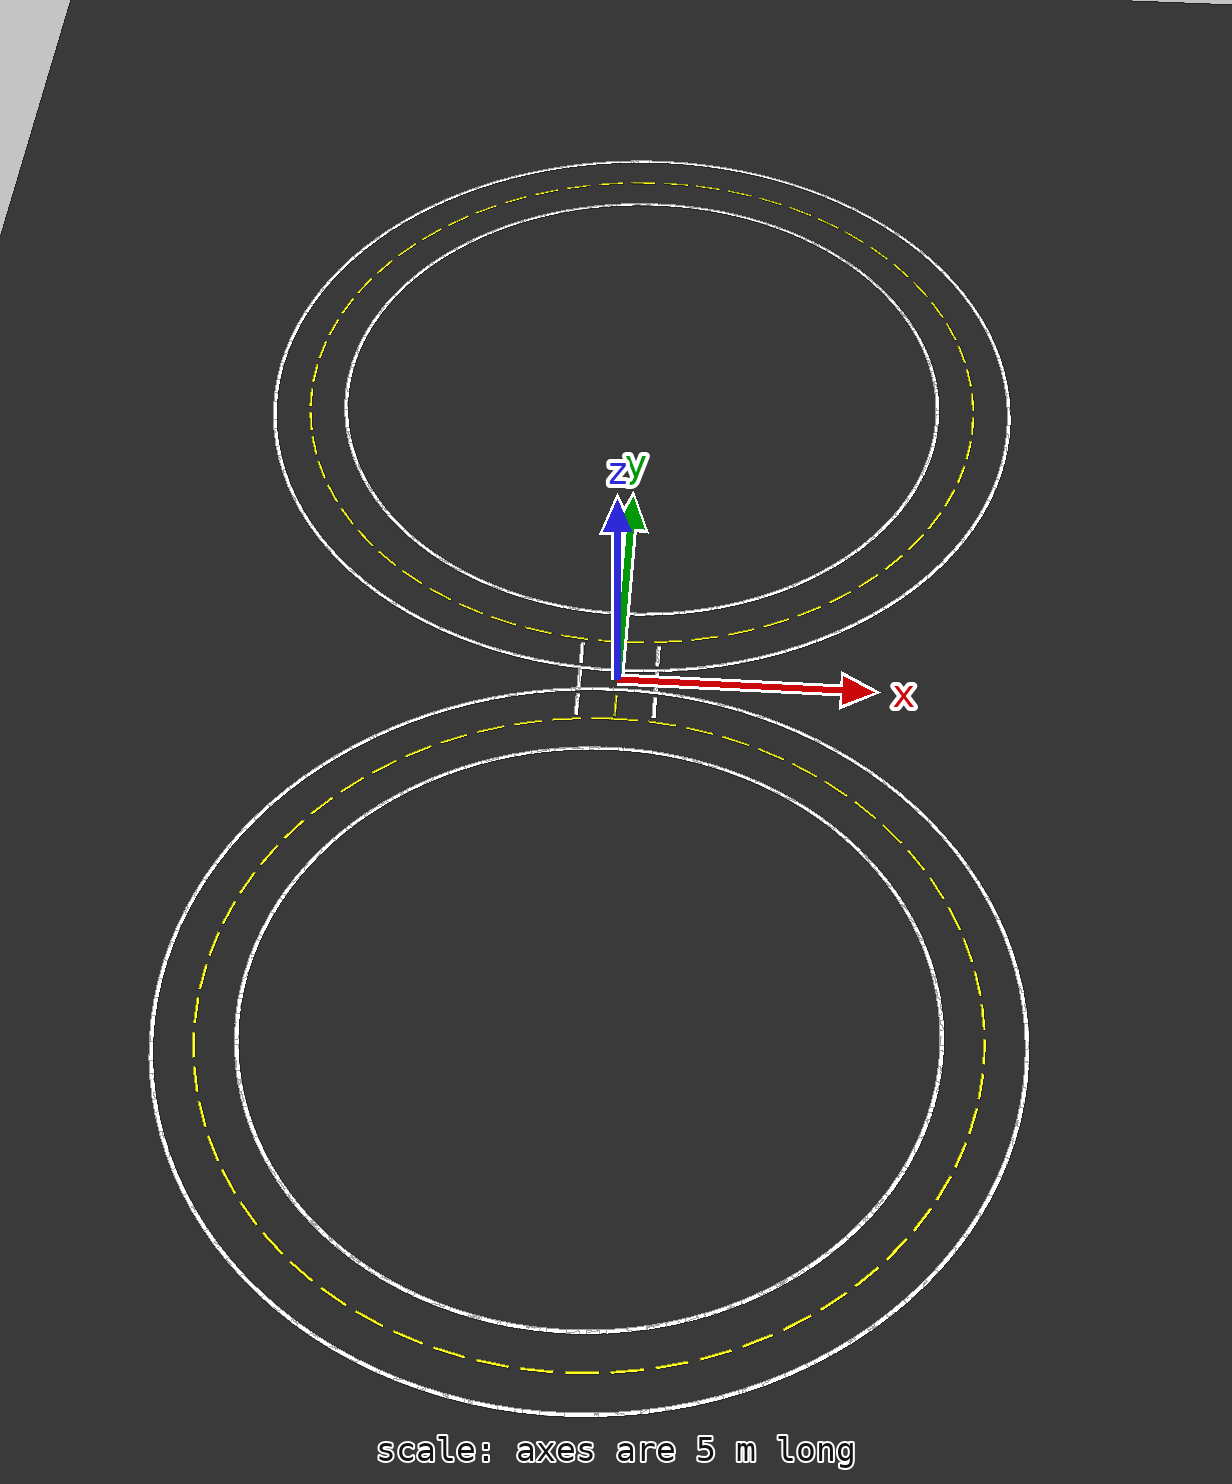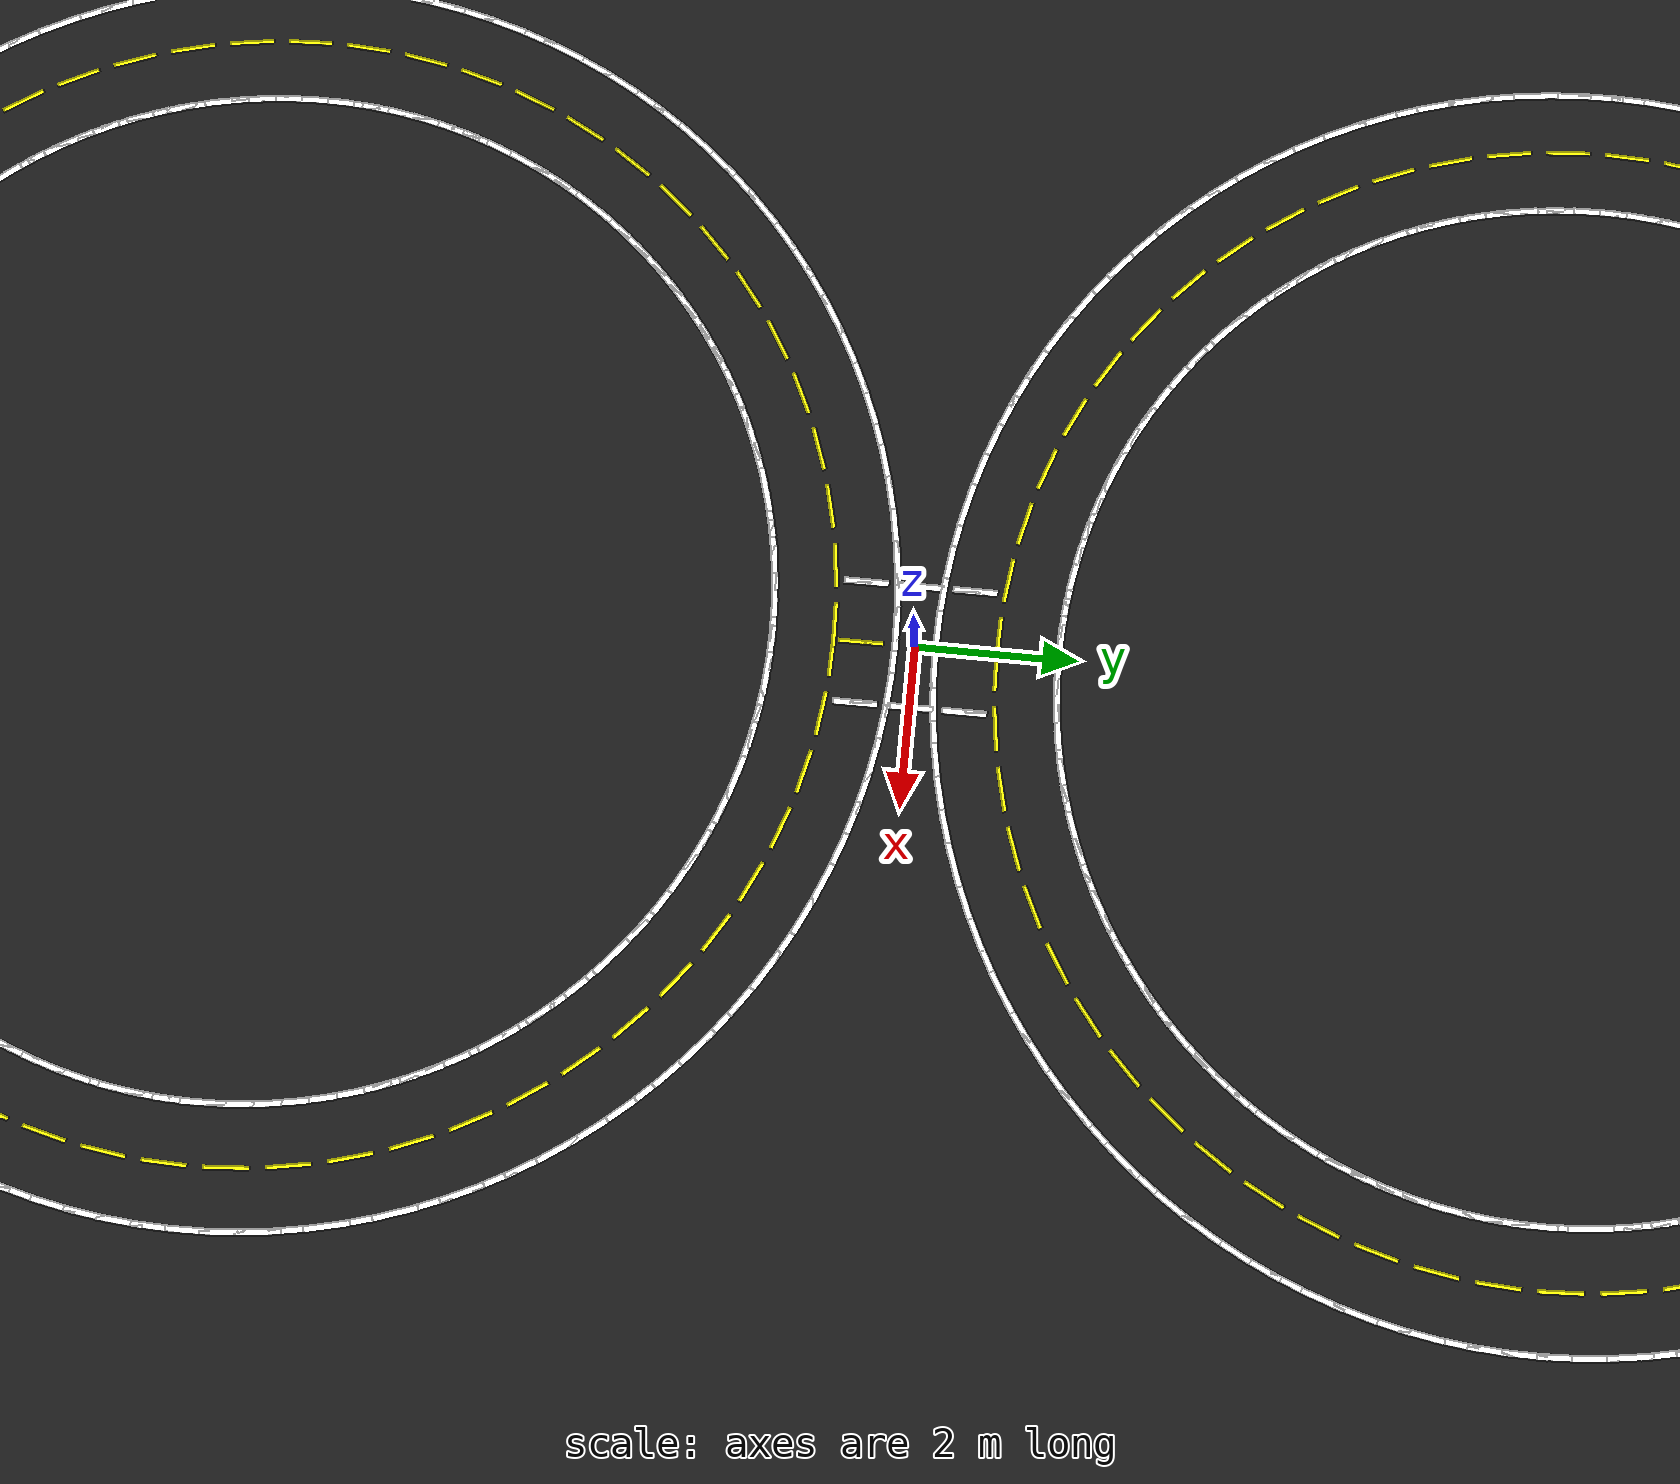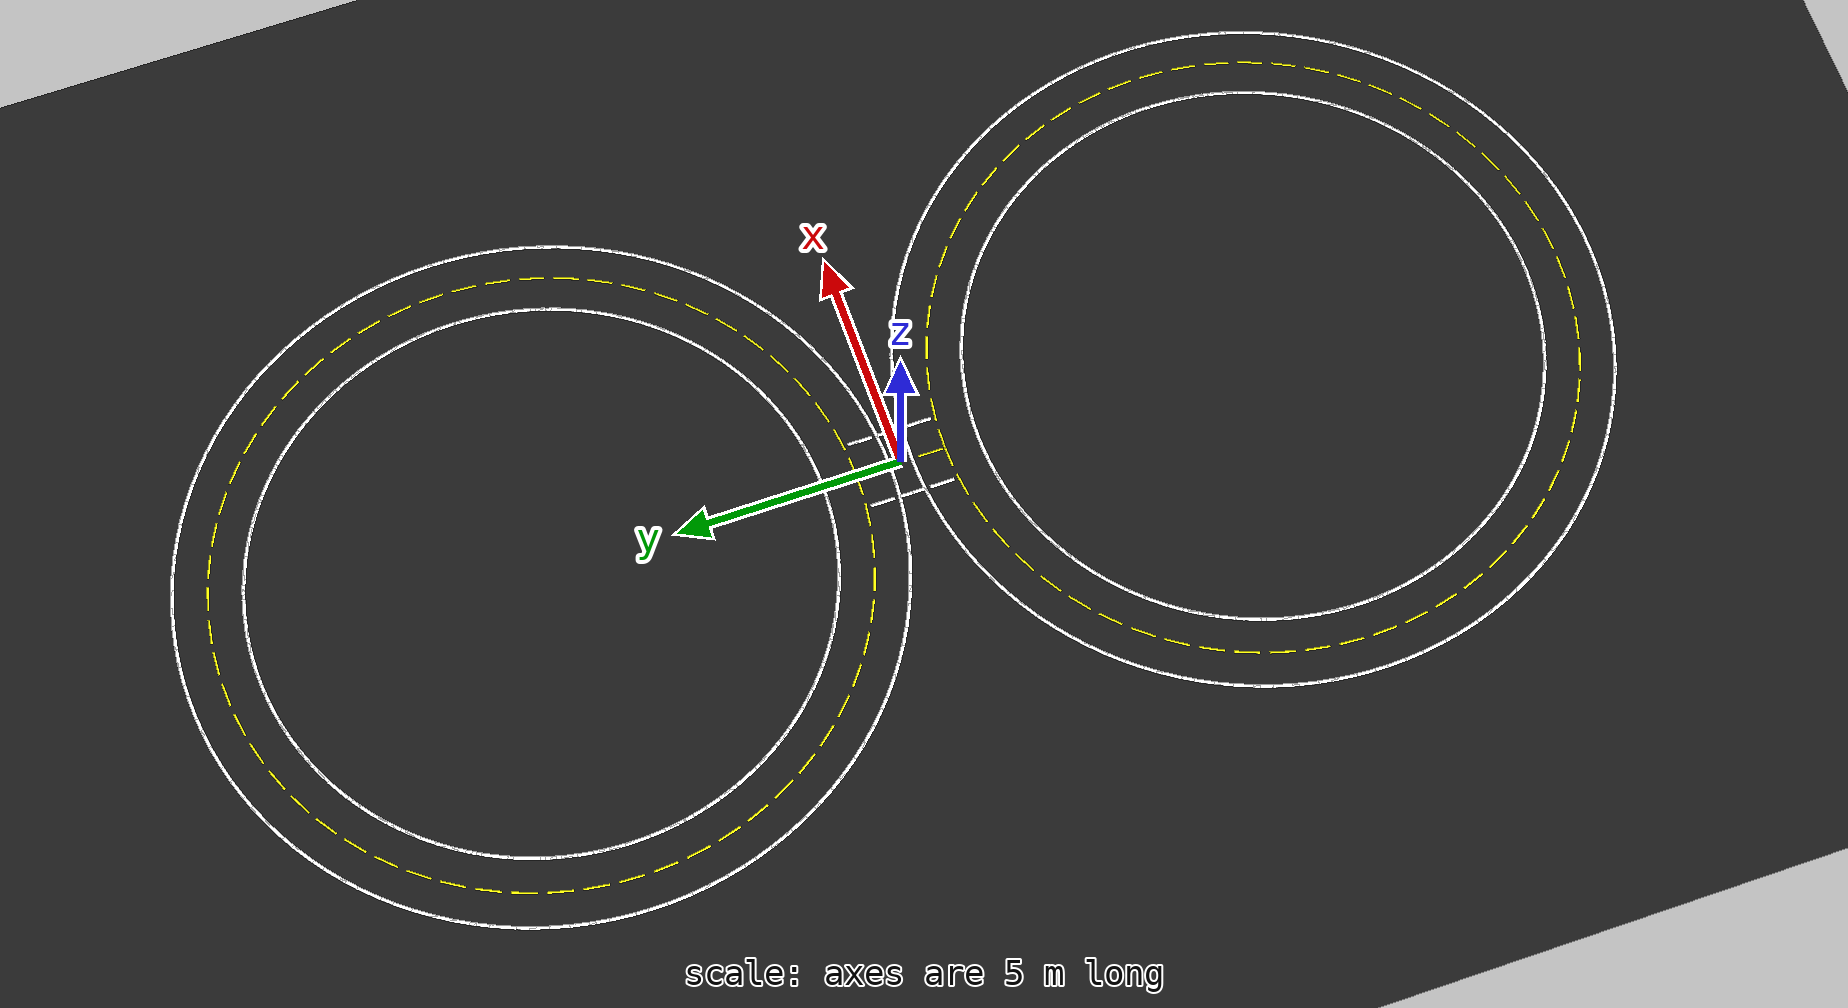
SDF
<?xml version="1.0"?>
<sdf version="1.6">
  <world name="lane_world">

    <plugin filename="ignition-gazebo-physics-system"
            name="ignition::gazebo::systems::Physics"/>
    <plugin filename="libignition-gazebo-sensors-system.so"
            name="ignition::gazebo::systems::Sensors">
      <render_engine>ogre2</render_engine>
    </plugin>
    <plugin filename="ignition-gazebo-scene-broadcaster-system"
            name="ignition::gazebo::systems::SceneBroadcaster"/>
    <plugin filename="ignition-gazebo-user-commands-system"
            name="ignition::gazebo::systems::UserCommands"/>

    <light type="directional" name="sun">
      <cast_shadows>true</cast_shadows>
      <pose>0 0 25 0 0 0</pose>
      <diffuse>0.85 0.85 0.85 1</diffuse>
      <specular>0.2 0.2 0.2 1</specular>
      <attenuation>
        <range>1000</range><constant>0.9</constant>
        <linear>0.01</linear><quadratic>0.001</quadratic>
      </attenuation>
      <direction>-0.5 0.1 -0.9</direction>
    </light>

    <!-- Dark asphalt ground -->
    <model name="ground">
      <static>true</static>
      <link name="link">
        <visual name="v">
          <geometry><plane><normal>0 0 1</normal><size>80 80</size></plane></geometry>
          <material>
            <ambient>0.10 0.10 0.10 1</ambient>
            <diffuse>0.10 0.10 0.10 1</diffuse>
          </material>
        </visual>
        <collision name="c">
          <geometry><plane><normal>0 0 1</normal><size>80 80</size></plane></geometry>
        </collision>
      </link>
    </model>

    <model name="seg_0000"><static>true</static>
      <pose>0.2046 0.2527 0.002 0 0 -3.1152</pose>
      <link name="link"><visual name="v">
        <geometry><box><size>0.550 0.080 0.0020</size></box></geometry>
        <material><ambient>1 1 1 1</ambient><diffuse>1 1 1 1</diffuse></material>
      </visual></link></model>

    <model name="seg_0001"><static>true</static>
      <pose>0.1650 1.7522 0.002 0 0 -3.1152</pose>
      <link name="link"><visual name="v">
        <geometry><box><size>0.550 0.080 0.0020</size></box></geometry>
        <material><ambient>1 1 1 1</ambient><diffuse>1 1 1 1</diffuse></material>
      </visual></link></model>

    <model name="seg_0002"><static>true</static>
      <pose>0.1848 1.0024 0.002 0 0 -3.1152</pose>
      <link name="link"><visual name="v">
        <geometry><box><size>0.550 0.05 0.0020</size></box></geometry>
        <material><ambient>1 1 0 1</ambient><diffuse>1 1 0 1</diffuse></material>
      </visual></link></model>

    <model name="seg_0003"><static>true</static>
      <pose>0.6132 0.2743 0.002 0 0 -3.0624</pose>
      <link name="link"><visual name="v">
        <geometry><box><size>0.550 0.080 0.0020</size></box></geometry>
        <material><ambient>1 1 1 1</ambient><diffuse>1 1 1 1</diffuse></material>
      </visual></link></model>

    <model name="seg_0004"><static>true</static>
      <pose>0.4945 1.7696 0.002 0 0 -3.0624</pose>
      <link name="link"><visual name="v">
        <geometry><box><size>0.550 0.080 0.0020</size></box></geometry>
        <material><ambient>1 1 1 1</ambient><diffuse>1 1 1 1</diffuse></material>
      </visual></link></model>

    <model name="seg_0005"><static>true</static>
      <pose>1.0200 0.3174 0.002 0 0 -3.0096</pose>
      <link name="link"><visual name="v">
        <geometry><box><size>0.550 0.080 0.0020</size></box></geometry>
        <material><ambient>1 1 1 1</ambient><diffuse>1 1 1 1</diffuse></material>
      </visual></link></model>

    <model name="seg_0006"><static>true</static>
      <pose>0.8226 1.8044 0.002 0 0 -3.0096</pose>
      <link name="link"><visual name="v">
        <geometry><box><size>0.550 0.080 0.0020</size></box></geometry>
        <material><ambient>1 1 1 1</ambient><diffuse>1 1 1 1</diffuse></material>
      </visual></link></model>

    <model name="seg_0007"><static>true</static>
      <pose>0.9213 1.0609 0.002 0 0 -3.0096</pose>
      <link name="link"><visual name="v">
        <geometry><box><size>0.550 0.05 0.0020</size></box></geometry>
        <material><ambient>1 1 0 1</ambient><diffuse>1 1 0 1</diffuse></material>
      </visual></link></model>

    <model name="seg_0008"><static>true</static>
      <pose>1.4241 0.3820 0.002 0 0 -2.9568</pose>
      <link name="link"><visual name="v">
        <geometry><box><size>0.550 0.080 0.0020</size></box></geometry>
        <material><ambient>1 1 1 1</ambient><diffuse>1 1 1 1</diffuse></material>
      </visual></link></model>

    <model name="seg_0009"><static>true</static>
      <pose>1.1484 1.8564 0.002 0 0 -2.9568</pose>
      <link name="link"><visual name="v">
        <geometry><box><size>0.550 0.080 0.0020</size></box></geometry>
        <material><ambient>1 1 1 1</ambient><diffuse>1 1 1 1</diffuse></material>
      </visual></link></model>

    <model name="seg_0010"><static>true</static>
      <pose>1.8241 0.4677 0.002 0 0 -2.9040</pose>
      <link name="link"><visual name="v">
        <geometry><box><size>0.550 0.080 0.0020</size></box></geometry>
        <material><ambient>1 1 1 1</ambient><diffuse>1 1 1 1</diffuse></material>
      </visual></link></model>

    <model name="seg_0011"><static>true</static>
      <pose>1.4711 1.9256 0.002 0 0 -2.9040</pose>
      <link name="link"><visual name="v">
        <geometry><box><size>0.550 0.080 0.0020</size></box></geometry>
        <material><ambient>1 1 1 1</ambient><diffuse>1 1 1 1</diffuse></material>
      </visual></link></model>

    <model name="seg_0012"><static>true</static>
      <pose>1.6476 1.1967 0.002 0 0 -2.9040</pose>
      <link name="link"><visual name="v">
        <geometry><box><size>0.550 0.05 0.0020</size></box></geometry>
        <material><ambient>1 1 0 1</ambient><diffuse>1 1 0 1</diffuse></material>
      </visual></link></model>

    <model name="seg_0013"><static>true</static>
      <pose>2.2191 0.5745 0.002 0 0 -2.8512</pose>
      <link name="link"><visual name="v">
        <geometry><box><size>0.550 0.080 0.0020</size></box></geometry>
        <material><ambient>1 1 1 1</ambient><diffuse>1 1 1 1</diffuse></material>
      </visual></link></model>

    <model name="seg_0014"><static>true</static>
      <pose>1.7896 2.0117 0.002 0 0 -2.8512</pose>
      <link name="link"><visual name="v">
        <geometry><box><size>0.550 0.080 0.0020</size></box></geometry>
        <material><ambient>1 1 1 1</ambient><diffuse>1 1 1 1</diffuse></material>
      </visual></link></model>

    <model name="seg_0015"><static>true</static>
      <pose>2.6079 0.7020 0.002 0 0 -2.7984</pose>
      <link name="link"><visual name="v">
        <geometry><box><size>0.550 0.080 0.0020</size></box></geometry>
        <material><ambient>1 1 1 1</ambient><diffuse>1 1 1 1</diffuse></material>
      </visual></link></model>

    <model name="seg_0016"><static>true</static>
      <pose>2.1031 2.1145 0.002 0 0 -2.7984</pose>
      <link name="link"><visual name="v">
        <geometry><box><size>0.550 0.080 0.0020</size></box></geometry>
        <material><ambient>1 1 1 1</ambient><diffuse>1 1 1 1</diffuse></material>
      </visual></link></model>

    <model name="seg_0017"><static>true</static>
      <pose>2.3555 1.4082 0.002 0 0 -2.7984</pose>
      <link name="link"><visual name="v">
        <geometry><box><size>0.550 0.05 0.0020</size></box></geometry>
        <material><ambient>1 1 0 1</ambient><diffuse>1 1 0 1</diffuse></material>
      </visual></link></model>

    <model name="seg_0018"><static>true</static>
      <pose>2.9894 0.8498 0.002 0 0 -2.7456</pose>
      <link name="link"><visual name="v">
        <geometry><box><size>0.550 0.080 0.0020</size></box></geometry>
        <material><ambient>1 1 1 1</ambient><diffuse>1 1 1 1</diffuse></material>
      </visual></link></model>

    <model name="seg_0019"><static>true</static>
      <pose>2.4108 2.2337 0.002 0 0 -2.7456</pose>
      <link name="link"><visual name="v">
        <geometry><box><size>0.550 0.080 0.0020</size></box></geometry>
        <material><ambient>1 1 1 1</ambient><diffuse>1 1 1 1</diffuse></material>
      </visual></link></model>

    <model name="seg_0020"><static>true</static>
      <pose>3.3626 1.0175 0.002 0 0 -2.6928</pose>
      <link name="link"><visual name="v">
        <geometry><box><size>0.550 0.080 0.0020</size></box></geometry>
        <material><ambient>1 1 1 1</ambient><diffuse>1 1 1 1</diffuse></material>
      </visual></link></model>

    <model name="seg_0021"><static>true</static>
      <pose>2.7118 2.3689 0.002 0 0 -2.6928</pose>
      <link name="link"><visual name="v">
        <geometry><box><size>0.550 0.080 0.0020</size></box></geometry>
        <material><ambient>1 1 1 1</ambient><diffuse>1 1 1 1</diffuse></material>
      </visual></link></model>

    <model name="seg_0022"><static>true</static>
      <pose>3.0372 1.6932 0.002 0 0 -2.6928</pose>
      <link name="link"><visual name="v">
        <geometry><box><size>0.550 0.05 0.0020</size></box></geometry>
        <material><ambient>1 1 0 1</ambient><diffuse>1 1 0 1</diffuse></material>
      </visual></link></model>

    <model name="seg_0023"><static>true</static>
      <pose>3.7264 1.2047 0.002 0 0 -2.6400</pose>
      <link name="link"><visual name="v">
        <geometry><box><size>0.550 0.080 0.0020</size></box></geometry>
        <material><ambient>1 1 1 1</ambient><diffuse>1 1 1 1</diffuse></material>
      </visual></link></model>

    <model name="seg_0024"><static>true</static>
      <pose>3.0052 2.5199 0.002 0 0 -2.6400</pose>
      <link name="link"><visual name="v">
        <geometry><box><size>0.550 0.080 0.0020</size></box></geometry>
        <material><ambient>1 1 1 1</ambient><diffuse>1 1 1 1</diffuse></material>
      </visual></link></model>

    <model name="seg_0025"><static>true</static>
      <pose>4.0798 1.4108 0.002 0 0 -2.5872</pose>
      <link name="link"><visual name="v">
        <geometry><box><size>0.550 0.080 0.0020</size></box></geometry>
        <material><ambient>1 1 1 1</ambient><diffuse>1 1 1 1</diffuse></material>
      </visual></link></model>

    <model name="seg_0026"><static>true</static>
      <pose>3.2902 2.6861 0.002 0 0 -2.5872</pose>
      <link name="link"><visual name="v">
        <geometry><box><size>0.550 0.080 0.0020</size></box></geometry>
        <material><ambient>1 1 1 1</ambient><diffuse>1 1 1 1</diffuse></material>
      </visual></link></model>

    <model name="seg_0027"><static>true</static>
      <pose>3.6850 2.0485 0.002 0 0 -2.5872</pose>
      <link name="link"><visual name="v">
        <geometry><box><size>0.550 0.05 0.0020</size></box></geometry>
        <material><ambient>1 1 0 1</ambient><diffuse>1 1 0 1</diffuse></material>
      </visual></link></model>

    <model name="seg_0028"><static>true</static>
      <pose>4.4219 1.6353 0.002 0 0 -2.5344</pose>
      <link name="link"><visual name="v">
        <geometry><box><size>0.550 0.080 0.0020</size></box></geometry>
        <material><ambient>1 1 1 1</ambient><diffuse>1 1 1 1</diffuse></material>
      </visual></link></model>

    <model name="seg_0029"><static>true</static>
      <pose>3.5661 2.8672 0.002 0 0 -2.5344</pose>
      <link name="link"><visual name="v">
        <geometry><box><size>0.550 0.080 0.0020</size></box></geometry>
        <material><ambient>1 1 1 1</ambient><diffuse>1 1 1 1</diffuse></material>
      </visual></link></model>

    <model name="seg_0030"><static>true</static>
      <pose>4.7516 1.8776 0.002 0 0 -2.4816</pose>
      <link name="link"><visual name="v">
        <geometry><box><size>0.550 0.080 0.0020</size></box></geometry>
        <material><ambient>1 1 1 1</ambient><diffuse>1 1 1 1</diffuse></material>
      </visual></link></model>

    <model name="seg_0031"><static>true</static>
      <pose>3.8320 3.0625 0.002 0 0 -2.4816</pose>
      <link name="link"><visual name="v">
        <geometry><box><size>0.550 0.080 0.0020</size></box></geometry>
        <material><ambient>1 1 1 1</ambient><diffuse>1 1 1 1</diffuse></material>
      </visual></link></model>

    <model name="seg_0032"><static>true</static>
      <pose>4.2918 2.4700 0.002 0 0 -2.4816</pose>
      <link name="link"><visual name="v">
        <geometry><box><size>0.550 0.05 0.0020</size></box></geometry>
        <material><ambient>1 1 0 1</ambient><diffuse>1 1 0 1</diffuse></material>
      </visual></link></model>

    <model name="seg_0033"><static>true</static>
      <pose>5.0681 2.1369 0.002 0 0 -2.4288</pose>
      <link name="link"><visual name="v">
        <geometry><box><size>0.550 0.080 0.0020</size></box></geometry>
        <material><ambient>1 1 1 1</ambient><diffuse>1 1 1 1</diffuse></material>
      </visual></link></model>

    <model name="seg_0034"><static>true</static>
      <pose>4.0872 3.2717 0.002 0 0 -2.4288</pose>
      <link name="link"><visual name="v">
        <geometry><box><size>0.550 0.080 0.0020</size></box></geometry>
        <material><ambient>1 1 1 1</ambient><diffuse>1 1 1 1</diffuse></material>
      </visual></link></model>

    <model name="seg_0035"><static>true</static>
      <pose>5.3705 2.4125 0.002 0 0 -2.3760</pose>
      <link name="link"><visual name="v">
        <geometry><box><size>0.550 0.080 0.0020</size></box></geometry>
        <material><ambient>1 1 1 1</ambient><diffuse>1 1 1 1</diffuse></material>
      </visual></link></model>

    <model name="seg_0036"><static>true</static>
      <pose>4.3311 3.4940 0.002 0 0 -2.3760</pose>
      <link name="link"><visual name="v">
        <geometry><box><size>0.550 0.080 0.0020</size></box></geometry>
        <material><ambient>1 1 1 1</ambient><diffuse>1 1 1 1</diffuse></material>
      </visual></link></model>

    <model name="seg_0037"><static>true</static>
      <pose>4.8508 2.9532 0.002 0 0 -2.3760</pose>
      <link name="link"><visual name="v">
        <geometry><box><size>0.550 0.05 0.0020</size></box></geometry>
        <material><ambient>1 1 0 1</ambient><diffuse>1 1 0 1</diffuse></material>
      </visual></link></model>

    <model name="seg_0038"><static>true</static>
      <pose>5.6579 2.7037 0.002 0 0 -2.3232</pose>
      <link name="link"><visual name="v">
        <geometry><box><size>0.550 0.080 0.0020</size></box></geometry>
        <material><ambient>1 1 1 1</ambient><diffuse>1 1 1 1</diffuse></material>
      </visual></link></model>

    <model name="seg_0039"><static>true</static>
      <pose>4.5628 3.7288 0.002 0 0 -2.3232</pose>
      <link name="link"><visual name="v">
        <geometry><box><size>0.550 0.080 0.0020</size></box></geometry>
        <material><ambient>1 1 1 1</ambient><diffuse>1 1 1 1</diffuse></material>
      </visual></link></model>

    <model name="seg_0040"><static>true</static>
      <pose>5.9295 3.0097 0.002 0 0 -2.2704</pose>
      <link name="link"><visual name="v">
        <geometry><box><size>0.550 0.080 0.0020</size></box></geometry>
        <material><ambient>1 1 1 1</ambient><diffuse>1 1 1 1</diffuse></material>
      </visual></link></model>

    <model name="seg_0041"><static>true</static>
      <pose>4.7819 3.9756 0.002 0 0 -2.2704</pose>
      <link name="link"><visual name="v">
        <geometry><box><size>0.550 0.080 0.0020</size></box></geometry>
        <material><ambient>1 1 1 1</ambient><diffuse>1 1 1 1</diffuse></material>
      </visual></link></model>

    <model name="seg_0042"><static>true</static>
      <pose>5.3557 3.4926 0.002 0 0 -2.2704</pose>
      <link name="link"><visual name="v">
        <geometry><box><size>0.550 0.05 0.0020</size></box></geometry>
        <material><ambient>1 1 0 1</ambient><diffuse>1 1 0 1</diffuse></material>
      </visual></link></model>

    <model name="seg_0043"><static>true</static>
      <pose>6.1846 3.3296 0.002 0 0 -2.2176</pose>
      <link name="link"><visual name="v">
        <geometry><box><size>0.550 0.080 0.0020</size></box></geometry>
        <material><ambient>1 1 1 1</ambient><diffuse>1 1 1 1</diffuse></material>
      </visual></link></model>

    <model name="seg_0044"><static>true</static>
      <pose>4.9876 4.2335 0.002 0 0 -2.2176</pose>
      <link name="link"><visual name="v">
        <geometry><box><size>0.550 0.080 0.0020</size></box></geometry>
        <material><ambient>1 1 1 1</ambient><diffuse>1 1 1 1</diffuse></material>
      </visual></link></model>

    <model name="seg_0045"><static>true</static>
      <pose>6.4225 3.6625 0.002 0 0 -2.1648</pose>
      <link name="link"><visual name="v">
        <geometry><box><size>0.550 0.080 0.0020</size></box></geometry>
        <material><ambient>1 1 1 1</ambient><diffuse>1 1 1 1</diffuse></material>
      </visual></link></model>

    <model name="seg_0046"><static>true</static>
      <pose>5.1794 4.5020 0.002 0 0 -2.1648</pose>
      <link name="link"><visual name="v">
        <geometry><box><size>0.550 0.080 0.0020</size></box></geometry>
        <material><ambient>1 1 1 1</ambient><diffuse>1 1 1 1</diffuse></material>
      </visual></link></model>

    <model name="seg_0047"><static>true</static>
      <pose>5.8010 4.0822 0.002 0 0 -2.1648</pose>
      <link name="link"><visual name="v">
        <geometry><box><size>0.550 0.05 0.0020</size></box></geometry>
        <material><ambient>1 1 0 1</ambient><diffuse>1 1 0 1</diffuse></material>
      </visual></link></model>

    <model name="seg_0048"><static>true</static>
      <pose>6.6425 4.0075 0.002 0 0 -2.1120</pose>
      <link name="link"><visual name="v">
        <geometry><box><size>0.550 0.080 0.0020</size></box></geometry>
        <material><ambient>1 1 1 1</ambient><diffuse>1 1 1 1</diffuse></material>
      </visual></link></model>

    <model name="seg_0049"><static>true</static>
      <pose>5.3568 4.7802 0.002 0 0 -2.1120</pose>
      <link name="link"><visual name="v">
        <geometry><box><size>0.550 0.080 0.0020</size></box></geometry>
        <material><ambient>1 1 1 1</ambient><diffuse>1 1 1 1</diffuse></material>
      </visual></link></model>

    <model name="seg_0050"><static>true</static>
      <pose>6.8439 4.3636 0.002 0 0 -2.0592</pose>
      <link name="link"><visual name="v">
        <geometry><box><size>0.550 0.080 0.0020</size></box></geometry>
        <material><ambient>1 1 1 1</ambient><diffuse>1 1 1 1</diffuse></material>
      </visual></link></model>

    <model name="seg_0051"><static>true</static>
      <pose>5.5193 5.0674 0.002 0 0 -2.0592</pose>
      <link name="link"><visual name="v">
        <geometry><box><size>0.550 0.080 0.0020</size></box></geometry>
        <material><ambient>1 1 1 1</ambient><diffuse>1 1 1 1</diffuse></material>
      </visual></link></model>

    <model name="seg_0052"><static>true</static>
      <pose>6.1816 4.7155 0.002 0 0 -2.0592</pose>
      <link name="link"><visual name="v">
        <geometry><box><size>0.550 0.05 0.0020</size></box></geometry>
        <material><ambient>1 1 0 1</ambient><diffuse>1 1 0 1</diffuse></material>
      </visual></link></model>

    <model name="seg_0053"><static>true</static>
      <pose>7.0263 4.7299 0.002 0 0 -2.0064</pose>
      <link name="link"><visual name="v">
        <geometry><box><size>0.550 0.080 0.0020</size></box></geometry>
        <material><ambient>1 1 1 1</ambient><diffuse>1 1 1 1</diffuse></material>
      </visual></link></model>

    <model name="seg_0054"><static>true</static>
      <pose>5.6664 5.3628 0.002 0 0 -2.0064</pose>
      <link name="link"><visual name="v">
        <geometry><box><size>0.550 0.080 0.0020</size></box></geometry>
        <material><ambient>1 1 1 1</ambient><diffuse>1 1 1 1</diffuse></material>
      </visual></link></model>

    <model name="seg_0055"><static>true</static>
      <pose>7.1891 5.1052 0.002 0 0 -1.9536</pose>
      <link name="link"><visual name="v">
        <geometry><box><size>0.550 0.080 0.0020</size></box></geometry>
        <material><ambient>1 1 1 1</ambient><diffuse>1 1 1 1</diffuse></material>
      </visual></link></model>

    <model name="seg_0056"><static>true</static>
      <pose>5.7976 5.6655 0.002 0 0 -1.9536</pose>
      <link name="link"><visual name="v">
        <geometry><box><size>0.550 0.080 0.0020</size></box></geometry>
        <material><ambient>1 1 1 1</ambient><diffuse>1 1 1 1</diffuse></material>
      </visual></link></model>

    <model name="seg_0057"><static>true</static>
      <pose>6.4934 5.3854 0.002 0 0 -1.9536</pose>
      <link name="link"><visual name="v">
        <geometry><box><size>0.550 0.05 0.0020</size></box></geometry>
        <material><ambient>1 1 0 1</ambient><diffuse>1 1 0 1</diffuse></material>
      </visual></link></model>

    <model name="seg_0058"><static>true</static>
      <pose>7.3318 5.4887 0.002 0 0 -1.9008</pose>
      <link name="link"><visual name="v">
        <geometry><box><size>0.550 0.080 0.0020</size></box></geometry>
        <material><ambient>1 1 1 1</ambient><diffuse>1 1 1 1</diffuse></material>
      </visual></link></model>

    <model name="seg_0059"><static>true</static>
      <pose>5.9128 5.9747 0.002 0 0 -1.9008</pose>
      <link name="link"><visual name="v">
        <geometry><box><size>0.550 0.080 0.0020</size></box></geometry>
        <material><ambient>1 1 1 1</ambient><diffuse>1 1 1 1</diffuse></material>
      </visual></link></model>

    <model name="seg_0060"><static>true</static>
      <pose>7.4541 5.8791 0.002 0 0 -1.8480</pose>
      <link name="link"><visual name="v">
        <geometry><box><size>0.550 0.080 0.0020</size></box></geometry>
        <material><ambient>1 1 1 1</ambient><diffuse>1 1 1 1</diffuse></material>
      </visual></link></model>

    <model name="seg_0061"><static>true</static>
      <pose>6.0114 6.2896 0.002 0 0 -1.8480</pose>
      <link name="link"><visual name="v">
        <geometry><box><size>0.550 0.080 0.0020</size></box></geometry>
        <material><ambient>1 1 1 1</ambient><diffuse>1 1 1 1</diffuse></material>
      </visual></link></model>

    <model name="seg_0062"><static>true</static>
      <pose>6.7328 6.0844 0.002 0 0 -1.8480</pose>
      <link name="link"><visual name="v">
        <geometry><box><size>0.550 0.05 0.0020</size></box></geometry>
        <material><ambient>1 1 0 1</ambient><diffuse>1 1 0 1</diffuse></material>
      </visual></link></model>

    <model name="seg_0063"><static>true</static>
      <pose>7.5557 6.2755 0.002 0 0 -1.7952</pose>
      <link name="link"><visual name="v">
        <geometry><box><size>0.550 0.080 0.0020</size></box></geometry>
        <material><ambient>1 1 1 1</ambient><diffuse>1 1 1 1</diffuse></material>
      </visual></link></model>

    <model name="seg_0064"><static>true</static>
      <pose>6.0933 6.6092 0.002 0 0 -1.7952</pose>
      <link name="link"><visual name="v">
        <geometry><box><size>0.550 0.080 0.0020</size></box></geometry>
        <material><ambient>1 1 1 1</ambient><diffuse>1 1 1 1</diffuse></material>
      </visual></link></model>

    <model name="seg_0065"><static>true</static>
      <pose>7.6362 6.6766 0.002 0 0 -1.7424</pose>
      <link name="link"><visual name="v">
        <geometry><box><size>0.550 0.080 0.0020</size></box></geometry>
        <material><ambient>1 1 1 1</ambient><diffuse>1 1 1 1</diffuse></material>
      </visual></link></model>

    <model name="seg_0066"><static>true</static>
      <pose>6.1582 6.9328 0.002 0 0 -1.7424</pose>
      <link name="link"><visual name="v">
        <geometry><box><size>0.550 0.080 0.0020</size></box></geometry>
        <material><ambient>1 1 1 1</ambient><diffuse>1 1 1 1</diffuse></material>
      </visual></link></model>

    <model name="seg_0067"><static>true</static>
      <pose>6.8972 6.8047 0.002 0 0 -1.7424</pose>
      <link name="link"><visual name="v">
        <geometry><box><size>0.550 0.05 0.0020</size></box></geometry>
        <material><ambient>1 1 0 1</ambient><diffuse>1 1 0 1</diffuse></material>
      </visual></link></model>

    <model name="seg_0068"><static>true</static>
      <pose>7.6954 7.0815 0.002 0 0 -1.6896</pose>
      <link name="link"><visual name="v">
        <geometry><box><size>0.550 0.080 0.0020</size></box></geometry>
        <material><ambient>1 1 1 1</ambient><diffuse>1 1 1 1</diffuse></material>
      </visual></link></model>

    <model name="seg_0069"><static>true</static>
      <pose>6.2059 7.2592 0.002 0 0 -1.6896</pose>
      <link name="link"><visual name="v">
        <geometry><box><size>0.550 0.080 0.0020</size></box></geometry>
        <material><ambient>1 1 1 1</ambient><diffuse>1 1 1 1</diffuse></material>
      </visual></link></model>

    <model name="seg_0070"><static>true</static>
      <pose>7.7331 7.4889 0.002 0 0 -1.6368</pose>
      <link name="link"><visual name="v">
        <geometry><box><size>0.550 0.080 0.0020</size></box></geometry>
        <material><ambient>1 1 1 1</ambient><diffuse>1 1 1 1</diffuse></material>
      </visual></link></model>

    <model name="seg_0071"><static>true</static>
      <pose>6.2364 7.5878 0.002 0 0 -1.6368</pose>
      <link name="link"><visual name="v">
        <geometry><box><size>0.550 0.080 0.0020</size></box></geometry>
        <material><ambient>1 1 1 1</ambient><diffuse>1 1 1 1</diffuse></material>
      </visual></link></model>

    <model name="seg_0072"><static>true</static>
      <pose>6.9848 7.5383 0.002 0 0 -1.6368</pose>
      <link name="link"><visual name="v">
        <geometry><box><size>0.550 0.05 0.0020</size></box></geometry>
        <material><ambient>1 1 0 1</ambient><diffuse>1 1 0 1</diffuse></material>
      </visual></link></model>

    <model name="seg_0073"><static>true</static>
      <pose>7.7493 7.8977 0.002 0 0 -1.5840</pose>
      <link name="link"><visual name="v">
        <geometry><box><size>0.550 0.080 0.0020</size></box></geometry>
        <material><ambient>1 1 1 1</ambient><diffuse>1 1 1 1</diffuse></material>
      </visual></link></model>

    <model name="seg_0074"><static>true</static>
      <pose>6.2495 7.9175 0.002 0 0 -1.5840</pose>
      <link name="link"><visual name="v">
        <geometry><box><size>0.550 0.080 0.0020</size></box></geometry>
        <material><ambient>1 1 1 1</ambient><diffuse>1 1 1 1</diffuse></material>
      </visual></link></model>

    <model name="seg_0075"><static>true</static>
      <pose>7.7439 8.3068 0.002 0 0 -1.5312</pose>
      <link name="link"><visual name="v">
        <geometry><box><size>0.550 0.080 0.0020</size></box></geometry>
        <material><ambient>1 1 1 1</ambient><diffuse>1 1 1 1</diffuse></material>
      </visual></link></model>

    <model name="seg_0076"><static>true</static>
      <pose>6.2451 8.2474 0.002 0 0 -1.5312</pose>
      <link name="link"><visual name="v">
        <geometry><box><size>0.550 0.080 0.0020</size></box></geometry>
        <material><ambient>1 1 1 1</ambient><diffuse>1 1 1 1</diffuse></material>
      </visual></link></model>

    <model name="seg_0077"><static>true</static>
      <pose>6.9945 8.2771 0.002 0 0 -1.5312</pose>
      <link name="link"><visual name="v">
        <geometry><box><size>0.550 0.05 0.0020</size></box></geometry>
        <material><ambient>1 1 0 1</ambient><diffuse>1 1 0 1</diffuse></material>
      </visual></link></model>

    <model name="seg_0078"><static>true</static>
      <pose>7.7169 8.7151 0.002 0 0 -1.4784</pose>
      <link name="link"><visual name="v">
        <geometry><box><size>0.550 0.080 0.0020</size></box></geometry>
        <material><ambient>1 1 1 1</ambient><diffuse>1 1 1 1</diffuse></material>
      </visual></link></model>

    <model name="seg_0079"><static>true</static>
      <pose>6.2233 8.5767 0.002 0 0 -1.4784</pose>
      <link name="link"><visual name="v">
        <geometry><box><size>0.550 0.080 0.0020</size></box></geometry>
        <material><ambient>1 1 1 1</ambient><diffuse>1 1 1 1</diffuse></material>
      </visual></link></model>

    <model name="seg_0080"><static>true</static>
      <pose>7.6684 9.1213 0.002 0 0 -1.4256</pose>
      <link name="link"><visual name="v">
        <geometry><box><size>0.550 0.080 0.0020</size></box></geometry>
        <material><ambient>1 1 1 1</ambient><diffuse>1 1 1 1</diffuse></material>
      </visual></link></model>

    <model name="seg_0081"><static>true</static>
      <pose>6.1842 8.9043 0.002 0 0 -1.4256</pose>
      <link name="link"><visual name="v">
        <geometry><box><size>0.550 0.080 0.0020</size></box></geometry>
        <material><ambient>1 1 1 1</ambient><diffuse>1 1 1 1</diffuse></material>
      </visual></link></model>

    <model name="seg_0082"><static>true</static>
      <pose>6.9263 9.0128 0.002 0 0 -1.4256</pose>
      <link name="link"><visual name="v">
        <geometry><box><size>0.550 0.05 0.0020</size></box></geometry>
        <material><ambient>1 1 0 1</ambient><diffuse>1 1 0 1</diffuse></material>
      </visual></link></model>

    <model name="seg_0083"><static>true</static>
      <pose>7.5986 9.5245 0.002 0 0 -1.3728</pose>
      <link name="link"><visual name="v">
        <geometry><box><size>0.550 0.080 0.0020</size></box></geometry>
        <material><ambient>1 1 1 1</ambient><diffuse>1 1 1 1</diffuse></material>
      </visual></link></model>

    <model name="seg_0084"><static>true</static>
      <pose>6.1279 9.2294 0.002 0 0 -1.3728</pose>
      <link name="link"><visual name="v">
        <geometry><box><size>0.550 0.080 0.0020</size></box></geometry>
        <material><ambient>1 1 1 1</ambient><diffuse>1 1 1 1</diffuse></material>
      </visual></link></model>

    <model name="seg_0085"><static>true</static>
      <pose>7.5075 9.9234 0.002 0 0 -1.3200</pose>
      <link name="link"><visual name="v">
        <geometry><box><size>0.550 0.080 0.0020</size></box></geometry>
        <material><ambient>1 1 1 1</ambient><diffuse>1 1 1 1</diffuse></material>
      </visual></link></model>

    <model name="seg_0086"><static>true</static>
      <pose>6.0545 9.5511 0.002 0 0 -1.3200</pose>
      <link name="link"><visual name="v">
        <geometry><box><size>0.550 0.080 0.0020</size></box></geometry>
        <material><ambient>1 1 1 1</ambient><diffuse>1 1 1 1</diffuse></material>
      </visual></link></model>

    <model name="seg_0087"><static>true</static>
      <pose>6.7810 9.7372 0.002 0 0 -1.3200</pose>
      <link name="link"><visual name="v">
        <geometry><box><size>0.550 0.05 0.0020</size></box></geometry>
        <material><ambient>1 1 0 1</ambient><diffuse>1 1 0 1</diffuse></material>
      </visual></link></model>

    <model name="seg_0088"><static>true</static>
      <pose>7.3956 10.3169 0.002 0 0 -1.2672</pose>
      <link name="link"><visual name="v">
        <geometry><box><size>0.550 0.080 0.0020</size></box></geometry>
        <material><ambient>1 1 1 1</ambient><diffuse>1 1 1 1</diffuse></material>
      </visual></link></model>

    <model name="seg_0089"><static>true</static>
      <pose>5.9642 9.8685 0.002 0 0 -1.2672</pose>
      <link name="link"><visual name="v">
        <geometry><box><size>0.550 0.080 0.0020</size></box></geometry>
        <material><ambient>1 1 1 1</ambient><diffuse>1 1 1 1</diffuse></material>
      </visual></link></model>

    <model name="seg_0090"><static>true</static>
      <pose>7.2630 10.7040 0.002 0 0 -1.2144</pose>
      <link name="link"><visual name="v">
        <geometry><box><size>0.550 0.080 0.0020</size></box></geometry>
        <material><ambient>1 1 1 1</ambient><diffuse>1 1 1 1</diffuse></material>
      </visual></link></model>

    <model name="seg_0091"><static>true</static>
      <pose>5.8572 10.1806 0.002 0 0 -1.2144</pose>
      <link name="link"><visual name="v">
        <geometry><box><size>0.550 0.080 0.0020</size></box></geometry>
        <material><ambient>1 1 1 1</ambient><diffuse>1 1 1 1</diffuse></material>
      </visual></link></model>

    <model name="seg_0092"><static>true</static>
      <pose>6.5601 10.4423 0.002 0 0 -1.2144</pose>
      <link name="link"><visual name="v">
        <geometry><box><size>0.550 0.05 0.0020</size></box></geometry>
        <material><ambient>1 1 0 1</ambient><diffuse>1 1 0 1</diffuse></material>
      </visual></link></model>

    <model name="seg_0093"><static>true</static>
      <pose>7.1102 11.0835 0.002 0 0 -1.1616</pose>
      <link name="link"><visual name="v">
        <geometry><box><size>0.550 0.080 0.0020</size></box></geometry>
        <material><ambient>1 1 1 1</ambient><diffuse>1 1 1 1</diffuse></material>
      </visual></link></model>

    <model name="seg_0094"><static>true</static>
      <pose>5.7340 10.4867 0.002 0 0 -1.1616</pose>
      <link name="link"><visual name="v">
        <geometry><box><size>0.550 0.080 0.0020</size></box></geometry>
        <material><ambient>1 1 1 1</ambient><diffuse>1 1 1 1</diffuse></material>
      </visual></link></model>

    <model name="seg_0095"><static>true</static>
      <pose>6.9375 11.4545 0.002 0 0 -1.1088</pose>
      <link name="link"><visual name="v">
        <geometry><box><size>0.550 0.080 0.0020</size></box></geometry>
        <material><ambient>1 1 1 1</ambient><diffuse>1 1 1 1</diffuse></material>
      </visual></link></model>

    <model name="seg_0096"><static>true</static>
      <pose>5.5948 10.7859 0.002 0 0 -1.1088</pose>
      <link name="link"><visual name="v">
        <geometry><box><size>0.550 0.080 0.0020</size></box></geometry>
        <material><ambient>1 1 1 1</ambient><diffuse>1 1 1 1</diffuse></material>
      </visual></link></model>

    <model name="seg_0097"><static>true</static>
      <pose>6.2661 11.1202 0.002 0 0 -1.1088</pose>
      <link name="link"><visual name="v">
        <geometry><box><size>0.550 0.05 0.0020</size></box></geometry>
        <material><ambient>1 1 0 1</ambient><diffuse>1 1 0 1</diffuse></material>
      </visual></link></model>

    <model name="seg_0098"><static>true</static>
      <pose>6.7455 11.8158 0.002 0 0 -1.0560</pose>
      <link name="link"><visual name="v">
        <geometry><box><size>0.550 0.080 0.0020</size></box></geometry>
        <material><ambient>1 1 1 1</ambient><diffuse>1 1 1 1</diffuse></material>
      </visual></link></model>

    <model name="seg_0099"><static>true</static>
      <pose>5.4399 11.0772 0.002 0 0 -1.0560</pose>
      <link name="link"><visual name="v">
        <geometry><box><size>0.550 0.080 0.0020</size></box></geometry>
        <material><ambient>1 1 1 1</ambient><diffuse>1 1 1 1</diffuse></material>
      </visual></link></model>

    <model name="seg_0100"><static>true</static>
      <pose>6.5348 12.1665 0.002 0 0 -1.0032</pose>
      <link name="link"><visual name="v">
        <geometry><box><size>0.550 0.080 0.0020</size></box></geometry>
        <material><ambient>1 1 1 1</ambient><diffuse>1 1 1 1</diffuse></material>
      </visual></link></model>

    <model name="seg_0101"><static>true</static>
      <pose>5.2700 11.3601 0.002 0 0 -1.0032</pose>
      <link name="link"><visual name="v">
        <geometry><box><size>0.550 0.080 0.0020</size></box></geometry>
        <material><ambient>1 1 1 1</ambient><diffuse>1 1 1 1</diffuse></material>
      </visual></link></model>

    <model name="seg_0102"><static>true</static>
      <pose>5.9024 11.7633 0.002 0 0 -1.0032</pose>
      <link name="link"><visual name="v">
        <geometry><box><size>0.550 0.05 0.0020</size></box></geometry>
        <material><ambient>1 1 0 1</ambient><diffuse>1 1 0 1</diffuse></material>
      </visual></link></model>

    <model name="seg_0103"><static>true</static>
      <pose>6.3058 12.5055 0.002 0 0 -0.9504</pose>
      <link name="link"><visual name="v">
        <geometry><box><size>0.550 0.080 0.0020</size></box></geometry>
        <material><ambient>1 1 1 1</ambient><diffuse>1 1 1 1</diffuse></material>
      </visual></link></model>

    <model name="seg_0104"><static>true</static>
      <pose>5.0853 11.6335 0.002 0 0 -0.9504</pose>
      <link name="link"><visual name="v">
        <geometry><box><size>0.550 0.080 0.0020</size></box></geometry>
        <material><ambient>1 1 1 1</ambient><diffuse>1 1 1 1</diffuse></material>
      </visual></link></model>

    <model name="seg_0105"><static>true</static>
      <pose>6.0592 12.8320 0.002 0 0 -0.8976</pose>
      <link name="link"><visual name="v">
        <geometry><box><size>0.550 0.080 0.0020</size></box></geometry>
        <material><ambient>1 1 1 1</ambient><diffuse>1 1 1 1</diffuse></material>
      </visual></link></model>

    <model name="seg_0106"><static>true</static>
      <pose>4.8864 11.8968 0.002 0 0 -0.8976</pose>
      <link name="link"><visual name="v">
        <geometry><box><size>0.550 0.080 0.0020</size></box></geometry>
        <material><ambient>1 1 1 1</ambient><diffuse>1 1 1 1</diffuse></material>
      </visual></link></model>

    <model name="seg_0107"><static>true</static>
      <pose>5.4728 12.3644 0.002 0 0 -0.8976</pose>
      <link name="link"><visual name="v">
        <geometry><box><size>0.550 0.05 0.0020</size></box></geometry>
        <material><ambient>1 1 0 1</ambient><diffuse>1 1 0 1</diffuse></material>
      </visual></link></model>

    <model name="seg_0108"><static>true</static>
      <pose>5.7957 13.1451 0.002 0 0 -0.8448</pose>
      <link name="link"><visual name="v">
        <geometry><box><size>0.550 0.080 0.0020</size></box></geometry>
        <material><ambient>1 1 1 1</ambient><diffuse>1 1 1 1</diffuse></material>
      </visual></link></model>

    <model name="seg_0109"><static>true</static>
      <pose>4.6740 12.1493 0.002 0 0 -0.8448</pose>
      <link name="link"><visual name="v">
        <geometry><box><size>0.550 0.080 0.0020</size></box></geometry>
        <material><ambient>1 1 1 1</ambient><diffuse>1 1 1 1</diffuse></material>
      </visual></link></model>

    <model name="seg_0110"><static>true</static>
      <pose>5.5161 13.4438 0.002 0 0 -0.7920</pose>
      <link name="link"><visual name="v">
        <geometry><box><size>0.550 0.080 0.0020</size></box></geometry>
        <material><ambient>1 1 1 1</ambient><diffuse>1 1 1 1</diffuse></material>
      </visual></link></model>

    <model name="seg_0111"><static>true</static>
      <pose>4.4485 12.3902 0.002 0 0 -0.7920</pose>
      <link name="link"><visual name="v">
        <geometry><box><size>0.550 0.080 0.0020</size></box></geometry>
        <material><ambient>1 1 1 1</ambient><diffuse>1 1 1 1</diffuse></material>
      </visual></link></model>

    <model name="seg_0112"><static>true</static>
      <pose>4.9823 12.9170 0.002 0 0 -0.7920</pose>
      <link name="link"><visual name="v">
        <geometry><box><size>0.550 0.05 0.0020</size></box></geometry>
        <material><ambient>1 1 0 1</ambient><diffuse>1 1 0 1</diffuse></material>
      </visual></link></model>

    <model name="seg_0113"><static>true</static>
      <pose>5.2211 13.7273 0.002 0 0 -0.7392</pose>
      <link name="link"><visual name="v">
        <geometry><box><size>0.550 0.080 0.0020</size></box></geometry>
        <material><ambient>1 1 1 1</ambient><diffuse>1 1 1 1</diffuse></material>
      </visual></link></model>

    <model name="seg_0114"><static>true</static>
      <pose>4.2106 12.6188 0.002 0 0 -0.7392</pose>
      <link name="link"><visual name="v">
        <geometry><box><size>0.550 0.080 0.0020</size></box></geometry>
        <material><ambient>1 1 1 1</ambient><diffuse>1 1 1 1</diffuse></material>
      </visual></link></model>

    <model name="seg_0115"><static>true</static>
      <pose>4.9116 13.9949 0.002 0 0 -0.6864</pose>
      <link name="link"><visual name="v">
        <geometry><box><size>0.550 0.080 0.0020</size></box></geometry>
        <material><ambient>1 1 1 1</ambient><diffuse>1 1 1 1</diffuse></material>
      </visual></link></model>

    <model name="seg_0116"><static>true</static>
      <pose>3.9610 12.8346 0.002 0 0 -0.6864</pose>
      <link name="link"><visual name="v">
        <geometry><box><size>0.550 0.080 0.0020</size></box></geometry>
        <material><ambient>1 1 1 1</ambient><diffuse>1 1 1 1</diffuse></material>
      </visual></link></model>

    <model name="seg_0117"><static>true</static>
      <pose>4.4363 13.4147 0.002 0 0 -0.6864</pose>
      <link name="link"><visual name="v">
        <geometry><box><size>0.550 0.05 0.0020</size></box></geometry>
        <material><ambient>1 1 0 1</ambient><diffuse>1 1 0 1</diffuse></material>
      </visual></link></model>

    <model name="seg_0118"><static>true</static>
      <pose>4.5884 14.2457 0.002 0 0 -0.6336</pose>
      <link name="link"><visual name="v">
        <geometry><box><size>0.550 0.080 0.0020</size></box></geometry>
        <material><ambient>1 1 1 1</ambient><diffuse>1 1 1 1</diffuse></material>
      </visual></link></model>

    <model name="seg_0119"><static>true</static>
      <pose>3.7003 13.0369 0.002 0 0 -0.6336</pose>
      <link name="link"><visual name="v">
        <geometry><box><size>0.550 0.080 0.0020</size></box></geometry>
        <material><ambient>1 1 1 1</ambient><diffuse>1 1 1 1</diffuse></material>
      </visual></link></model>

    <model name="seg_0120"><static>true</static>
      <pose>4.2524 14.4792 0.002 0 0 -0.5808</pose>
      <link name="link"><visual name="v">
        <geometry><box><size>0.550 0.080 0.0020</size></box></geometry>
        <material><ambient>1 1 1 1</ambient><diffuse>1 1 1 1</diffuse></material>
      </visual></link></model>

    <model name="seg_0121"><static>true</static>
      <pose>3.4293 13.2252 0.002 0 0 -0.5808</pose>
      <link name="link"><visual name="v">
        <geometry><box><size>0.550 0.080 0.0020</size></box></geometry>
        <material><ambient>1 1 1 1</ambient><diffuse>1 1 1 1</diffuse></material>
      </visual></link></model>

    <model name="seg_0122"><static>true</static>
      <pose>3.8408 13.8522 0.002 0 0 -0.5808</pose>
      <link name="link"><visual name="v">
        <geometry><box><size>0.550 0.05 0.0020</size></box></geometry>
        <material><ambient>1 1 0 1</ambient><diffuse>1 1 0 1</diffuse></material>
      </visual></link></model>

    <model name="seg_0123"><static>true</static>
      <pose>3.9045 14.6946 0.002 0 0 -0.5280</pose>
      <link name="link"><visual name="v">
        <geometry><box><size>0.550 0.080 0.0020</size></box></geometry>
        <material><ambient>1 1 1 1</ambient><diffuse>1 1 1 1</diffuse></material>
      </visual></link></model>

    <model name="seg_0124"><static>true</static>
      <pose>3.1488 13.3989 0.002 0 0 -0.5280</pose>
      <link name="link"><visual name="v">
        <geometry><box><size>0.550 0.080 0.0020</size></box></geometry>
        <material><ambient>1 1 1 1</ambient><diffuse>1 1 1 1</diffuse></material>
      </visual></link></model>

    <model name="seg_0125"><static>true</static>
      <pose>3.5457 14.8913 0.002 0 0 -0.4752</pose>
      <link name="link"><visual name="v">
        <geometry><box><size>0.550 0.080 0.0020</size></box></geometry>
        <material><ambient>1 1 1 1</ambient><diffuse>1 1 1 1</diffuse></material>
      </visual></link></model>

    <model name="seg_0126"><static>true</static>
      <pose>2.8595 13.5575 0.002 0 0 -0.4752</pose>
      <link name="link"><visual name="v">
        <geometry><box><size>0.550 0.080 0.0020</size></box></geometry>
        <material><ambient>1 1 1 1</ambient><diffuse>1 1 1 1</diffuse></material>
      </visual></link></model>

    <model name="seg_0127"><static>true</static>
      <pose>3.2026 14.2244 0.002 0 0 -0.4752</pose>
      <link name="link"><visual name="v">
        <geometry><box><size>0.550 0.05 0.0020</size></box></geometry>
        <material><ambient>1 1 0 1</ambient><diffuse>1 1 0 1</diffuse></material>
      </visual></link></model>

    <model name="seg_0128"><static>true</static>
      <pose>3.1771 15.0688 0.002 0 0 -0.4224</pose>
      <link name="link"><visual name="v">
        <geometry><box><size>0.550 0.080 0.0020</size></box></geometry>
        <material><ambient>1 1 1 1</ambient><diffuse>1 1 1 1</diffuse></material>
      </visual></link></model>

    <model name="seg_0129"><static>true</static>
      <pose>2.5622 13.7007 0.002 0 0 -0.4224</pose>
      <link name="link"><visual name="v">
        <geometry><box><size>0.550 0.080 0.0020</size></box></geometry>
        <material><ambient>1 1 1 1</ambient><diffuse>1 1 1 1</diffuse></material>
      </visual></link></model>

    <model name="seg_0130"><static>true</static>
      <pose>2.7996 15.2267 0.002 0 0 -0.3696</pose>
      <link name="link"><visual name="v">
        <geometry><box><size>0.550 0.080 0.0020</size></box></geometry>
        <material><ambient>1 1 1 1</ambient><diffuse>1 1 1 1</diffuse></material>
      </visual></link></model>

    <model name="seg_0131"><static>true</static>
      <pose>2.2578 13.8280 0.002 0 0 -0.3696</pose>
      <link name="link"><visual name="v">
        <geometry><box><size>0.550 0.080 0.0020</size></box></geometry>
        <material><ambient>1 1 1 1</ambient><diffuse>1 1 1 1</diffuse></material>
      </visual></link></model>

    <model name="seg_0132"><static>true</static>
      <pose>2.5287 14.5273 0.002 0 0 -0.3696</pose>
      <link name="link"><visual name="v">
        <geometry><box><size>0.550 0.05 0.0020</size></box></geometry>
        <material><ambient>1 1 0 1</ambient><diffuse>1 1 0 1</diffuse></material>
      </visual></link></model>

    <model name="seg_0133"><static>true</static>
      <pose>2.4143 15.3643 0.002 0 0 -0.3168</pose>
      <link name="link"><visual name="v">
        <geometry><box><size>0.550 0.080 0.0020</size></box></geometry>
        <material><ambient>1 1 1 1</ambient><diffuse>1 1 1 1</diffuse></material>
      </visual></link></model>

    <model name="seg_0134"><static>true</static>
      <pose>1.9470 13.9390 0.002 0 0 -0.3168</pose>
      <link name="link"><visual name="v">
        <geometry><box><size>0.550 0.080 0.0020</size></box></geometry>
        <material><ambient>1 1 1 1</ambient><diffuse>1 1 1 1</diffuse></material>
      </visual></link></model>

    <model name="seg_0135"><static>true</static>
      <pose>2.0223 15.4815 0.002 0 0 -0.2640</pose>
      <link name="link"><visual name="v">
        <geometry><box><size>0.550 0.080 0.0020</size></box></geometry>
        <material><ambient>1 1 1 1</ambient><diffuse>1 1 1 1</diffuse></material>
      </visual></link></model>

    <model name="seg_0136"><static>true</static>
      <pose>1.6309 14.0335 0.002 0 0 -0.2640</pose>
      <link name="link"><visual name="v">
        <geometry><box><size>0.550 0.080 0.0020</size></box></geometry>
        <material><ambient>1 1 1 1</ambient><diffuse>1 1 1 1</diffuse></material>
      </visual></link></model>

    <model name="seg_0137"><static>true</static>
      <pose>1.8266 14.7575 0.002 0 0 -0.2640</pose>
      <link name="link"><visual name="v">
        <geometry><box><size>0.550 0.05 0.0020</size></box></geometry>
        <material><ambient>1 1 0 1</ambient><diffuse>1 1 0 1</diffuse></material>
      </visual></link></model>

    <model name="seg_0138"><static>true</static>
      <pose>1.6247 15.5778 0.002 0 0 -0.2112</pose>
      <link name="link"><visual name="v">
        <geometry><box><size>0.550 0.080 0.0020</size></box></geometry>
        <material><ambient>1 1 1 1</ambient><diffuse>1 1 1 1</diffuse></material>
      </visual></link></model>

    <model name="seg_0139"><static>true</static>
      <pose>1.3102 14.1111 0.002 0 0 -0.2112</pose>
      <link name="link"><visual name="v">
        <geometry><box><size>0.550 0.080 0.0020</size></box></geometry>
        <material><ambient>1 1 1 1</ambient><diffuse>1 1 1 1</diffuse></material>
      </visual></link></model>

    <model name="seg_0140"><static>true</static>
      <pose>1.2225 15.6530 0.002 0 0 -0.1584</pose>
      <link name="link"><visual name="v">
        <geometry><box><size>0.550 0.080 0.0020</size></box></geometry>
        <material><ambient>1 1 1 1</ambient><diffuse>1 1 1 1</diffuse></material>
      </visual></link></model>

    <model name="seg_0141"><static>true</static>
      <pose>0.9859 14.1718 0.002 0 0 -0.1584</pose>
      <link name="link"><visual name="v">
        <geometry><box><size>0.550 0.080 0.0020</size></box></geometry>
        <material><ambient>1 1 1 1</ambient><diffuse>1 1 1 1</diffuse></material>
      </visual></link></model>

    <model name="seg_0142"><static>true</static>
      <pose>1.1042 14.9124 0.002 0 0 -0.1584</pose>
      <link name="link"><visual name="v">
        <geometry><box><size>0.550 0.05 0.0020</size></box></geometry>
        <material><ambient>1 1 0 1</ambient><diffuse>1 1 0 1</diffuse></material>
      </visual></link></model>

    <model name="seg_0143"><static>true</static>
      <pose>0.8169 15.7068 0.002 0 0 -0.1056</pose>
      <link name="link"><visual name="v">
        <geometry><box><size>0.550 0.080 0.0020</size></box></geometry>
        <material><ambient>1 1 1 1</ambient><diffuse>1 1 1 1</diffuse></material>
      </visual></link></model>

    <model name="seg_0144"><static>true</static>
      <pose>0.6588 14.2152 0.002 0 0 -0.1056</pose>
      <link name="link"><visual name="v">
        <geometry><box><size>0.550 0.080 0.0020</size></box></geometry>
        <material><ambient>1 1 1 1</ambient><diffuse>1 1 1 1</diffuse></material>
      </visual></link></model>

    <model name="seg_0145"><static>true</static>
      <pose>0.4090 15.7392 0.002 0 0 -0.0528</pose>
      <link name="link"><visual name="v">
        <geometry><box><size>0.550 0.080 0.0020</size></box></geometry>
        <material><ambient>1 1 1 1</ambient><diffuse>1 1 1 1</diffuse></material>
      </visual></link></model>

    <model name="seg_0146"><static>true</static>
      <pose>0.3298 14.2413 0.002 0 0 -0.0528</pose>
      <link name="link"><visual name="v">
        <geometry><box><size>0.550 0.080 0.0020</size></box></geometry>
        <material><ambient>1 1 1 1</ambient><diffuse>1 1 1 1</diffuse></material>
      </visual></link></model>

    <model name="seg_0147"><static>true</static>
      <pose>0.3694 14.9902 0.002 0 0 -0.0528</pose>
      <link name="link"><visual name="v">
        <geometry><box><size>0.550 0.05 0.0020</size></box></geometry>
        <material><ambient>1 1 0 1</ambient><diffuse>1 1 0 1</diffuse></material>
      </visual></link></model>

    <model name="seg_0148"><static>true</static>
      <pose>0.0000 15.7500 0.002 0 0 -0.0000</pose>
      <link name="link"><visual name="v">
        <geometry><box><size>0.550 0.080 0.0020</size></box></geometry>
        <material><ambient>1 1 1 1</ambient><diffuse>1 1 1 1</diffuse></material>
      </visual></link></model>

    <model name="seg_0149"><static>true</static>
      <pose>0.0000 14.2500 0.002 0 0 -0.0000</pose>
      <link name="link"><visual name="v">
        <geometry><box><size>0.550 0.080 0.0020</size></box></geometry>
        <material><ambient>1 1 1 1</ambient><diffuse>1 1 1 1</diffuse></material>
      </visual></link></model>

    <model name="seg_0150"><static>true</static>
      <pose>-0.4090 15.7392 0.002 0 0 0.0528</pose>
      <link name="link"><visual name="v">
        <geometry><box><size>0.550 0.080 0.0020</size></box></geometry>
        <material><ambient>1 1 1 1</ambient><diffuse>1 1 1 1</diffuse></material>
      </visual></link></model>

    <model name="seg_0151"><static>true</static>
      <pose>-0.3298 14.2413 0.002 0 0 0.0528</pose>
      <link name="link"><visual name="v">
        <geometry><box><size>0.550 0.080 0.0020</size></box></geometry>
        <material><ambient>1 1 1 1</ambient><diffuse>1 1 1 1</diffuse></material>
      </visual></link></model>

    <model name="seg_0152"><static>true</static>
      <pose>-0.3694 14.9902 0.002 0 0 0.0528</pose>
      <link name="link"><visual name="v">
        <geometry><box><size>0.550 0.05 0.0020</size></box></geometry>
        <material><ambient>1 1 0 1</ambient><diffuse>1 1 0 1</diffuse></material>
      </visual></link></model>

    <model name="seg_0153"><static>true</static>
      <pose>-0.8169 15.7068 0.002 0 0 0.1056</pose>
      <link name="link"><visual name="v">
        <geometry><box><size>0.550 0.080 0.0020</size></box></geometry>
        <material><ambient>1 1 1 1</ambient><diffuse>1 1 1 1</diffuse></material>
      </visual></link></model>

    <model name="seg_0154"><static>true</static>
      <pose>-0.6588 14.2152 0.002 0 0 0.1056</pose>
      <link name="link"><visual name="v">
        <geometry><box><size>0.550 0.080 0.0020</size></box></geometry>
        <material><ambient>1 1 1 1</ambient><diffuse>1 1 1 1</diffuse></material>
      </visual></link></model>

    <model name="seg_0155"><static>true</static>
      <pose>-1.2225 15.6530 0.002 0 0 0.1584</pose>
      <link name="link"><visual name="v">
        <geometry><box><size>0.550 0.080 0.0020</size></box></geometry>
        <material><ambient>1 1 1 1</ambient><diffuse>1 1 1 1</diffuse></material>
      </visual></link></model>

    <model name="seg_0156"><static>true</static>
      <pose>-0.9859 14.1718 0.002 0 0 0.1584</pose>
      <link name="link"><visual name="v">
        <geometry><box><size>0.550 0.080 0.0020</size></box></geometry>
        <material><ambient>1 1 1 1</ambient><diffuse>1 1 1 1</diffuse></material>
      </visual></link></model>

    <model name="seg_0157"><static>true</static>
      <pose>-1.1042 14.9124 0.002 0 0 0.1584</pose>
      <link name="link"><visual name="v">
        <geometry><box><size>0.550 0.05 0.0020</size></box></geometry>
        <material><ambient>1 1 0 1</ambient><diffuse>1 1 0 1</diffuse></material>
      </visual></link></model>

    <model name="seg_0158"><static>true</static>
      <pose>-1.6247 15.5778 0.002 0 0 0.2112</pose>
      <link name="link"><visual name="v">
        <geometry><box><size>0.550 0.080 0.0020</size></box></geometry>
        <material><ambient>1 1 1 1</ambient><diffuse>1 1 1 1</diffuse></material>
      </visual></link></model>

    <model name="seg_0159"><static>true</static>
      <pose>-1.3102 14.1111 0.002 0 0 0.2112</pose>
      <link name="link"><visual name="v">
        <geometry><box><size>0.550 0.080 0.0020</size></box></geometry>
        <material><ambient>1 1 1 1</ambient><diffuse>1 1 1 1</diffuse></material>
      </visual></link></model>

    <model name="seg_0160"><static>true</static>
      <pose>-2.0223 15.4815 0.002 0 0 0.2640</pose>
      <link name="link"><visual name="v">
        <geometry><box><size>0.550 0.080 0.0020</size></box></geometry>
        <material><ambient>1 1 1 1</ambient><diffuse>1 1 1 1</diffuse></material>
      </visual></link></model>

    <model name="seg_0161"><static>true</static>
      <pose>-1.6309 14.0335 0.002 0 0 0.2640</pose>
      <link name="link"><visual name="v">
        <geometry><box><size>0.550 0.080 0.0020</size></box></geometry>
        <material><ambient>1 1 1 1</ambient><diffuse>1 1 1 1</diffuse></material>
      </visual></link></model>

    <model name="seg_0162"><static>true</static>
      <pose>-1.8266 14.7575 0.002 0 0 0.2640</pose>
      <link name="link"><visual name="v">
        <geometry><box><size>0.550 0.05 0.0020</size></box></geometry>
        <material><ambient>1 1 0 1</ambient><diffuse>1 1 0 1</diffuse></material>
      </visual></link></model>

    <model name="seg_0163"><static>true</static>
      <pose>-2.4143 15.3643 0.002 0 0 0.3168</pose>
      <link name="link"><visual name="v">
        <geometry><box><size>0.550 0.080 0.0020</size></box></geometry>
        <material><ambient>1 1 1 1</ambient><diffuse>1 1 1 1</diffuse></material>
      </visual></link></model>

    <model name="seg_0164"><static>true</static>
      <pose>-1.9470 13.9390 0.002 0 0 0.3168</pose>
      <link name="link"><visual name="v">
        <geometry><box><size>0.550 0.080 0.0020</size></box></geometry>
        <material><ambient>1 1 1 1</ambient><diffuse>1 1 1 1</diffuse></material>
      </visual></link></model>

    <model name="seg_0165"><static>true</static>
      <pose>-2.7996 15.2267 0.002 0 0 0.3696</pose>
      <link name="link"><visual name="v">
        <geometry><box><size>0.550 0.080 0.0020</size></box></geometry>
        <material><ambient>1 1 1 1</ambient><diffuse>1 1 1 1</diffuse></material>
      </visual></link></model>

    <model name="seg_0166"><static>true</static>
      <pose>-2.2578 13.8280 0.002 0 0 0.3696</pose>
      <link name="link"><visual name="v">
        <geometry><box><size>0.550 0.080 0.0020</size></box></geometry>
        <material><ambient>1 1 1 1</ambient><diffuse>1 1 1 1</diffuse></material>
      </visual></link></model>

    <model name="seg_0167"><static>true</static>
      <pose>-2.5287 14.5273 0.002 0 0 0.3696</pose>
      <link name="link"><visual name="v">
        <geometry><box><size>0.550 0.05 0.0020</size></box></geometry>
        <material><ambient>1 1 0 1</ambient><diffuse>1 1 0 1</diffuse></material>
      </visual></link></model>

    <model name="seg_0168"><static>true</static>
      <pose>-3.1771 15.0688 0.002 0 0 0.4224</pose>
      <link name="link"><visual name="v">
        <geometry><box><size>0.550 0.080 0.0020</size></box></geometry>
        <material><ambient>1 1 1 1</ambient><diffuse>1 1 1 1</diffuse></material>
      </visual></link></model>

    <model name="seg_0169"><static>true</static>
      <pose>-2.5622 13.7007 0.002 0 0 0.4224</pose>
      <link name="link"><visual name="v">
        <geometry><box><size>0.550 0.080 0.0020</size></box></geometry>
        <material><ambient>1 1 1 1</ambient><diffuse>1 1 1 1</diffuse></material>
      </visual></link></model>

    <model name="seg_0170"><static>true</static>
      <pose>-3.5457 14.8913 0.002 0 0 0.4752</pose>
      <link name="link"><visual name="v">
        <geometry><box><size>0.550 0.080 0.0020</size></box></geometry>
        <material><ambient>1 1 1 1</ambient><diffuse>1 1 1 1</diffuse></material>
      </visual></link></model>

    <model name="seg_0171"><static>true</static>
      <pose>-2.8595 13.5575 0.002 0 0 0.4752</pose>
      <link name="link"><visual name="v">
        <geometry><box><size>0.550 0.080 0.0020</size></box></geometry>
        <material><ambient>1 1 1 1</ambient><diffuse>1 1 1 1</diffuse></material>
      </visual></link></model>

    <model name="seg_0172"><static>true</static>
      <pose>-3.2026 14.2244 0.002 0 0 0.4752</pose>
      <link name="link"><visual name="v">
        <geometry><box><size>0.550 0.05 0.0020</size></box></geometry>
        <material><ambient>1 1 0 1</ambient><diffuse>1 1 0 1</diffuse></material>
      </visual></link></model>

    <model name="seg_0173"><static>true</static>
      <pose>-3.9045 14.6946 0.002 0 0 0.5280</pose>
      <link name="link"><visual name="v">
        <geometry><box><size>0.550 0.080 0.0020</size></box></geometry>
        <material><ambient>1 1 1 1</ambient><diffuse>1 1 1 1</diffuse></material>
      </visual></link></model>

    <model name="seg_0174"><static>true</static>
      <pose>-3.1488 13.3989 0.002 0 0 0.5280</pose>
      <link name="link"><visual name="v">
        <geometry><box><size>0.550 0.080 0.0020</size></box></geometry>
        <material><ambient>1 1 1 1</ambient><diffuse>1 1 1 1</diffuse></material>
      </visual></link></model>

    <model name="seg_0175"><static>true</static>
      <pose>-4.2524 14.4792 0.002 0 0 0.5808</pose>
      <link name="link"><visual name="v">
        <geometry><box><size>0.550 0.080 0.0020</size></box></geometry>
        <material><ambient>1 1 1 1</ambient><diffuse>1 1 1 1</diffuse></material>
      </visual></link></model>

    <model name="seg_0176"><static>true</static>
      <pose>-3.4293 13.2252 0.002 0 0 0.5808</pose>
      <link name="link"><visual name="v">
        <geometry><box><size>0.550 0.080 0.0020</size></box></geometry>
        <material><ambient>1 1 1 1</ambient><diffuse>1 1 1 1</diffuse></material>
      </visual></link></model>

    <model name="seg_0177"><static>true</static>
      <pose>-3.8408 13.8522 0.002 0 0 0.5808</pose>
      <link name="link"><visual name="v">
        <geometry><box><size>0.550 0.05 0.0020</size></box></geometry>
        <material><ambient>1 1 0 1</ambient><diffuse>1 1 0 1</diffuse></material>
      </visual></link></model>

    <model name="seg_0178"><static>true</static>
      <pose>-4.5884 14.2457 0.002 0 0 0.6336</pose>
      <link name="link"><visual name="v">
        <geometry><box><size>0.550 0.080 0.0020</size></box></geometry>
        <material><ambient>1 1 1 1</ambient><diffuse>1 1 1 1</diffuse></material>
      </visual></link></model>

    <model name="seg_0179"><static>true</static>
      <pose>-3.7003 13.0369 0.002 0 0 0.6336</pose>
      <link name="link"><visual name="v">
        <geometry><box><size>0.550 0.080 0.0020</size></box></geometry>
        <material><ambient>1 1 1 1</ambient><diffuse>1 1 1 1</diffuse></material>
      </visual></link></model>

    <model name="seg_0180"><static>true</static>
      <pose>-4.9116 13.9949 0.002 0 0 0.6864</pose>
      <link name="link"><visual name="v">
        <geometry><box><size>0.550 0.080 0.0020</size></box></geometry>
        <material><ambient>1 1 1 1</ambient><diffuse>1 1 1 1</diffuse></material>
      </visual></link></model>

    <model name="seg_0181"><static>true</static>
      <pose>-3.9610 12.8346 0.002 0 0 0.6864</pose>
      <link name="link"><visual name="v">
        <geometry><box><size>0.550 0.080 0.0020</size></box></geometry>
        <material><ambient>1 1 1 1</ambient><diffuse>1 1 1 1</diffuse></material>
      </visual></link></model>

    <model name="seg_0182"><static>true</static>
      <pose>-4.4363 13.4147 0.002 0 0 0.6864</pose>
      <link name="link"><visual name="v">
        <geometry><box><size>0.550 0.05 0.0020</size></box></geometry>
        <material><ambient>1 1 0 1</ambient><diffuse>1 1 0 1</diffuse></material>
      </visual></link></model>

    <model name="seg_0183"><static>true</static>
      <pose>-5.2211 13.7273 0.002 0 0 0.7392</pose>
      <link name="link"><visual name="v">
        <geometry><box><size>0.550 0.080 0.0020</size></box></geometry>
        <material><ambient>1 1 1 1</ambient><diffuse>1 1 1 1</diffuse></material>
      </visual></link></model>

    <model name="seg_0184"><static>true</static>
      <pose>-4.2106 12.6188 0.002 0 0 0.7392</pose>
      <link name="link"><visual name="v">
        <geometry><box><size>0.550 0.080 0.0020</size></box></geometry>
        <material><ambient>1 1 1 1</ambient><diffuse>1 1 1 1</diffuse></material>
      </visual></link></model>

    <model name="seg_0185"><static>true</static>
      <pose>-5.5161 13.4438 0.002 0 0 0.7920</pose>
      <link name="link"><visual name="v">
        <geometry><box><size>0.550 0.080 0.0020</size></box></geometry>
        <material><ambient>1 1 1 1</ambient><diffuse>1 1 1 1</diffuse></material>
      </visual></link></model>

    <model name="seg_0186"><static>true</static>
      <pose>-4.4485 12.3902 0.002 0 0 0.7920</pose>
      <link name="link"><visual name="v">
        <geometry><box><size>0.550 0.080 0.0020</size></box></geometry>
        <material><ambient>1 1 1 1</ambient><diffuse>1 1 1 1</diffuse></material>
      </visual></link></model>

    <model name="seg_0187"><static>true</static>
      <pose>-4.9823 12.9170 0.002 0 0 0.7920</pose>
      <link name="link"><visual name="v">
        <geometry><box><size>0.550 0.05 0.0020</size></box></geometry>
        <material><ambient>1 1 0 1</ambient><diffuse>1 1 0 1</diffuse></material>
      </visual></link></model>

    <model name="seg_0188"><static>true</static>
      <pose>-5.7957 13.1451 0.002 0 0 0.8448</pose>
      <link name="link"><visual name="v">
        <geometry><box><size>0.550 0.080 0.0020</size></box></geometry>
        <material><ambient>1 1 1 1</ambient><diffuse>1 1 1 1</diffuse></material>
      </visual></link></model>

    <model name="seg_0189"><static>true</static>
      <pose>-4.6740 12.1493 0.002 0 0 0.8448</pose>
      <link name="link"><visual name="v">
        <geometry><box><size>0.550 0.080 0.0020</size></box></geometry>
        <material><ambient>1 1 1 1</ambient><diffuse>1 1 1 1</diffuse></material>
      </visual></link></model>

    <model name="seg_0190"><static>true</static>
      <pose>-6.0592 12.8320 0.002 0 0 0.8976</pose>
      <link name="link"><visual name="v">
        <geometry><box><size>0.550 0.080 0.0020</size></box></geometry>
        <material><ambient>1 1 1 1</ambient><diffuse>1 1 1 1</diffuse></material>
      </visual></link></model>

    <model name="seg_0191"><static>true</static>
      <pose>-4.8864 11.8968 0.002 0 0 0.8976</pose>
      <link name="link"><visual name="v">
        <geometry><box><size>0.550 0.080 0.0020</size></box></geometry>
        <material><ambient>1 1 1 1</ambient><diffuse>1 1 1 1</diffuse></material>
      </visual></link></model>

    <model name="seg_0192"><static>true</static>
      <pose>-5.4728 12.3644 0.002 0 0 0.8976</pose>
      <link name="link"><visual name="v">
        <geometry><box><size>0.550 0.05 0.0020</size></box></geometry>
        <material><ambient>1 1 0 1</ambient><diffuse>1 1 0 1</diffuse></material>
      </visual></link></model>

    <model name="seg_0193"><static>true</static>
      <pose>-6.3058 12.5055 0.002 0 0 0.9504</pose>
      <link name="link"><visual name="v">
        <geometry><box><size>0.550 0.080 0.0020</size></box></geometry>
        <material><ambient>1 1 1 1</ambient><diffuse>1 1 1 1</diffuse></material>
      </visual></link></model>

    <model name="seg_0194"><static>true</static>
      <pose>-5.0853 11.6335 0.002 0 0 0.9504</pose>
      <link name="link"><visual name="v">
        <geometry><box><size>0.550 0.080 0.0020</size></box></geometry>
        <material><ambient>1 1 1 1</ambient><diffuse>1 1 1 1</diffuse></material>
      </visual></link></model>

    <model name="seg_0195"><static>true</static>
      <pose>-6.5348 12.1665 0.002 0 0 1.0032</pose>
      <link name="link"><visual name="v">
        <geometry><box><size>0.550 0.080 0.0020</size></box></geometry>
        <material><ambient>1 1 1 1</ambient><diffuse>1 1 1 1</diffuse></material>
      </visual></link></model>

    <model name="seg_0196"><static>true</static>
      <pose>-5.2700 11.3601 0.002 0 0 1.0032</pose>
      <link name="link"><visual name="v">
        <geometry><box><size>0.550 0.080 0.0020</size></box></geometry>
        <material><ambient>1 1 1 1</ambient><diffuse>1 1 1 1</diffuse></material>
      </visual></link></model>

    <model name="seg_0197"><static>true</static>
      <pose>-5.9024 11.7633 0.002 0 0 1.0032</pose>
      <link name="link"><visual name="v">
        <geometry><box><size>0.550 0.05 0.0020</size></box></geometry>
        <material><ambient>1 1 0 1</ambient><diffuse>1 1 0 1</diffuse></material>
      </visual></link></model>

    <model name="seg_0198"><static>true</static>
      <pose>-6.7455 11.8158 0.002 0 0 1.0560</pose>
      <link name="link"><visual name="v">
        <geometry><box><size>0.550 0.080 0.0020</size></box></geometry>
        <material><ambient>1 1 1 1</ambient><diffuse>1 1 1 1</diffuse></material>
      </visual></link></model>

    <model name="seg_0199"><static>true</static>
      <pose>-5.4399 11.0772 0.002 0 0 1.0560</pose>
      <link name="link"><visual name="v">
        <geometry><box><size>0.550 0.080 0.0020</size></box></geometry>
        <material><ambient>1 1 1 1</ambient><diffuse>1 1 1 1</diffuse></material>
      </visual></link></model>

    <model name="seg_0200"><static>true</static>
      <pose>-6.9375 11.4545 0.002 0 0 1.1088</pose>
      <link name="link"><visual name="v">
        <geometry><box><size>0.550 0.080 0.0020</size></box></geometry>
        <material><ambient>1 1 1 1</ambient><diffuse>1 1 1 1</diffuse></material>
      </visual></link></model>

    <model name="seg_0201"><static>true</static>
      <pose>-5.5948 10.7859 0.002 0 0 1.1088</pose>
      <link name="link"><visual name="v">
        <geometry><box><size>0.550 0.080 0.0020</size></box></geometry>
        <material><ambient>1 1 1 1</ambient><diffuse>1 1 1 1</diffuse></material>
      </visual></link></model>

    <model name="seg_0202"><static>true</static>
      <pose>-6.2661 11.1202 0.002 0 0 1.1088</pose>
      <link name="link"><visual name="v">
        <geometry><box><size>0.550 0.05 0.0020</size></box></geometry>
        <material><ambient>1 1 0 1</ambient><diffuse>1 1 0 1</diffuse></material>
      </visual></link></model>

    <model name="seg_0203"><static>true</static>
      <pose>-7.1102 11.0835 0.002 0 0 1.1616</pose>
      <link name="link"><visual name="v">
        <geometry><box><size>0.550 0.080 0.0020</size></box></geometry>
        <material><ambient>1 1 1 1</ambient><diffuse>1 1 1 1</diffuse></material>
      </visual></link></model>

    <model name="seg_0204"><static>true</static>
      <pose>-5.7340 10.4867 0.002 0 0 1.1616</pose>
      <link name="link"><visual name="v">
        <geometry><box><size>0.550 0.080 0.0020</size></box></geometry>
        <material><ambient>1 1 1 1</ambient><diffuse>1 1 1 1</diffuse></material>
      </visual></link></model>

    <model name="seg_0205"><static>true</static>
      <pose>-7.2630 10.7040 0.002 0 0 1.2144</pose>
      <link name="link"><visual name="v">
        <geometry><box><size>0.550 0.080 0.0020</size></box></geometry>
        <material><ambient>1 1 1 1</ambient><diffuse>1 1 1 1</diffuse></material>
      </visual></link></model>

    <model name="seg_0206"><static>true</static>
      <pose>-5.8572 10.1806 0.002 0 0 1.2144</pose>
      <link name="link"><visual name="v">
        <geometry><box><size>0.550 0.080 0.0020</size></box></geometry>
        <material><ambient>1 1 1 1</ambient><diffuse>1 1 1 1</diffuse></material>
      </visual></link></model>

    <model name="seg_0207"><static>true</static>
      <pose>-6.5601 10.4423 0.002 0 0 1.2144</pose>
      <link name="link"><visual name="v">
        <geometry><box><size>0.550 0.05 0.0020</size></box></geometry>
        <material><ambient>1 1 0 1</ambient><diffuse>1 1 0 1</diffuse></material>
      </visual></link></model>

    <model name="seg_0208"><static>true</static>
      <pose>-7.3956 10.3169 0.002 0 0 1.2672</pose>
      <link name="link"><visual name="v">
        <geometry><box><size>0.550 0.080 0.0020</size></box></geometry>
        <material><ambient>1 1 1 1</ambient><diffuse>1 1 1 1</diffuse></material>
      </visual></link></model>

    <model name="seg_0209"><static>true</static>
      <pose>-5.9642 9.8685 0.002 0 0 1.2672</pose>
      <link name="link"><visual name="v">
        <geometry><box><size>0.550 0.080 0.0020</size></box></geometry>
        <material><ambient>1 1 1 1</ambient><diffuse>1 1 1 1</diffuse></material>
      </visual></link></model>

    <model name="seg_0210"><static>true</static>
      <pose>-7.5075 9.9234 0.002 0 0 1.3200</pose>
      <link name="link"><visual name="v">
        <geometry><box><size>0.550 0.080 0.0020</size></box></geometry>
        <material><ambient>1 1 1 1</ambient><diffuse>1 1 1 1</diffuse></material>
      </visual></link></model>

    <model name="seg_0211"><static>true</static>
      <pose>-6.0545 9.5511 0.002 0 0 1.3200</pose>
      <link name="link"><visual name="v">
        <geometry><box><size>0.550 0.080 0.0020</size></box></geometry>
        <material><ambient>1 1 1 1</ambient><diffuse>1 1 1 1</diffuse></material>
      </visual></link></model>

    <model name="seg_0212"><static>true</static>
      <pose>-6.7810 9.7372 0.002 0 0 1.3200</pose>
      <link name="link"><visual name="v">
        <geometry><box><size>0.550 0.05 0.0020</size></box></geometry>
        <material><ambient>1 1 0 1</ambient><diffuse>1 1 0 1</diffuse></material>
      </visual></link></model>

    <model name="seg_0213"><static>true</static>
      <pose>-7.5986 9.5245 0.002 0 0 1.3728</pose>
      <link name="link"><visual name="v">
        <geometry><box><size>0.550 0.080 0.0020</size></box></geometry>
        <material><ambient>1 1 1 1</ambient><diffuse>1 1 1 1</diffuse></material>
      </visual></link></model>

    <model name="seg_0214"><static>true</static>
      <pose>-6.1279 9.2294 0.002 0 0 1.3728</pose>
      <link name="link"><visual name="v">
        <geometry><box><size>0.550 0.080 0.0020</size></box></geometry>
        <material><ambient>1 1 1 1</ambient><diffuse>1 1 1 1</diffuse></material>
      </visual></link></model>

    <model name="seg_0215"><static>true</static>
      <pose>-7.6684 9.1213 0.002 0 0 1.4256</pose>
      <link name="link"><visual name="v">
        <geometry><box><size>0.550 0.080 0.0020</size></box></geometry>
        <material><ambient>1 1 1 1</ambient><diffuse>1 1 1 1</diffuse></material>
      </visual></link></model>

    <model name="seg_0216"><static>true</static>
      <pose>-6.1842 8.9043 0.002 0 0 1.4256</pose>
      <link name="link"><visual name="v">
        <geometry><box><size>0.550 0.080 0.0020</size></box></geometry>
        <material><ambient>1 1 1 1</ambient><diffuse>1 1 1 1</diffuse></material>
      </visual></link></model>

    <model name="seg_0217"><static>true</static>
      <pose>-6.9263 9.0128 0.002 0 0 1.4256</pose>
      <link name="link"><visual name="v">
        <geometry><box><size>0.550 0.05 0.0020</size></box></geometry>
        <material><ambient>1 1 0 1</ambient><diffuse>1 1 0 1</diffuse></material>
      </visual></link></model>

    <model name="seg_0218"><static>true</static>
      <pose>-7.7169 8.7151 0.002 0 0 1.4784</pose>
      <link name="link"><visual name="v">
        <geometry><box><size>0.550 0.080 0.0020</size></box></geometry>
        <material><ambient>1 1 1 1</ambient><diffuse>1 1 1 1</diffuse></material>
      </visual></link></model>

    <model name="seg_0219"><static>true</static>
      <pose>-6.2233 8.5767 0.002 0 0 1.4784</pose>
      <link name="link"><visual name="v">
        <geometry><box><size>0.550 0.080 0.0020</size></box></geometry>
        <material><ambient>1 1 1 1</ambient><diffuse>1 1 1 1</diffuse></material>
      </visual></link></model>

    <model name="seg_0220"><static>true</static>
      <pose>-7.7439 8.3068 0.002 0 0 1.5312</pose>
      <link name="link"><visual name="v">
        <geometry><box><size>0.550 0.080 0.0020</size></box></geometry>
        <material><ambient>1 1 1 1</ambient><diffuse>1 1 1 1</diffuse></material>
      </visual></link></model>

    <model name="seg_0221"><static>true</static>
      <pose>-6.2451 8.2474 0.002 0 0 1.5312</pose>
      <link name="link"><visual name="v">
        <geometry><box><size>0.550 0.080 0.0020</size></box></geometry>
        <material><ambient>1 1 1 1</ambient><diffuse>1 1 1 1</diffuse></material>
      </visual></link></model>

    <model name="seg_0222"><static>true</static>
      <pose>-6.9945 8.2771 0.002 0 0 1.5312</pose>
      <link name="link"><visual name="v">
        <geometry><box><size>0.550 0.05 0.0020</size></box></geometry>
        <material><ambient>1 1 0 1</ambient><diffuse>1 1 0 1</diffuse></material>
      </visual></link></model>

    <model name="seg_0223"><static>true</static>
      <pose>-7.7493 7.8977 0.002 0 0 1.5840</pose>
      <link name="link"><visual name="v">
        <geometry><box><size>0.550 0.080 0.0020</size></box></geometry>
        <material><ambient>1 1 1 1</ambient><diffuse>1 1 1 1</diffuse></material>
      </visual></link></model>

    <model name="seg_0224"><static>true</static>
      <pose>-6.2495 7.9175 0.002 0 0 1.5840</pose>
      <link name="link"><visual name="v">
        <geometry><box><size>0.550 0.080 0.0020</size></box></geometry>
        <material><ambient>1 1 1 1</ambient><diffuse>1 1 1 1</diffuse></material>
      </visual></link></model>

    <model name="seg_0225"><static>true</static>
      <pose>-7.7331 7.4889 0.002 0 0 1.6368</pose>
      <link name="link"><visual name="v">
        <geometry><box><size>0.550 0.080 0.0020</size></box></geometry>
        <material><ambient>1 1 1 1</ambient><diffuse>1 1 1 1</diffuse></material>
      </visual></link></model>

    <model name="seg_0226"><static>true</static>
      <pose>-6.2364 7.5878 0.002 0 0 1.6368</pose>
      <link name="link"><visual name="v">
        <geometry><box><size>0.550 0.080 0.0020</size></box></geometry>
        <material><ambient>1 1 1 1</ambient><diffuse>1 1 1 1</diffuse></material>
      </visual></link></model>

    <model name="seg_0227"><static>true</static>
      <pose>-6.9848 7.5383 0.002 0 0 1.6368</pose>
      <link name="link"><visual name="v">
        <geometry><box><size>0.550 0.05 0.0020</size></box></geometry>
        <material><ambient>1 1 0 1</ambient><diffuse>1 1 0 1</diffuse></material>
      </visual></link></model>

    <model name="seg_0228"><static>true</static>
      <pose>-7.6954 7.0815 0.002 0 0 1.6896</pose>
      <link name="link"><visual name="v">
        <geometry><box><size>0.550 0.080 0.0020</size></box></geometry>
        <material><ambient>1 1 1 1</ambient><diffuse>1 1 1 1</diffuse></material>
      </visual></link></model>

    <model name="seg_0229"><static>true</static>
      <pose>-6.2059 7.2592 0.002 0 0 1.6896</pose>
      <link name="link"><visual name="v">
        <geometry><box><size>0.550 0.080 0.0020</size></box></geometry>
        <material><ambient>1 1 1 1</ambient><diffuse>1 1 1 1</diffuse></material>
      </visual></link></model>

    <model name="seg_0230"><static>true</static>
      <pose>-7.6362 6.6766 0.002 0 0 1.7424</pose>
      <link name="link"><visual name="v">
        <geometry><box><size>0.550 0.080 0.0020</size></box></geometry>
        <material><ambient>1 1 1 1</ambient><diffuse>1 1 1 1</diffuse></material>
      </visual></link></model>

    <model name="seg_0231"><static>true</static>
      <pose>-6.1582 6.9328 0.002 0 0 1.7424</pose>
      <link name="link"><visual name="v">
        <geometry><box><size>0.550 0.080 0.0020</size></box></geometry>
        <material><ambient>1 1 1 1</ambient><diffuse>1 1 1 1</diffuse></material>
      </visual></link></model>

    <model name="seg_0232"><static>true</static>
      <pose>-6.8972 6.8047 0.002 0 0 1.7424</pose>
      <link name="link"><visual name="v">
        <geometry><box><size>0.550 0.05 0.0020</size></box></geometry>
        <material><ambient>1 1 0 1</ambient><diffuse>1 1 0 1</diffuse></material>
      </visual></link></model>

    <model name="seg_0233"><static>true</static>
      <pose>-7.5557 6.2755 0.002 0 0 1.7952</pose>
      <link name="link"><visual name="v">
        <geometry><box><size>0.550 0.080 0.0020</size></box></geometry>
        <material><ambient>1 1 1 1</ambient><diffuse>1 1 1 1</diffuse></material>
      </visual></link></model>

    <model name="seg_0234"><static>true</static>
      <pose>-6.0933 6.6092 0.002 0 0 1.7952</pose>
      <link name="link"><visual name="v">
        <geometry><box><size>0.550 0.080 0.0020</size></box></geometry>
        <material><ambient>1 1 1 1</ambient><diffuse>1 1 1 1</diffuse></material>
      </visual></link></model>

    <model name="seg_0235"><static>true</static>
      <pose>-7.4541 5.8791 0.002 0 0 1.8480</pose>
      <link name="link"><visual name="v">
        <geometry><box><size>0.550 0.080 0.0020</size></box></geometry>
        <material><ambient>1 1 1 1</ambient><diffuse>1 1 1 1</diffuse></material>
      </visual></link></model>

    <model name="seg_0236"><static>true</static>
      <pose>-6.0114 6.2896 0.002 0 0 1.8480</pose>
      <link name="link"><visual name="v">
        <geometry><box><size>0.550 0.080 0.0020</size></box></geometry>
        <material><ambient>1 1 1 1</ambient><diffuse>1 1 1 1</diffuse></material>
      </visual></link></model>

    <model name="seg_0237"><static>true</static>
      <pose>-6.7328 6.0844 0.002 0 0 1.8480</pose>
      <link name="link"><visual name="v">
        <geometry><box><size>0.550 0.05 0.0020</size></box></geometry>
        <material><ambient>1 1 0 1</ambient><diffuse>1 1 0 1</diffuse></material>
      </visual></link></model>

    <model name="seg_0238"><static>true</static>
      <pose>-7.3318 5.4887 0.002 0 0 1.9008</pose>
      <link name="link"><visual name="v">
        <geometry><box><size>0.550 0.080 0.0020</size></box></geometry>
        <material><ambient>1 1 1 1</ambient><diffuse>1 1 1 1</diffuse></material>
      </visual></link></model>

    <model name="seg_0239"><static>true</static>
      <pose>-5.9128 5.9747 0.002 0 0 1.9008</pose>
      <link name="link"><visual name="v">
        <geometry><box><size>0.550 0.080 0.0020</size></box></geometry>
        <material><ambient>1 1 1 1</ambient><diffuse>1 1 1 1</diffuse></material>
      </visual></link></model>

    <model name="seg_0240"><static>true</static>
      <pose>-7.1891 5.1052 0.002 0 0 1.9536</pose>
      <link name="link"><visual name="v">
        <geometry><box><size>0.550 0.080 0.0020</size></box></geometry>
        <material><ambient>1 1 1 1</ambient><diffuse>1 1 1 1</diffuse></material>
      </visual></link></model>

    <model name="seg_0241"><static>true</static>
      <pose>-5.7976 5.6655 0.002 0 0 1.9536</pose>
      <link name="link"><visual name="v">
        <geometry><box><size>0.550 0.080 0.0020</size></box></geometry>
        <material><ambient>1 1 1 1</ambient><diffuse>1 1 1 1</diffuse></material>
      </visual></link></model>

    <model name="seg_0242"><static>true</static>
      <pose>-6.4934 5.3854 0.002 0 0 1.9536</pose>
      <link name="link"><visual name="v">
        <geometry><box><size>0.550 0.05 0.0020</size></box></geometry>
        <material><ambient>1 1 0 1</ambient><diffuse>1 1 0 1</diffuse></material>
      </visual></link></model>

    <model name="seg_0243"><static>true</static>
      <pose>-7.0263 4.7299 0.002 0 0 2.0064</pose>
      <link name="link"><visual name="v">
        <geometry><box><size>0.550 0.080 0.0020</size></box></geometry>
        <material><ambient>1 1 1 1</ambient><diffuse>1 1 1 1</diffuse></material>
      </visual></link></model>

    <model name="seg_0244"><static>true</static>
      <pose>-5.6664 5.3628 0.002 0 0 2.0064</pose>
      <link name="link"><visual name="v">
        <geometry><box><size>0.550 0.080 0.0020</size></box></geometry>
        <material><ambient>1 1 1 1</ambient><diffuse>1 1 1 1</diffuse></material>
      </visual></link></model>

    <model name="seg_0245"><static>true</static>
      <pose>-6.8439 4.3636 0.002 0 0 2.0592</pose>
      <link name="link"><visual name="v">
        <geometry><box><size>0.550 0.080 0.0020</size></box></geometry>
        <material><ambient>1 1 1 1</ambient><diffuse>1 1 1 1</diffuse></material>
      </visual></link></model>

    <model name="seg_0246"><static>true</static>
      <pose>-5.5193 5.0674 0.002 0 0 2.0592</pose>
      <link name="link"><visual name="v">
        <geometry><box><size>0.550 0.080 0.0020</size></box></geometry>
        <material><ambient>1 1 1 1</ambient><diffuse>1 1 1 1</diffuse></material>
      </visual></link></model>

    <model name="seg_0247"><static>true</static>
      <pose>-6.1816 4.7155 0.002 0 0 2.0592</pose>
      <link name="link"><visual name="v">
        <geometry><box><size>0.550 0.05 0.0020</size></box></geometry>
        <material><ambient>1 1 0 1</ambient><diffuse>1 1 0 1</diffuse></material>
      </visual></link></model>

    <model name="seg_0248"><static>true</static>
      <pose>-6.6425 4.0075 0.002 0 0 2.1120</pose>
      <link name="link"><visual name="v">
        <geometry><box><size>0.550 0.080 0.0020</size></box></geometry>
        <material><ambient>1 1 1 1</ambient><diffuse>1 1 1 1</diffuse></material>
      </visual></link></model>

    <model name="seg_0249"><static>true</static>
      <pose>-5.3568 4.7802 0.002 0 0 2.1120</pose>
      <link name="link"><visual name="v">
        <geometry><box><size>0.550 0.080 0.0020</size></box></geometry>
        <material><ambient>1 1 1 1</ambient><diffuse>1 1 1 1</diffuse></material>
      </visual></link></model>

    <model name="seg_0250"><static>true</static>
      <pose>-6.4225 3.6625 0.002 0 0 2.1648</pose>
      <link name="link"><visual name="v">
        <geometry><box><size>0.550 0.080 0.0020</size></box></geometry>
        <material><ambient>1 1 1 1</ambient><diffuse>1 1 1 1</diffuse></material>
      </visual></link></model>

    <model name="seg_0251"><static>true</static>
      <pose>-5.1794 4.5020 0.002 0 0 2.1648</pose>
      <link name="link"><visual name="v">
        <geometry><box><size>0.550 0.080 0.0020</size></box></geometry>
        <material><ambient>1 1 1 1</ambient><diffuse>1 1 1 1</diffuse></material>
      </visual></link></model>

    <model name="seg_0252"><static>true</static>
      <pose>-5.8010 4.0822 0.002 0 0 2.1648</pose>
      <link name="link"><visual name="v">
        <geometry><box><size>0.550 0.05 0.0020</size></box></geometry>
        <material><ambient>1 1 0 1</ambient><diffuse>1 1 0 1</diffuse></material>
      </visual></link></model>

    <model name="seg_0253"><static>true</static>
      <pose>-6.1846 3.3296 0.002 0 0 2.2176</pose>
      <link name="link"><visual name="v">
        <geometry><box><size>0.550 0.080 0.0020</size></box></geometry>
        <material><ambient>1 1 1 1</ambient><diffuse>1 1 1 1</diffuse></material>
      </visual></link></model>

    <model name="seg_0254"><static>true</static>
      <pose>-4.9876 4.2335 0.002 0 0 2.2176</pose>
      <link name="link"><visual name="v">
        <geometry><box><size>0.550 0.080 0.0020</size></box></geometry>
        <material><ambient>1 1 1 1</ambient><diffuse>1 1 1 1</diffuse></material>
      </visual></link></model>

    <model name="seg_0255"><static>true</static>
      <pose>-5.9295 3.0097 0.002 0 0 2.2704</pose>
      <link name="link"><visual name="v">
        <geometry><box><size>0.550 0.080 0.0020</size></box></geometry>
        <material><ambient>1 1 1 1</ambient><diffuse>1 1 1 1</diffuse></material>
      </visual></link></model>

    <model name="seg_0256"><static>true</static>
      <pose>-4.7819 3.9756 0.002 0 0 2.2704</pose>
      <link name="link"><visual name="v">
        <geometry><box><size>0.550 0.080 0.0020</size></box></geometry>
        <material><ambient>1 1 1 1</ambient><diffuse>1 1 1 1</diffuse></material>
      </visual></link></model>

    <model name="seg_0257"><static>true</static>
      <pose>-5.3557 3.4926 0.002 0 0 2.2704</pose>
      <link name="link"><visual name="v">
        <geometry><box><size>0.550 0.05 0.0020</size></box></geometry>
        <material><ambient>1 1 0 1</ambient><diffuse>1 1 0 1</diffuse></material>
      </visual></link></model>

    <model name="seg_0258"><static>true</static>
      <pose>-5.6579 2.7037 0.002 0 0 2.3232</pose>
      <link name="link"><visual name="v">
        <geometry><box><size>0.550 0.080 0.0020</size></box></geometry>
        <material><ambient>1 1 1 1</ambient><diffuse>1 1 1 1</diffuse></material>
      </visual></link></model>

    <model name="seg_0259"><static>true</static>
      <pose>-4.5628 3.7288 0.002 0 0 2.3232</pose>
      <link name="link"><visual name="v">
        <geometry><box><size>0.550 0.080 0.0020</size></box></geometry>
        <material><ambient>1 1 1 1</ambient><diffuse>1 1 1 1</diffuse></material>
      </visual></link></model>

    <model name="seg_0260"><static>true</static>
      <pose>-5.3705 2.4125 0.002 0 0 2.3760</pose>
      <link name="link"><visual name="v">
        <geometry><box><size>0.550 0.080 0.0020</size></box></geometry>
        <material><ambient>1 1 1 1</ambient><diffuse>1 1 1 1</diffuse></material>
      </visual></link></model>

    <model name="seg_0261"><static>true</static>
      <pose>-4.3311 3.4940 0.002 0 0 2.3760</pose>
      <link name="link"><visual name="v">
        <geometry><box><size>0.550 0.080 0.0020</size></box></geometry>
        <material><ambient>1 1 1 1</ambient><diffuse>1 1 1 1</diffuse></material>
      </visual></link></model>

    <model name="seg_0262"><static>true</static>
      <pose>-4.8508 2.9532 0.002 0 0 2.3760</pose>
      <link name="link"><visual name="v">
        <geometry><box><size>0.550 0.05 0.0020</size></box></geometry>
        <material><ambient>1 1 0 1</ambient><diffuse>1 1 0 1</diffuse></material>
      </visual></link></model>

    <model name="seg_0263"><static>true</static>
      <pose>-5.0681 2.1369 0.002 0 0 2.4288</pose>
      <link name="link"><visual name="v">
        <geometry><box><size>0.550 0.080 0.0020</size></box></geometry>
        <material><ambient>1 1 1 1</ambient><diffuse>1 1 1 1</diffuse></material>
      </visual></link></model>

    <model name="seg_0264"><static>true</static>
      <pose>-4.0872 3.2717 0.002 0 0 2.4288</pose>
      <link name="link"><visual name="v">
        <geometry><box><size>0.550 0.080 0.0020</size></box></geometry>
        <material><ambient>1 1 1 1</ambient><diffuse>1 1 1 1</diffuse></material>
      </visual></link></model>

    <model name="seg_0265"><static>true</static>
      <pose>-4.7516 1.8776 0.002 0 0 2.4816</pose>
      <link name="link"><visual name="v">
        <geometry><box><size>0.550 0.080 0.0020</size></box></geometry>
        <material><ambient>1 1 1 1</ambient><diffuse>1 1 1 1</diffuse></material>
      </visual></link></model>

    <model name="seg_0266"><static>true</static>
      <pose>-3.8320 3.0625 0.002 0 0 2.4816</pose>
      <link name="link"><visual name="v">
        <geometry><box><size>0.550 0.080 0.0020</size></box></geometry>
        <material><ambient>1 1 1 1</ambient><diffuse>1 1 1 1</diffuse></material>
      </visual></link></model>

    <model name="seg_0267"><static>true</static>
      <pose>-4.2918 2.4700 0.002 0 0 2.4816</pose>
      <link name="link"><visual name="v">
        <geometry><box><size>0.550 0.05 0.0020</size></box></geometry>
        <material><ambient>1 1 0 1</ambient><diffuse>1 1 0 1</diffuse></material>
      </visual></link></model>

    <model name="seg_0268"><static>true</static>
      <pose>-4.4219 1.6353 0.002 0 0 2.5344</pose>
      <link name="link"><visual name="v">
        <geometry><box><size>0.550 0.080 0.0020</size></box></geometry>
        <material><ambient>1 1 1 1</ambient><diffuse>1 1 1 1</diffuse></material>
      </visual></link></model>

    <model name="seg_0269"><static>true</static>
      <pose>-3.5661 2.8672 0.002 0 0 2.5344</pose>
      <link name="link"><visual name="v">
        <geometry><box><size>0.550 0.080 0.0020</size></box></geometry>
        <material><ambient>1 1 1 1</ambient><diffuse>1 1 1 1</diffuse></material>
      </visual></link></model>

    <model name="seg_0270"><static>true</static>
      <pose>-4.0798 1.4108 0.002 0 0 2.5872</pose>
      <link name="link"><visual name="v">
        <geometry><box><size>0.550 0.080 0.0020</size></box></geometry>
        <material><ambient>1 1 1 1</ambient><diffuse>1 1 1 1</diffuse></material>
      </visual></link></model>

    <model name="seg_0271"><static>true</static>
      <pose>-3.2902 2.6861 0.002 0 0 2.5872</pose>
      <link name="link"><visual name="v">
        <geometry><box><size>0.550 0.080 0.0020</size></box></geometry>
        <material><ambient>1 1 1 1</ambient><diffuse>1 1 1 1</diffuse></material>
      </visual></link></model>

    <model name="seg_0272"><static>true</static>
      <pose>-3.6850 2.0485 0.002 0 0 2.5872</pose>
      <link name="link"><visual name="v">
        <geometry><box><size>0.550 0.05 0.0020</size></box></geometry>
        <material><ambient>1 1 0 1</ambient><diffuse>1 1 0 1</diffuse></material>
      </visual></link></model>

    <model name="seg_0273"><static>true</static>
      <pose>-3.7264 1.2047 0.002 0 0 2.6400</pose>
      <link name="link"><visual name="v">
        <geometry><box><size>0.550 0.080 0.0020</size></box></geometry>
        <material><ambient>1 1 1 1</ambient><diffuse>1 1 1 1</diffuse></material>
      </visual></link></model>

    <model name="seg_0274"><static>true</static>
      <pose>-3.0052 2.5199 0.002 0 0 2.6400</pose>
      <link name="link"><visual name="v">
        <geometry><box><size>0.550 0.080 0.0020</size></box></geometry>
        <material><ambient>1 1 1 1</ambient><diffuse>1 1 1 1</diffuse></material>
      </visual></link></model>

    <model name="seg_0275"><static>true</static>
      <pose>-3.3626 1.0175 0.002 0 0 2.6928</pose>
      <link name="link"><visual name="v">
        <geometry><box><size>0.550 0.080 0.0020</size></box></geometry>
        <material><ambient>1 1 1 1</ambient><diffuse>1 1 1 1</diffuse></material>
      </visual></link></model>

    <model name="seg_0276"><static>true</static>
      <pose>-2.7118 2.3689 0.002 0 0 2.6928</pose>
      <link name="link"><visual name="v">
        <geometry><box><size>0.550 0.080 0.0020</size></box></geometry>
        <material><ambient>1 1 1 1</ambient><diffuse>1 1 1 1</diffuse></material>
      </visual></link></model>

    <model name="seg_0277"><static>true</static>
      <pose>-3.0372 1.6932 0.002 0 0 2.6928</pose>
      <link name="link"><visual name="v">
        <geometry><box><size>0.550 0.05 0.0020</size></box></geometry>
        <material><ambient>1 1 0 1</ambient><diffuse>1 1 0 1</diffuse></material>
      </visual></link></model>

    <model name="seg_0278"><static>true</static>
      <pose>-2.9894 0.8498 0.002 0 0 2.7456</pose>
      <link name="link"><visual name="v">
        <geometry><box><size>0.550 0.080 0.0020</size></box></geometry>
        <material><ambient>1 1 1 1</ambient><diffuse>1 1 1 1</diffuse></material>
      </visual></link></model>

    <model name="seg_0279"><static>true</static>
      <pose>-2.4108 2.2337 0.002 0 0 2.7456</pose>
      <link name="link"><visual name="v">
        <geometry><box><size>0.550 0.080 0.0020</size></box></geometry>
        <material><ambient>1 1 1 1</ambient><diffuse>1 1 1 1</diffuse></material>
      </visual></link></model>

    <model name="seg_0280"><static>true</static>
      <pose>-2.6079 0.7020 0.002 0 0 2.7984</pose>
      <link name="link"><visual name="v">
        <geometry><box><size>0.550 0.080 0.0020</size></box></geometry>
        <material><ambient>1 1 1 1</ambient><diffuse>1 1 1 1</diffuse></material>
      </visual></link></model>

    <model name="seg_0281"><static>true</static>
      <pose>-2.1031 2.1145 0.002 0 0 2.7984</pose>
      <link name="link"><visual name="v">
        <geometry><box><size>0.550 0.080 0.0020</size></box></geometry>
        <material><ambient>1 1 1 1</ambient><diffuse>1 1 1 1</diffuse></material>
      </visual></link></model>

    <model name="seg_0282"><static>true</static>
      <pose>-2.3555 1.4082 0.002 0 0 2.7984</pose>
      <link name="link"><visual name="v">
        <geometry><box><size>0.550 0.05 0.0020</size></box></geometry>
        <material><ambient>1 1 0 1</ambient><diffuse>1 1 0 1</diffuse></material>
      </visual></link></model>

    <model name="seg_0283"><static>true</static>
      <pose>-2.2191 0.5745 0.002 0 0 2.8512</pose>
      <link name="link"><visual name="v">
        <geometry><box><size>0.550 0.080 0.0020</size></box></geometry>
        <material><ambient>1 1 1 1</ambient><diffuse>1 1 1 1</diffuse></material>
      </visual></link></model>

    <model name="seg_0284"><static>true</static>
      <pose>-1.7896 2.0117 0.002 0 0 2.8512</pose>
      <link name="link"><visual name="v">
        <geometry><box><size>0.550 0.080 0.0020</size></box></geometry>
        <material><ambient>1 1 1 1</ambient><diffuse>1 1 1 1</diffuse></material>
      </visual></link></model>

    <model name="seg_0285"><static>true</static>
      <pose>-1.8241 0.4677 0.002 0 0 2.9040</pose>
      <link name="link"><visual name="v">
        <geometry><box><size>0.550 0.080 0.0020</size></box></geometry>
        <material><ambient>1 1 1 1</ambient><diffuse>1 1 1 1</diffuse></material>
      </visual></link></model>

    <model name="seg_0286"><static>true</static>
      <pose>-1.4711 1.9256 0.002 0 0 2.9040</pose>
      <link name="link"><visual name="v">
        <geometry><box><size>0.550 0.080 0.0020</size></box></geometry>
        <material><ambient>1 1 1 1</ambient><diffuse>1 1 1 1</diffuse></material>
      </visual></link></model>

    <model name="seg_0287"><static>true</static>
      <pose>-1.6476 1.1967 0.002 0 0 2.9040</pose>
      <link name="link"><visual name="v">
        <geometry><box><size>0.550 0.05 0.0020</size></box></geometry>
        <material><ambient>1 1 0 1</ambient><diffuse>1 1 0 1</diffuse></material>
      </visual></link></model>

    <model name="seg_0288"><static>true</static>
      <pose>-1.4241 0.3820 0.002 0 0 2.9568</pose>
      <link name="link"><visual name="v">
        <geometry><box><size>0.550 0.080 0.0020</size></box></geometry>
        <material><ambient>1 1 1 1</ambient><diffuse>1 1 1 1</diffuse></material>
      </visual></link></model>

    <model name="seg_0289"><static>true</static>
      <pose>-1.1484 1.8564 0.002 0 0 2.9568</pose>
      <link name="link"><visual name="v">
        <geometry><box><size>0.550 0.080 0.0020</size></box></geometry>
        <material><ambient>1 1 1 1</ambient><diffuse>1 1 1 1</diffuse></material>
      </visual></link></model>

    <model name="seg_0290"><static>true</static>
      <pose>-1.0200 0.3174 0.002 0 0 3.0096</pose>
      <link name="link"><visual name="v">
        <geometry><box><size>0.550 0.080 0.0020</size></box></geometry>
        <material><ambient>1 1 1 1</ambient><diffuse>1 1 1 1</diffuse></material>
      </visual></link></model>

    <model name="seg_0291"><static>true</static>
      <pose>-0.8226 1.8044 0.002 0 0 3.0096</pose>
      <link name="link"><visual name="v">
        <geometry><box><size>0.550 0.080 0.0020</size></box></geometry>
        <material><ambient>1 1 1 1</ambient><diffuse>1 1 1 1</diffuse></material>
      </visual></link></model>

    <model name="seg_0292"><static>true</static>
      <pose>-0.9213 1.0609 0.002 0 0 3.0096</pose>
      <link name="link"><visual name="v">
        <geometry><box><size>0.550 0.05 0.0020</size></box></geometry>
        <material><ambient>1 1 0 1</ambient><diffuse>1 1 0 1</diffuse></material>
      </visual></link></model>

    <model name="seg_0293"><static>true</static>
      <pose>-0.6132 0.2743 0.002 0 0 3.0624</pose>
      <link name="link"><visual name="v">
        <geometry><box><size>0.550 0.080 0.0020</size></box></geometry>
        <material><ambient>1 1 1 1</ambient><diffuse>1 1 1 1</diffuse></material>
      </visual></link></model>

    <model name="seg_0294"><static>true</static>
      <pose>-0.4945 1.7696 0.002 0 0 3.0624</pose>
      <link name="link"><visual name="v">
        <geometry><box><size>0.550 0.080 0.0020</size></box></geometry>
        <material><ambient>1 1 1 1</ambient><diffuse>1 1 1 1</diffuse></material>
      </visual></link></model>

    <model name="seg_0295"><static>true</static>
      <pose>-0.2046 0.2527 0.002 0 0 3.1152</pose>
      <link name="link"><visual name="v">
        <geometry><box><size>0.550 0.080 0.0020</size></box></geometry>
        <material><ambient>1 1 1 1</ambient><diffuse>1 1 1 1</diffuse></material>
      </visual></link></model>

    <model name="seg_0296"><static>true</static>
      <pose>-0.1650 1.7522 0.002 0 0 3.1152</pose>
      <link name="link"><visual name="v">
        <geometry><box><size>0.550 0.080 0.0020</size></box></geometry>
        <material><ambient>1 1 1 1</ambient><diffuse>1 1 1 1</diffuse></material>
      </visual></link></model>

    <model name="seg_0297"><static>true</static>
      <pose>-0.1848 1.0024 0.002 0 0 3.1152</pose>
      <link name="link"><visual name="v">
        <geometry><box><size>0.550 0.05 0.0020</size></box></geometry>
        <material><ambient>1 1 0 1</ambient><diffuse>1 1 0 1</diffuse></material>
      </visual></link></model>

    <model name="seg_0298"><static>true</static>
      <pose>0.1650 -1.7522 0.002 0 0 3.1152</pose>
      <link name="link"><visual name="v">
        <geometry><box><size>0.550 0.080 0.0020</size></box></geometry>
        <material><ambient>1 1 1 1</ambient><diffuse>1 1 1 1</diffuse></material>
      </visual></link></model>

    <model name="seg_0299"><static>true</static>
      <pose>0.2046 -0.2527 0.002 0 0 3.1152</pose>
      <link name="link"><visual name="v">
        <geometry><box><size>0.550 0.080 0.0020</size></box></geometry>
        <material><ambient>1 1 1 1</ambient><diffuse>1 1 1 1</diffuse></material>
      </visual></link></model>

    <model name="seg_0300"><static>true</static>
      <pose>0.1848 -1.0024 0.002 0 0 3.1152</pose>
      <link name="link"><visual name="v">
        <geometry><box><size>0.550 0.05 0.0020</size></box></geometry>
        <material><ambient>1 1 0 1</ambient><diffuse>1 1 0 1</diffuse></material>
      </visual></link></model>

    <model name="seg_0301"><static>true</static>
      <pose>0.4945 -1.7696 0.002 0 0 3.0624</pose>
      <link name="link"><visual name="v">
        <geometry><box><size>0.550 0.080 0.0020</size></box></geometry>
        <material><ambient>1 1 1 1</ambient><diffuse>1 1 1 1</diffuse></material>
      </visual></link></model>

    <model name="seg_0302"><static>true</static>
      <pose>0.6132 -0.2743 0.002 0 0 3.0624</pose>
      <link name="link"><visual name="v">
        <geometry><box><size>0.550 0.080 0.0020</size></box></geometry>
        <material><ambient>1 1 1 1</ambient><diffuse>1 1 1 1</diffuse></material>
      </visual></link></model>

    <model name="seg_0303"><static>true</static>
      <pose>0.8226 -1.8044 0.002 0 0 3.0096</pose>
      <link name="link"><visual name="v">
        <geometry><box><size>0.550 0.080 0.0020</size></box></geometry>
        <material><ambient>1 1 1 1</ambient><diffuse>1 1 1 1</diffuse></material>
      </visual></link></model>

    <model name="seg_0304"><static>true</static>
      <pose>1.0200 -0.3174 0.002 0 0 3.0096</pose>
      <link name="link"><visual name="v">
        <geometry><box><size>0.550 0.080 0.0020</size></box></geometry>
        <material><ambient>1 1 1 1</ambient><diffuse>1 1 1 1</diffuse></material>
      </visual></link></model>

    <model name="seg_0305"><static>true</static>
      <pose>0.9213 -1.0609 0.002 0 0 3.0096</pose>
      <link name="link"><visual name="v">
        <geometry><box><size>0.550 0.05 0.0020</size></box></geometry>
        <material><ambient>1 1 0 1</ambient><diffuse>1 1 0 1</diffuse></material>
      </visual></link></model>

    <model name="seg_0306"><static>true</static>
      <pose>1.1484 -1.8564 0.002 0 0 2.9568</pose>
      <link name="link"><visual name="v">
        <geometry><box><size>0.550 0.080 0.0020</size></box></geometry>
        <material><ambient>1 1 1 1</ambient><diffuse>1 1 1 1</diffuse></material>
      </visual></link></model>

    <model name="seg_0307"><static>true</static>
      <pose>1.4241 -0.3820 0.002 0 0 2.9568</pose>
      <link name="link"><visual name="v">
        <geometry><box><size>0.550 0.080 0.0020</size></box></geometry>
        <material><ambient>1 1 1 1</ambient><diffuse>1 1 1 1</diffuse></material>
      </visual></link></model>

    <model name="seg_0308"><static>true</static>
      <pose>1.4711 -1.9256 0.002 0 0 2.9040</pose>
      <link name="link"><visual name="v">
        <geometry><box><size>0.550 0.080 0.0020</size></box></geometry>
        <material><ambient>1 1 1 1</ambient><diffuse>1 1 1 1</diffuse></material>
      </visual></link></model>

    <model name="seg_0309"><static>true</static>
      <pose>1.8241 -0.4677 0.002 0 0 2.9040</pose>
      <link name="link"><visual name="v">
        <geometry><box><size>0.550 0.080 0.0020</size></box></geometry>
        <material><ambient>1 1 1 1</ambient><diffuse>1 1 1 1</diffuse></material>
      </visual></link></model>

    <model name="seg_0310"><static>true</static>
      <pose>1.6476 -1.1967 0.002 0 0 2.9040</pose>
      <link name="link"><visual name="v">
        <geometry><box><size>0.550 0.05 0.0020</size></box></geometry>
        <material><ambient>1 1 0 1</ambient><diffuse>1 1 0 1</diffuse></material>
      </visual></link></model>

    <model name="seg_0311"><static>true</static>
      <pose>1.7896 -2.0117 0.002 0 0 2.8512</pose>
      <link name="link"><visual name="v">
        <geometry><box><size>0.550 0.080 0.0020</size></box></geometry>
        <material><ambient>1 1 1 1</ambient><diffuse>1 1 1 1</diffuse></material>
      </visual></link></model>

    <model name="seg_0312"><static>true</static>
      <pose>2.2191 -0.5745 0.002 0 0 2.8512</pose>
      <link name="link"><visual name="v">
        <geometry><box><size>0.550 0.080 0.0020</size></box></geometry>
        <material><ambient>1 1 1 1</ambient><diffuse>1 1 1 1</diffuse></material>
      </visual></link></model>

    <model name="seg_0313"><static>true</static>
      <pose>2.1031 -2.1145 0.002 0 0 2.7984</pose>
      <link name="link"><visual name="v">
        <geometry><box><size>0.550 0.080 0.0020</size></box></geometry>
        <material><ambient>1 1 1 1</ambient><diffuse>1 1 1 1</diffuse></material>
      </visual></link></model>

    <model name="seg_0314"><static>true</static>
      <pose>2.6079 -0.7020 0.002 0 0 2.7984</pose>
      <link name="link"><visual name="v">
        <geometry><box><size>0.550 0.080 0.0020</size></box></geometry>
        <material><ambient>1 1 1 1</ambient><diffuse>1 1 1 1</diffuse></material>
      </visual></link></model>

    <model name="seg_0315"><static>true</static>
      <pose>2.3555 -1.4082 0.002 0 0 2.7984</pose>
      <link name="link"><visual name="v">
        <geometry><box><size>0.550 0.05 0.0020</size></box></geometry>
        <material><ambient>1 1 0 1</ambient><diffuse>1 1 0 1</diffuse></material>
      </visual></link></model>

    <model name="seg_0316"><static>true</static>
      <pose>2.4108 -2.2337 0.002 0 0 2.7456</pose>
      <link name="link"><visual name="v">
        <geometry><box><size>0.550 0.080 0.0020</size></box></geometry>
        <material><ambient>1 1 1 1</ambient><diffuse>1 1 1 1</diffuse></material>
      </visual></link></model>

    <model name="seg_0317"><static>true</static>
      <pose>2.9894 -0.8498 0.002 0 0 2.7456</pose>
      <link name="link"><visual name="v">
        <geometry><box><size>0.550 0.080 0.0020</size></box></geometry>
        <material><ambient>1 1 1 1</ambient><diffuse>1 1 1 1</diffuse></material>
      </visual></link></model>

    <model name="seg_0318"><static>true</static>
      <pose>2.7118 -2.3689 0.002 0 0 2.6928</pose>
      <link name="link"><visual name="v">
        <geometry><box><size>0.550 0.080 0.0020</size></box></geometry>
        <material><ambient>1 1 1 1</ambient><diffuse>1 1 1 1</diffuse></material>
      </visual></link></model>

    <model name="seg_0319"><static>true</static>
      <pose>3.3626 -1.0175 0.002 0 0 2.6928</pose>
      <link name="link"><visual name="v">
        <geometry><box><size>0.550 0.080 0.0020</size></box></geometry>
        <material><ambient>1 1 1 1</ambient><diffuse>1 1 1 1</diffuse></material>
      </visual></link></model>

    <model name="seg_0320"><static>true</static>
      <pose>3.0372 -1.6932 0.002 0 0 2.6928</pose>
      <link name="link"><visual name="v">
        <geometry><box><size>0.550 0.05 0.0020</size></box></geometry>
        <material><ambient>1 1 0 1</ambient><diffuse>1 1 0 1</diffuse></material>
      </visual></link></model>

    <model name="seg_0321"><static>true</static>
      <pose>3.0052 -2.5199 0.002 0 0 2.6400</pose>
      <link name="link"><visual name="v">
        <geometry><box><size>0.550 0.080 0.0020</size></box></geometry>
        <material><ambient>1 1 1 1</ambient><diffuse>1 1 1 1</diffuse></material>
      </visual></link></model>

    <model name="seg_0322"><static>true</static>
      <pose>3.7264 -1.2047 0.002 0 0 2.6400</pose>
      <link name="link"><visual name="v">
        <geometry><box><size>0.550 0.080 0.0020</size></box></geometry>
        <material><ambient>1 1 1 1</ambient><diffuse>1 1 1 1</diffuse></material>
      </visual></link></model>

    <model name="seg_0323"><static>true</static>
      <pose>3.2902 -2.6861 0.002 0 0 2.5872</pose>
      <link name="link"><visual name="v">
        <geometry><box><size>0.550 0.080 0.0020</size></box></geometry>
        <material><ambient>1 1 1 1</ambient><diffuse>1 1 1 1</diffuse></material>
      </visual></link></model>

    <model name="seg_0324"><static>true</static>
      <pose>4.0798 -1.4108 0.002 0 0 2.5872</pose>
      <link name="link"><visual name="v">
        <geometry><box><size>0.550 0.080 0.0020</size></box></geometry>
        <material><ambient>1 1 1 1</ambient><diffuse>1 1 1 1</diffuse></material>
      </visual></link></model>

    <model name="seg_0325"><static>true</static>
      <pose>3.6850 -2.0485 0.002 0 0 2.5872</pose>
      <link name="link"><visual name="v">
        <geometry><box><size>0.550 0.05 0.0020</size></box></geometry>
        <material><ambient>1 1 0 1</ambient><diffuse>1 1 0 1</diffuse></material>
      </visual></link></model>

    <model name="seg_0326"><static>true</static>
      <pose>3.5661 -2.8672 0.002 0 0 2.5344</pose>
      <link name="link"><visual name="v">
        <geometry><box><size>0.550 0.080 0.0020</size></box></geometry>
        <material><ambient>1 1 1 1</ambient><diffuse>1 1 1 1</diffuse></material>
      </visual></link></model>

    <model name="seg_0327"><static>true</static>
      <pose>4.4219 -1.6353 0.002 0 0 2.5344</pose>
      <link name="link"><visual name="v">
        <geometry><box><size>0.550 0.080 0.0020</size></box></geometry>
        <material><ambient>1 1 1 1</ambient><diffuse>1 1 1 1</diffuse></material>
      </visual></link></model>

    <model name="seg_0328"><static>true</static>
      <pose>3.8320 -3.0625 0.002 0 0 2.4816</pose>
      <link name="link"><visual name="v">
        <geometry><box><size>0.550 0.080 0.0020</size></box></geometry>
        <material><ambient>1 1 1 1</ambient><diffuse>1 1 1 1</diffuse></material>
      </visual></link></model>

    <model name="seg_0329"><static>true</static>
      <pose>4.7516 -1.8776 0.002 0 0 2.4816</pose>
      <link name="link"><visual name="v">
        <geometry><box><size>0.550 0.080 0.0020</size></box></geometry>
        <material><ambient>1 1 1 1</ambient><diffuse>1 1 1 1</diffuse></material>
      </visual></link></model>

    <model name="seg_0330"><static>true</static>
      <pose>4.2918 -2.4700 0.002 0 0 2.4816</pose>
      <link name="link"><visual name="v">
        <geometry><box><size>0.550 0.05 0.0020</size></box></geometry>
        <material><ambient>1 1 0 1</ambient><diffuse>1 1 0 1</diffuse></material>
      </visual></link></model>

    <model name="seg_0331"><static>true</static>
      <pose>4.0872 -3.2717 0.002 0 0 2.4288</pose>
      <link name="link"><visual name="v">
        <geometry><box><size>0.550 0.080 0.0020</size></box></geometry>
        <material><ambient>1 1 1 1</ambient><diffuse>1 1 1 1</diffuse></material>
      </visual></link></model>

    <model name="seg_0332"><static>true</static>
      <pose>5.0681 -2.1369 0.002 0 0 2.4288</pose>
      <link name="link"><visual name="v">
        <geometry><box><size>0.550 0.080 0.0020</size></box></geometry>
        <material><ambient>1 1 1 1</ambient><diffuse>1 1 1 1</diffuse></material>
      </visual></link></model>

    <model name="seg_0333"><static>true</static>
      <pose>4.3311 -3.4940 0.002 0 0 2.3760</pose>
      <link name="link"><visual name="v">
        <geometry><box><size>0.550 0.080 0.0020</size></box></geometry>
        <material><ambient>1 1 1 1</ambient><diffuse>1 1 1 1</diffuse></material>
      </visual></link></model>

    <model name="seg_0334"><static>true</static>
      <pose>5.3705 -2.4125 0.002 0 0 2.3760</pose>
      <link name="link"><visual name="v">
        <geometry><box><size>0.550 0.080 0.0020</size></box></geometry>
        <material><ambient>1 1 1 1</ambient><diffuse>1 1 1 1</diffuse></material>
      </visual></link></model>

    <model name="seg_0335"><static>true</static>
      <pose>4.8508 -2.9532 0.002 0 0 2.3760</pose>
      <link name="link"><visual name="v">
        <geometry><box><size>0.550 0.05 0.0020</size></box></geometry>
        <material><ambient>1 1 0 1</ambient><diffuse>1 1 0 1</diffuse></material>
      </visual></link></model>

    <model name="seg_0336"><static>true</static>
      <pose>4.5628 -3.7288 0.002 0 0 2.3232</pose>
      <link name="link"><visual name="v">
        <geometry><box><size>0.550 0.080 0.0020</size></box></geometry>
        <material><ambient>1 1 1 1</ambient><diffuse>1 1 1 1</diffuse></material>
      </visual></link></model>

    <model name="seg_0337"><static>true</static>
      <pose>5.6579 -2.7037 0.002 0 0 2.3232</pose>
      <link name="link"><visual name="v">
        <geometry><box><size>0.550 0.080 0.0020</size></box></geometry>
        <material><ambient>1 1 1 1</ambient><diffuse>1 1 1 1</diffuse></material>
      </visual></link></model>

    <model name="seg_0338"><static>true</static>
      <pose>4.7819 -3.9756 0.002 0 0 2.2704</pose>
      <link name="link"><visual name="v">
        <geometry><box><size>0.550 0.080 0.0020</size></box></geometry>
        <material><ambient>1 1 1 1</ambient><diffuse>1 1 1 1</diffuse></material>
      </visual></link></model>

    <model name="seg_0339"><static>true</static>
      <pose>5.9295 -3.0097 0.002 0 0 2.2704</pose>
      <link name="link"><visual name="v">
        <geometry><box><size>0.550 0.080 0.0020</size></box></geometry>
        <material><ambient>1 1 1 1</ambient><diffuse>1 1 1 1</diffuse></material>
      </visual></link></model>

    <model name="seg_0340"><static>true</static>
      <pose>5.3557 -3.4926 0.002 0 0 2.2704</pose>
      <link name="link"><visual name="v">
        <geometry><box><size>0.550 0.05 0.0020</size></box></geometry>
        <material><ambient>1 1 0 1</ambient><diffuse>1 1 0 1</diffuse></material>
      </visual></link></model>

    <model name="seg_0341"><static>true</static>
      <pose>4.9876 -4.2335 0.002 0 0 2.2176</pose>
      <link name="link"><visual name="v">
        <geometry><box><size>0.550 0.080 0.0020</size></box></geometry>
        <material><ambient>1 1 1 1</ambient><diffuse>1 1 1 1</diffuse></material>
      </visual></link></model>

    <model name="seg_0342"><static>true</static>
      <pose>6.1846 -3.3296 0.002 0 0 2.2176</pose>
      <link name="link"><visual name="v">
        <geometry><box><size>0.550 0.080 0.0020</size></box></geometry>
        <material><ambient>1 1 1 1</ambient><diffuse>1 1 1 1</diffuse></material>
      </visual></link></model>

    <model name="seg_0343"><static>true</static>
      <pose>5.1794 -4.5020 0.002 0 0 2.1648</pose>
      <link name="link"><visual name="v">
        <geometry><box><size>0.550 0.080 0.0020</size></box></geometry>
        <material><ambient>1 1 1 1</ambient><diffuse>1 1 1 1</diffuse></material>
      </visual></link></model>

    <model name="seg_0344"><static>true</static>
      <pose>6.4225 -3.6625 0.002 0 0 2.1648</pose>
      <link name="link"><visual name="v">
        <geometry><box><size>0.550 0.080 0.0020</size></box></geometry>
        <material><ambient>1 1 1 1</ambient><diffuse>1 1 1 1</diffuse></material>
      </visual></link></model>

    <model name="seg_0345"><static>true</static>
      <pose>5.8010 -4.0822 0.002 0 0 2.1648</pose>
      <link name="link"><visual name="v">
        <geometry><box><size>0.550 0.05 0.0020</size></box></geometry>
        <material><ambient>1 1 0 1</ambient><diffuse>1 1 0 1</diffuse></material>
      </visual></link></model>

    <model name="seg_0346"><static>true</static>
      <pose>5.3568 -4.7802 0.002 0 0 2.1120</pose>
      <link name="link"><visual name="v">
        <geometry><box><size>0.550 0.080 0.0020</size></box></geometry>
        <material><ambient>1 1 1 1</ambient><diffuse>1 1 1 1</diffuse></material>
      </visual></link></model>

    <model name="seg_0347"><static>true</static>
      <pose>6.6425 -4.0075 0.002 0 0 2.1120</pose>
      <link name="link"><visual name="v">
        <geometry><box><size>0.550 0.080 0.0020</size></box></geometry>
        <material><ambient>1 1 1 1</ambient><diffuse>1 1 1 1</diffuse></material>
      </visual></link></model>

    <model name="seg_0348"><static>true</static>
      <pose>5.5193 -5.0674 0.002 0 0 2.0592</pose>
      <link name="link"><visual name="v">
        <geometry><box><size>0.550 0.080 0.0020</size></box></geometry>
        <material><ambient>1 1 1 1</ambient><diffuse>1 1 1 1</diffuse></material>
      </visual></link></model>

    <model name="seg_0349"><static>true</static>
      <pose>6.8439 -4.3636 0.002 0 0 2.0592</pose>
      <link name="link"><visual name="v">
        <geometry><box><size>0.550 0.080 0.0020</size></box></geometry>
        <material><ambient>1 1 1 1</ambient><diffuse>1 1 1 1</diffuse></material>
      </visual></link></model>

    <model name="seg_0350"><static>true</static>
      <pose>6.1816 -4.7155 0.002 0 0 2.0592</pose>
      <link name="link"><visual name="v">
        <geometry><box><size>0.550 0.05 0.0020</size></box></geometry>
        <material><ambient>1 1 0 1</ambient><diffuse>1 1 0 1</diffuse></material>
      </visual></link></model>

    <model name="seg_0351"><static>true</static>
      <pose>5.6664 -5.3628 0.002 0 0 2.0064</pose>
      <link name="link"><visual name="v">
        <geometry><box><size>0.550 0.080 0.0020</size></box></geometry>
        <material><ambient>1 1 1 1</ambient><diffuse>1 1 1 1</diffuse></material>
      </visual></link></model>

    <model name="seg_0352"><static>true</static>
      <pose>7.0263 -4.7299 0.002 0 0 2.0064</pose>
      <link name="link"><visual name="v">
        <geometry><box><size>0.550 0.080 0.0020</size></box></geometry>
        <material><ambient>1 1 1 1</ambient><diffuse>1 1 1 1</diffuse></material>
      </visual></link></model>

    <model name="seg_0353"><static>true</static>
      <pose>5.7976 -5.6655 0.002 0 0 1.9536</pose>
      <link name="link"><visual name="v">
        <geometry><box><size>0.550 0.080 0.0020</size></box></geometry>
        <material><ambient>1 1 1 1</ambient><diffuse>1 1 1 1</diffuse></material>
      </visual></link></model>

    <model name="seg_0354"><static>true</static>
      <pose>7.1891 -5.1052 0.002 0 0 1.9536</pose>
      <link name="link"><visual name="v">
        <geometry><box><size>0.550 0.080 0.0020</size></box></geometry>
        <material><ambient>1 1 1 1</ambient><diffuse>1 1 1 1</diffuse></material>
      </visual></link></model>

    <model name="seg_0355"><static>true</static>
      <pose>6.4934 -5.3854 0.002 0 0 1.9536</pose>
      <link name="link"><visual name="v">
        <geometry><box><size>0.550 0.05 0.0020</size></box></geometry>
        <material><ambient>1 1 0 1</ambient><diffuse>1 1 0 1</diffuse></material>
      </visual></link></model>

    <model name="seg_0356"><static>true</static>
      <pose>5.9128 -5.9747 0.002 0 0 1.9008</pose>
      <link name="link"><visual name="v">
        <geometry><box><size>0.550 0.080 0.0020</size></box></geometry>
        <material><ambient>1 1 1 1</ambient><diffuse>1 1 1 1</diffuse></material>
      </visual></link></model>

    <model name="seg_0357"><static>true</static>
      <pose>7.3318 -5.4887 0.002 0 0 1.9008</pose>
      <link name="link"><visual name="v">
        <geometry><box><size>0.550 0.080 0.0020</size></box></geometry>
        <material><ambient>1 1 1 1</ambient><diffuse>1 1 1 1</diffuse></material>
      </visual></link></model>

    <model name="seg_0358"><static>true</static>
      <pose>6.0114 -6.2896 0.002 0 0 1.8480</pose>
      <link name="link"><visual name="v">
        <geometry><box><size>0.550 0.080 0.0020</size></box></geometry>
        <material><ambient>1 1 1 1</ambient><diffuse>1 1 1 1</diffuse></material>
      </visual></link></model>

    <model name="seg_0359"><static>true</static>
      <pose>7.4541 -5.8791 0.002 0 0 1.8480</pose>
      <link name="link"><visual name="v">
        <geometry><box><size>0.550 0.080 0.0020</size></box></geometry>
        <material><ambient>1 1 1 1</ambient><diffuse>1 1 1 1</diffuse></material>
      </visual></link></model>

    <model name="seg_0360"><static>true</static>
      <pose>6.7328 -6.0844 0.002 0 0 1.8480</pose>
      <link name="link"><visual name="v">
        <geometry><box><size>0.550 0.05 0.0020</size></box></geometry>
        <material><ambient>1 1 0 1</ambient><diffuse>1 1 0 1</diffuse></material>
      </visual></link></model>

    <model name="seg_0361"><static>true</static>
      <pose>6.0933 -6.6092 0.002 0 0 1.7952</pose>
      <link name="link"><visual name="v">
        <geometry><box><size>0.550 0.080 0.0020</size></box></geometry>
        <material><ambient>1 1 1 1</ambient><diffuse>1 1 1 1</diffuse></material>
      </visual></link></model>

    <model name="seg_0362"><static>true</static>
      <pose>7.5557 -6.2755 0.002 0 0 1.7952</pose>
      <link name="link"><visual name="v">
        <geometry><box><size>0.550 0.080 0.0020</size></box></geometry>
        <material><ambient>1 1 1 1</ambient><diffuse>1 1 1 1</diffuse></material>
      </visual></link></model>

    <model name="seg_0363"><static>true</static>
      <pose>6.1582 -6.9328 0.002 0 0 1.7424</pose>
      <link name="link"><visual name="v">
        <geometry><box><size>0.550 0.080 0.0020</size></box></geometry>
        <material><ambient>1 1 1 1</ambient><diffuse>1 1 1 1</diffuse></material>
      </visual></link></model>

    <model name="seg_0364"><static>true</static>
      <pose>7.6362 -6.6766 0.002 0 0 1.7424</pose>
      <link name="link"><visual name="v">
        <geometry><box><size>0.550 0.080 0.0020</size></box></geometry>
        <material><ambient>1 1 1 1</ambient><diffuse>1 1 1 1</diffuse></material>
      </visual></link></model>

    <model name="seg_0365"><static>true</static>
      <pose>6.8972 -6.8047 0.002 0 0 1.7424</pose>
      <link name="link"><visual name="v">
        <geometry><box><size>0.550 0.05 0.0020</size></box></geometry>
        <material><ambient>1 1 0 1</ambient><diffuse>1 1 0 1</diffuse></material>
      </visual></link></model>

    <model name="seg_0366"><static>true</static>
      <pose>6.2059 -7.2592 0.002 0 0 1.6896</pose>
      <link name="link"><visual name="v">
        <geometry><box><size>0.550 0.080 0.0020</size></box></geometry>
        <material><ambient>1 1 1 1</ambient><diffuse>1 1 1 1</diffuse></material>
      </visual></link></model>

    <model name="seg_0367"><static>true</static>
      <pose>7.6954 -7.0815 0.002 0 0 1.6896</pose>
      <link name="link"><visual name="v">
        <geometry><box><size>0.550 0.080 0.0020</size></box></geometry>
        <material><ambient>1 1 1 1</ambient><diffuse>1 1 1 1</diffuse></material>
      </visual></link></model>

    <model name="seg_0368"><static>true</static>
      <pose>6.2364 -7.5878 0.002 0 0 1.6368</pose>
      <link name="link"><visual name="v">
        <geometry><box><size>0.550 0.080 0.0020</size></box></geometry>
        <material><ambient>1 1 1 1</ambient><diffuse>1 1 1 1</diffuse></material>
      </visual></link></model>

    <model name="seg_0369"><static>true</static>
      <pose>7.7331 -7.4889 0.002 0 0 1.6368</pose>
      <link name="link"><visual name="v">
        <geometry><box><size>0.550 0.080 0.0020</size></box></geometry>
        <material><ambient>1 1 1 1</ambient><diffuse>1 1 1 1</diffuse></material>
      </visual></link></model>

    <model name="seg_0370"><static>true</static>
      <pose>6.9848 -7.5383 0.002 0 0 1.6368</pose>
      <link name="link"><visual name="v">
        <geometry><box><size>0.550 0.05 0.0020</size></box></geometry>
        <material><ambient>1 1 0 1</ambient><diffuse>1 1 0 1</diffuse></material>
      </visual></link></model>

    <model name="seg_0371"><static>true</static>
      <pose>6.2495 -7.9175 0.002 0 0 1.5840</pose>
      <link name="link"><visual name="v">
        <geometry><box><size>0.550 0.080 0.0020</size></box></geometry>
        <material><ambient>1 1 1 1</ambient><diffuse>1 1 1 1</diffuse></material>
      </visual></link></model>

    <model name="seg_0372"><static>true</static>
      <pose>7.7493 -7.8977 0.002 0 0 1.5840</pose>
      <link name="link"><visual name="v">
        <geometry><box><size>0.550 0.080 0.0020</size></box></geometry>
        <material><ambient>1 1 1 1</ambient><diffuse>1 1 1 1</diffuse></material>
      </visual></link></model>

    <model name="seg_0373"><static>true</static>
      <pose>6.2451 -8.2474 0.002 0 0 1.5312</pose>
      <link name="link"><visual name="v">
        <geometry><box><size>0.550 0.080 0.0020</size></box></geometry>
        <material><ambient>1 1 1 1</ambient><diffuse>1 1 1 1</diffuse></material>
      </visual></link></model>

    <model name="seg_0374"><static>true</static>
      <pose>7.7439 -8.3068 0.002 0 0 1.5312</pose>
      <link name="link"><visual name="v">
        <geometry><box><size>0.550 0.080 0.0020</size></box></geometry>
        <material><ambient>1 1 1 1</ambient><diffuse>1 1 1 1</diffuse></material>
      </visual></link></model>

    <model name="seg_0375"><static>true</static>
      <pose>6.9945 -8.2771 0.002 0 0 1.5312</pose>
      <link name="link"><visual name="v">
        <geometry><box><size>0.550 0.05 0.0020</size></box></geometry>
        <material><ambient>1 1 0 1</ambient><diffuse>1 1 0 1</diffuse></material>
      </visual></link></model>

    <model name="seg_0376"><static>true</static>
      <pose>6.2233 -8.5767 0.002 0 0 1.4784</pose>
      <link name="link"><visual name="v">
        <geometry><box><size>0.550 0.080 0.0020</size></box></geometry>
        <material><ambient>1 1 1 1</ambient><diffuse>1 1 1 1</diffuse></material>
      </visual></link></model>

    <model name="seg_0377"><static>true</static>
      <pose>7.7169 -8.7151 0.002 0 0 1.4784</pose>
      <link name="link"><visual name="v">
        <geometry><box><size>0.550 0.080 0.0020</size></box></geometry>
        <material><ambient>1 1 1 1</ambient><diffuse>1 1 1 1</diffuse></material>
      </visual></link></model>

    <model name="seg_0378"><static>true</static>
      <pose>6.1842 -8.9043 0.002 0 0 1.4256</pose>
      <link name="link"><visual name="v">
        <geometry><box><size>0.550 0.080 0.0020</size></box></geometry>
        <material><ambient>1 1 1 1</ambient><diffuse>1 1 1 1</diffuse></material>
      </visual></link></model>

    <model name="seg_0379"><static>true</static>
      <pose>7.6684 -9.1213 0.002 0 0 1.4256</pose>
      <link name="link"><visual name="v">
        <geometry><box><size>0.550 0.080 0.0020</size></box></geometry>
        <material><ambient>1 1 1 1</ambient><diffuse>1 1 1 1</diffuse></material>
      </visual></link></model>

    <model name="seg_0380"><static>true</static>
      <pose>6.9263 -9.0128 0.002 0 0 1.4256</pose>
      <link name="link"><visual name="v">
        <geometry><box><size>0.550 0.05 0.0020</size></box></geometry>
        <material><ambient>1 1 0 1</ambient><diffuse>1 1 0 1</diffuse></material>
      </visual></link></model>

    <model name="seg_0381"><static>true</static>
      <pose>6.1279 -9.2294 0.002 0 0 1.3728</pose>
      <link name="link"><visual name="v">
        <geometry><box><size>0.550 0.080 0.0020</size></box></geometry>
        <material><ambient>1 1 1 1</ambient><diffuse>1 1 1 1</diffuse></material>
      </visual></link></model>

    <model name="seg_0382"><static>true</static>
      <pose>7.5986 -9.5245 0.002 0 0 1.3728</pose>
      <link name="link"><visual name="v">
        <geometry><box><size>0.550 0.080 0.0020</size></box></geometry>
        <material><ambient>1 1 1 1</ambient><diffuse>1 1 1 1</diffuse></material>
      </visual></link></model>

    <model name="seg_0383"><static>true</static>
      <pose>6.0545 -9.5511 0.002 0 0 1.3200</pose>
      <link name="link"><visual name="v">
        <geometry><box><size>0.550 0.080 0.0020</size></box></geometry>
        <material><ambient>1 1 1 1</ambient><diffuse>1 1 1 1</diffuse></material>
      </visual></link></model>

    <model name="seg_0384"><static>true</static>
      <pose>7.5075 -9.9234 0.002 0 0 1.3200</pose>
      <link name="link"><visual name="v">
        <geometry><box><size>0.550 0.080 0.0020</size></box></geometry>
        <material><ambient>1 1 1 1</ambient><diffuse>1 1 1 1</diffuse></material>
      </visual></link></model>

    <model name="seg_0385"><static>true</static>
      <pose>6.7810 -9.7372 0.002 0 0 1.3200</pose>
      <link name="link"><visual name="v">
        <geometry><box><size>0.550 0.05 0.0020</size></box></geometry>
        <material><ambient>1 1 0 1</ambient><diffuse>1 1 0 1</diffuse></material>
      </visual></link></model>

    <model name="seg_0386"><static>true</static>
      <pose>5.9642 -9.8685 0.002 0 0 1.2672</pose>
      <link name="link"><visual name="v">
        <geometry><box><size>0.550 0.080 0.0020</size></box></geometry>
        <material><ambient>1 1 1 1</ambient><diffuse>1 1 1 1</diffuse></material>
      </visual></link></model>

    <model name="seg_0387"><static>true</static>
      <pose>7.3956 -10.3169 0.002 0 0 1.2672</pose>
      <link name="link"><visual name="v">
        <geometry><box><size>0.550 0.080 0.0020</size></box></geometry>
        <material><ambient>1 1 1 1</ambient><diffuse>1 1 1 1</diffuse></material>
      </visual></link></model>

    <model name="seg_0388"><static>true</static>
      <pose>5.8572 -10.1806 0.002 0 0 1.2144</pose>
      <link name="link"><visual name="v">
        <geometry><box><size>0.550 0.080 0.0020</size></box></geometry>
        <material><ambient>1 1 1 1</ambient><diffuse>1 1 1 1</diffuse></material>
      </visual></link></model>

    <model name="seg_0389"><static>true</static>
      <pose>7.2630 -10.7040 0.002 0 0 1.2144</pose>
      <link name="link"><visual name="v">
        <geometry><box><size>0.550 0.080 0.0020</size></box></geometry>
        <material><ambient>1 1 1 1</ambient><diffuse>1 1 1 1</diffuse></material>
      </visual></link></model>

    <model name="seg_0390"><static>true</static>
      <pose>6.5601 -10.4423 0.002 0 0 1.2144</pose>
      <link name="link"><visual name="v">
        <geometry><box><size>0.550 0.05 0.0020</size></box></geometry>
        <material><ambient>1 1 0 1</ambient><diffuse>1 1 0 1</diffuse></material>
      </visual></link></model>

    <model name="seg_0391"><static>true</static>
      <pose>5.7340 -10.4867 0.002 0 0 1.1616</pose>
      <link name="link"><visual name="v">
        <geometry><box><size>0.550 0.080 0.0020</size></box></geometry>
        <material><ambient>1 1 1 1</ambient><diffuse>1 1 1 1</diffuse></material>
      </visual></link></model>

    <model name="seg_0392"><static>true</static>
      <pose>7.1102 -11.0835 0.002 0 0 1.1616</pose>
      <link name="link"><visual name="v">
        <geometry><box><size>0.550 0.080 0.0020</size></box></geometry>
        <material><ambient>1 1 1 1</ambient><diffuse>1 1 1 1</diffuse></material>
      </visual></link></model>

    <model name="seg_0393"><static>true</static>
      <pose>5.5948 -10.7859 0.002 0 0 1.1088</pose>
      <link name="link"><visual name="v">
        <geometry><box><size>0.550 0.080 0.0020</size></box></geometry>
        <material><ambient>1 1 1 1</ambient><diffuse>1 1 1 1</diffuse></material>
      </visual></link></model>

    <model name="seg_0394"><static>true</static>
      <pose>6.9375 -11.4545 0.002 0 0 1.1088</pose>
      <link name="link"><visual name="v">
        <geometry><box><size>0.550 0.080 0.0020</size></box></geometry>
        <material><ambient>1 1 1 1</ambient><diffuse>1 1 1 1</diffuse></material>
      </visual></link></model>

    <model name="seg_0395"><static>true</static>
      <pose>6.2661 -11.1202 0.002 0 0 1.1088</pose>
      <link name="link"><visual name="v">
        <geometry><box><size>0.550 0.05 0.0020</size></box></geometry>
        <material><ambient>1 1 0 1</ambient><diffuse>1 1 0 1</diffuse></material>
      </visual></link></model>

    <model name="seg_0396"><static>true</static>
      <pose>5.4399 -11.0772 0.002 0 0 1.0560</pose>
      <link name="link"><visual name="v">
        <geometry><box><size>0.550 0.080 0.0020</size></box></geometry>
        <material><ambient>1 1 1 1</ambient><diffuse>1 1 1 1</diffuse></material>
      </visual></link></model>

    <model name="seg_0397"><static>true</static>
      <pose>6.7455 -11.8158 0.002 0 0 1.0560</pose>
      <link name="link"><visual name="v">
        <geometry><box><size>0.550 0.080 0.0020</size></box></geometry>
        <material><ambient>1 1 1 1</ambient><diffuse>1 1 1 1</diffuse></material>
      </visual></link></model>

    <model name="seg_0398"><static>true</static>
      <pose>5.2700 -11.3601 0.002 0 0 1.0032</pose>
      <link name="link"><visual name="v">
        <geometry><box><size>0.550 0.080 0.0020</size></box></geometry>
        <material><ambient>1 1 1 1</ambient><diffuse>1 1 1 1</diffuse></material>
      </visual></link></model>

    <model name="seg_0399"><static>true</static>
      <pose>6.5348 -12.1665 0.002 0 0 1.0032</pose>
      <link name="link"><visual name="v">
        <geometry><box><size>0.550 0.080 0.0020</size></box></geometry>
        <material><ambient>1 1 1 1</ambient><diffuse>1 1 1 1</diffuse></material>
      </visual></link></model>

    <model name="seg_0400"><static>true</static>
      <pose>5.9024 -11.7633 0.002 0 0 1.0032</pose>
      <link name="link"><visual name="v">
        <geometry><box><size>0.550 0.05 0.0020</size></box></geometry>
        <material><ambient>1 1 0 1</ambient><diffuse>1 1 0 1</diffuse></material>
      </visual></link></model>

    <model name="seg_0401"><static>true</static>
      <pose>5.0853 -11.6335 0.002 0 0 0.9504</pose>
      <link name="link"><visual name="v">
        <geometry><box><size>0.550 0.080 0.0020</size></box></geometry>
        <material><ambient>1 1 1 1</ambient><diffuse>1 1 1 1</diffuse></material>
      </visual></link></model>

    <model name="seg_0402"><static>true</static>
      <pose>6.3058 -12.5055 0.002 0 0 0.9504</pose>
      <link name="link"><visual name="v">
        <geometry><box><size>0.550 0.080 0.0020</size></box></geometry>
        <material><ambient>1 1 1 1</ambient><diffuse>1 1 1 1</diffuse></material>
      </visual></link></model>

    <model name="seg_0403"><static>true</static>
      <pose>4.8864 -11.8968 0.002 0 0 0.8976</pose>
      <link name="link"><visual name="v">
        <geometry><box><size>0.550 0.080 0.0020</size></box></geometry>
        <material><ambient>1 1 1 1</ambient><diffuse>1 1 1 1</diffuse></material>
      </visual></link></model>

    <model name="seg_0404"><static>true</static>
      <pose>6.0592 -12.8320 0.002 0 0 0.8976</pose>
      <link name="link"><visual name="v">
        <geometry><box><size>0.550 0.080 0.0020</size></box></geometry>
        <material><ambient>1 1 1 1</ambient><diffuse>1 1 1 1</diffuse></material>
      </visual></link></model>

    <model name="seg_0405"><static>true</static>
      <pose>5.4728 -12.3644 0.002 0 0 0.8976</pose>
      <link name="link"><visual name="v">
        <geometry><box><size>0.550 0.05 0.0020</size></box></geometry>
        <material><ambient>1 1 0 1</ambient><diffuse>1 1 0 1</diffuse></material>
      </visual></link></model>

    <model name="seg_0406"><static>true</static>
      <pose>4.6740 -12.1493 0.002 0 0 0.8448</pose>
      <link name="link"><visual name="v">
        <geometry><box><size>0.550 0.080 0.0020</size></box></geometry>
        <material><ambient>1 1 1 1</ambient><diffuse>1 1 1 1</diffuse></material>
      </visual></link></model>

    <model name="seg_0407"><static>true</static>
      <pose>5.7957 -13.1451 0.002 0 0 0.8448</pose>
      <link name="link"><visual name="v">
        <geometry><box><size>0.550 0.080 0.0020</size></box></geometry>
        <material><ambient>1 1 1 1</ambient><diffuse>1 1 1 1</diffuse></material>
      </visual></link></model>

    <model name="seg_0408"><static>true</static>
      <pose>4.4485 -12.3902 0.002 0 0 0.7920</pose>
      <link name="link"><visual name="v">
        <geometry><box><size>0.550 0.080 0.0020</size></box></geometry>
        <material><ambient>1 1 1 1</ambient><diffuse>1 1 1 1</diffuse></material>
      </visual></link></model>

    <model name="seg_0409"><static>true</static>
      <pose>5.5161 -13.4438 0.002 0 0 0.7920</pose>
      <link name="link"><visual name="v">
        <geometry><box><size>0.550 0.080 0.0020</size></box></geometry>
        <material><ambient>1 1 1 1</ambient><diffuse>1 1 1 1</diffuse></material>
      </visual></link></model>

    <model name="seg_0410"><static>true</static>
      <pose>4.9823 -12.9170 0.002 0 0 0.7920</pose>
      <link name="link"><visual name="v">
        <geometry><box><size>0.550 0.05 0.0020</size></box></geometry>
        <material><ambient>1 1 0 1</ambient><diffuse>1 1 0 1</diffuse></material>
      </visual></link></model>

    <model name="seg_0411"><static>true</static>
      <pose>4.2106 -12.6188 0.002 0 0 0.7392</pose>
      <link name="link"><visual name="v">
        <geometry><box><size>0.550 0.080 0.0020</size></box></geometry>
        <material><ambient>1 1 1 1</ambient><diffuse>1 1 1 1</diffuse></material>
      </visual></link></model>

    <model name="seg_0412"><static>true</static>
      <pose>5.2211 -13.7273 0.002 0 0 0.7392</pose>
      <link name="link"><visual name="v">
        <geometry><box><size>0.550 0.080 0.0020</size></box></geometry>
        <material><ambient>1 1 1 1</ambient><diffuse>1 1 1 1</diffuse></material>
      </visual></link></model>

    <model name="seg_0413"><static>true</static>
      <pose>3.9610 -12.8346 0.002 0 0 0.6864</pose>
      <link name="link"><visual name="v">
        <geometry><box><size>0.550 0.080 0.0020</size></box></geometry>
        <material><ambient>1 1 1 1</ambient><diffuse>1 1 1 1</diffuse></material>
      </visual></link></model>

    <model name="seg_0414"><static>true</static>
      <pose>4.9116 -13.9949 0.002 0 0 0.6864</pose>
      <link name="link"><visual name="v">
        <geometry><box><size>0.550 0.080 0.0020</size></box></geometry>
        <material><ambient>1 1 1 1</ambient><diffuse>1 1 1 1</diffuse></material>
      </visual></link></model>

    <model name="seg_0415"><static>true</static>
      <pose>4.4363 -13.4147 0.002 0 0 0.6864</pose>
      <link name="link"><visual name="v">
        <geometry><box><size>0.550 0.05 0.0020</size></box></geometry>
        <material><ambient>1 1 0 1</ambient><diffuse>1 1 0 1</diffuse></material>
      </visual></link></model>

    <model name="seg_0416"><static>true</static>
      <pose>3.7003 -13.0369 0.002 0 0 0.6336</pose>
      <link name="link"><visual name="v">
        <geometry><box><size>0.550 0.080 0.0020</size></box></geometry>
        <material><ambient>1 1 1 1</ambient><diffuse>1 1 1 1</diffuse></material>
      </visual></link></model>

    <model name="seg_0417"><static>true</static>
      <pose>4.5884 -14.2457 0.002 0 0 0.6336</pose>
      <link name="link"><visual name="v">
        <geometry><box><size>0.550 0.080 0.0020</size></box></geometry>
        <material><ambient>1 1 1 1</ambient><diffuse>1 1 1 1</diffuse></material>
      </visual></link></model>

    <model name="seg_0418"><static>true</static>
      <pose>3.4293 -13.2252 0.002 0 0 0.5808</pose>
      <link name="link"><visual name="v">
        <geometry><box><size>0.550 0.080 0.0020</size></box></geometry>
        <material><ambient>1 1 1 1</ambient><diffuse>1 1 1 1</diffuse></material>
      </visual></link></model>

    <model name="seg_0419"><static>true</static>
      <pose>4.2524 -14.4792 0.002 0 0 0.5808</pose>
      <link name="link"><visual name="v">
        <geometry><box><size>0.550 0.080 0.0020</size></box></geometry>
        <material><ambient>1 1 1 1</ambient><diffuse>1 1 1 1</diffuse></material>
      </visual></link></model>

    <model name="seg_0420"><static>true</static>
      <pose>3.8408 -13.8522 0.002 0 0 0.5808</pose>
      <link name="link"><visual name="v">
        <geometry><box><size>0.550 0.05 0.0020</size></box></geometry>
        <material><ambient>1 1 0 1</ambient><diffuse>1 1 0 1</diffuse></material>
      </visual></link></model>

    <model name="seg_0421"><static>true</static>
      <pose>3.1488 -13.3989 0.002 0 0 0.5280</pose>
      <link name="link"><visual name="v">
        <geometry><box><size>0.550 0.080 0.0020</size></box></geometry>
        <material><ambient>1 1 1 1</ambient><diffuse>1 1 1 1</diffuse></material>
      </visual></link></model>

    <model name="seg_0422"><static>true</static>
      <pose>3.9045 -14.6946 0.002 0 0 0.5280</pose>
      <link name="link"><visual name="v">
        <geometry><box><size>0.550 0.080 0.0020</size></box></geometry>
        <material><ambient>1 1 1 1</ambient><diffuse>1 1 1 1</diffuse></material>
      </visual></link></model>

    <model name="seg_0423"><static>true</static>
      <pose>2.8595 -13.5575 0.002 0 0 0.4752</pose>
      <link name="link"><visual name="v">
        <geometry><box><size>0.550 0.080 0.0020</size></box></geometry>
        <material><ambient>1 1 1 1</ambient><diffuse>1 1 1 1</diffuse></material>
      </visual></link></model>

    <model name="seg_0424"><static>true</static>
      <pose>3.5457 -14.8913 0.002 0 0 0.4752</pose>
      <link name="link"><visual name="v">
        <geometry><box><size>0.550 0.080 0.0020</size></box></geometry>
        <material><ambient>1 1 1 1</ambient><diffuse>1 1 1 1</diffuse></material>
      </visual></link></model>

    <model name="seg_0425"><static>true</static>
      <pose>3.2026 -14.2244 0.002 0 0 0.4752</pose>
      <link name="link"><visual name="v">
        <geometry><box><size>0.550 0.05 0.0020</size></box></geometry>
        <material><ambient>1 1 0 1</ambient><diffuse>1 1 0 1</diffuse></material>
      </visual></link></model>

    <model name="seg_0426"><static>true</static>
      <pose>2.5622 -13.7007 0.002 0 0 0.4224</pose>
      <link name="link"><visual name="v">
        <geometry><box><size>0.550 0.080 0.0020</size></box></geometry>
        <material><ambient>1 1 1 1</ambient><diffuse>1 1 1 1</diffuse></material>
      </visual></link></model>

    <model name="seg_0427"><static>true</static>
      <pose>3.1771 -15.0688 0.002 0 0 0.4224</pose>
      <link name="link"><visual name="v">
        <geometry><box><size>0.550 0.080 0.0020</size></box></geometry>
        <material><ambient>1 1 1 1</ambient><diffuse>1 1 1 1</diffuse></material>
      </visual></link></model>

    <model name="seg_0428"><static>true</static>
      <pose>2.2578 -13.8280 0.002 0 0 0.3696</pose>
      <link name="link"><visual name="v">
        <geometry><box><size>0.550 0.080 0.0020</size></box></geometry>
        <material><ambient>1 1 1 1</ambient><diffuse>1 1 1 1</diffuse></material>
      </visual></link></model>

    <model name="seg_0429"><static>true</static>
      <pose>2.7996 -15.2267 0.002 0 0 0.3696</pose>
      <link name="link"><visual name="v">
        <geometry><box><size>0.550 0.080 0.0020</size></box></geometry>
        <material><ambient>1 1 1 1</ambient><diffuse>1 1 1 1</diffuse></material>
      </visual></link></model>

    <model name="seg_0430"><static>true</static>
      <pose>2.5287 -14.5273 0.002 0 0 0.3696</pose>
      <link name="link"><visual name="v">
        <geometry><box><size>0.550 0.05 0.0020</size></box></geometry>
        <material><ambient>1 1 0 1</ambient><diffuse>1 1 0 1</diffuse></material>
      </visual></link></model>

    <model name="seg_0431"><static>true</static>
      <pose>1.9470 -13.9390 0.002 0 0 0.3168</pose>
      <link name="link"><visual name="v">
        <geometry><box><size>0.550 0.080 0.0020</size></box></geometry>
        <material><ambient>1 1 1 1</ambient><diffuse>1 1 1 1</diffuse></material>
      </visual></link></model>

    <model name="seg_0432"><static>true</static>
      <pose>2.4143 -15.3643 0.002 0 0 0.3168</pose>
      <link name="link"><visual name="v">
        <geometry><box><size>0.550 0.080 0.0020</size></box></geometry>
        <material><ambient>1 1 1 1</ambient><diffuse>1 1 1 1</diffuse></material>
      </visual></link></model>

    <model name="seg_0433"><static>true</static>
      <pose>1.6309 -14.0335 0.002 0 0 0.2640</pose>
      <link name="link"><visual name="v">
        <geometry><box><size>0.550 0.080 0.0020</size></box></geometry>
        <material><ambient>1 1 1 1</ambient><diffuse>1 1 1 1</diffuse></material>
      </visual></link></model>

    <model name="seg_0434"><static>true</static>
      <pose>2.0223 -15.4815 0.002 0 0 0.2640</pose>
      <link name="link"><visual name="v">
        <geometry><box><size>0.550 0.080 0.0020</size></box></geometry>
        <material><ambient>1 1 1 1</ambient><diffuse>1 1 1 1</diffuse></material>
      </visual></link></model>

    <model name="seg_0435"><static>true</static>
      <pose>1.8266 -14.7575 0.002 0 0 0.2640</pose>
      <link name="link"><visual name="v">
        <geometry><box><size>0.550 0.05 0.0020</size></box></geometry>
        <material><ambient>1 1 0 1</ambient><diffuse>1 1 0 1</diffuse></material>
      </visual></link></model>

    <model name="seg_0436"><static>true</static>
      <pose>1.3102 -14.1111 0.002 0 0 0.2112</pose>
      <link name="link"><visual name="v">
        <geometry><box><size>0.550 0.080 0.0020</size></box></geometry>
        <material><ambient>1 1 1 1</ambient><diffuse>1 1 1 1</diffuse></material>
      </visual></link></model>

    <model name="seg_0437"><static>true</static>
      <pose>1.6247 -15.5778 0.002 0 0 0.2112</pose>
      <link name="link"><visual name="v">
        <geometry><box><size>0.550 0.080 0.0020</size></box></geometry>
        <material><ambient>1 1 1 1</ambient><diffuse>1 1 1 1</diffuse></material>
      </visual></link></model>

    <model name="seg_0438"><static>true</static>
      <pose>0.9859 -14.1718 0.002 0 0 0.1584</pose>
      <link name="link"><visual name="v">
        <geometry><box><size>0.550 0.080 0.0020</size></box></geometry>
        <material><ambient>1 1 1 1</ambient><diffuse>1 1 1 1</diffuse></material>
      </visual></link></model>

    <model name="seg_0439"><static>true</static>
      <pose>1.2225 -15.6530 0.002 0 0 0.1584</pose>
      <link name="link"><visual name="v">
        <geometry><box><size>0.550 0.080 0.0020</size></box></geometry>
        <material><ambient>1 1 1 1</ambient><diffuse>1 1 1 1</diffuse></material>
      </visual></link></model>

    <model name="seg_0440"><static>true</static>
      <pose>1.1042 -14.9124 0.002 0 0 0.1584</pose>
      <link name="link"><visual name="v">
        <geometry><box><size>0.550 0.05 0.0020</size></box></geometry>
        <material><ambient>1 1 0 1</ambient><diffuse>1 1 0 1</diffuse></material>
      </visual></link></model>

    <model name="seg_0441"><static>true</static>
      <pose>0.6588 -14.2152 0.002 0 0 0.1056</pose>
      <link name="link"><visual name="v">
        <geometry><box><size>0.550 0.080 0.0020</size></box></geometry>
        <material><ambient>1 1 1 1</ambient><diffuse>1 1 1 1</diffuse></material>
      </visual></link></model>

    <model name="seg_0442"><static>true</static>
      <pose>0.8169 -15.7068 0.002 0 0 0.1056</pose>
      <link name="link"><visual name="v">
        <geometry><box><size>0.550 0.080 0.0020</size></box></geometry>
        <material><ambient>1 1 1 1</ambient><diffuse>1 1 1 1</diffuse></material>
      </visual></link></model>

    <model name="seg_0443"><static>true</static>
      <pose>0.3298 -14.2413 0.002 0 0 0.0528</pose>
      <link name="link"><visual name="v">
        <geometry><box><size>0.550 0.080 0.0020</size></box></geometry>
        <material><ambient>1 1 1 1</ambient><diffuse>1 1 1 1</diffuse></material>
      </visual></link></model>

    <model name="seg_0444"><static>true</static>
      <pose>0.4090 -15.7392 0.002 0 0 0.0528</pose>
      <link name="link"><visual name="v">
        <geometry><box><size>0.550 0.080 0.0020</size></box></geometry>
        <material><ambient>1 1 1 1</ambient><diffuse>1 1 1 1</diffuse></material>
      </visual></link></model>

    <model name="seg_0445"><static>true</static>
      <pose>0.3694 -14.9902 0.002 0 0 0.0528</pose>
      <link name="link"><visual name="v">
        <geometry><box><size>0.550 0.05 0.0020</size></box></geometry>
        <material><ambient>1 1 0 1</ambient><diffuse>1 1 0 1</diffuse></material>
      </visual></link></model>

    <model name="seg_0446"><static>true</static>
      <pose>0.0000 -14.2500 0.002 0 0 0.0000</pose>
      <link name="link"><visual name="v">
        <geometry><box><size>0.550 0.080 0.0020</size></box></geometry>
        <material><ambient>1 1 1 1</ambient><diffuse>1 1 1 1</diffuse></material>
      </visual></link></model>

    <model name="seg_0447"><static>true</static>
      <pose>0.0000 -15.7500 0.002 0 0 0.0000</pose>
      <link name="link"><visual name="v">
        <geometry><box><size>0.550 0.080 0.0020</size></box></geometry>
        <material><ambient>1 1 1 1</ambient><diffuse>1 1 1 1</diffuse></material>
      </visual></link></model>

    <model name="seg_0448"><static>true</static>
      <pose>-0.3298 -14.2413 0.002 0 0 -0.0528</pose>
      <link name="link"><visual name="v">
        <geometry><box><size>0.550 0.080 0.0020</size></box></geometry>
        <material><ambient>1 1 1 1</ambient><diffuse>1 1 1 1</diffuse></material>
      </visual></link></model>

    <model name="seg_0449"><static>true</static>
      <pose>-0.4090 -15.7392 0.002 0 0 -0.0528</pose>
      <link name="link"><visual name="v">
        <geometry><box><size>0.550 0.080 0.0020</size></box></geometry>
        <material><ambient>1 1 1 1</ambient><diffuse>1 1 1 1</diffuse></material>
      </visual></link></model>

    <model name="seg_0450"><static>true</static>
      <pose>-0.3694 -14.9902 0.002 0 0 -0.0528</pose>
      <link name="link"><visual name="v">
        <geometry><box><size>0.550 0.05 0.0020</size></box></geometry>
        <material><ambient>1 1 0 1</ambient><diffuse>1 1 0 1</diffuse></material>
      </visual></link></model>

    <model name="seg_0451"><static>true</static>
      <pose>-0.6588 -14.2152 0.002 0 0 -0.1056</pose>
      <link name="link"><visual name="v">
        <geometry><box><size>0.550 0.080 0.0020</size></box></geometry>
        <material><ambient>1 1 1 1</ambient><diffuse>1 1 1 1</diffuse></material>
      </visual></link></model>

    <model name="seg_0452"><static>true</static>
      <pose>-0.8169 -15.7068 0.002 0 0 -0.1056</pose>
      <link name="link"><visual name="v">
        <geometry><box><size>0.550 0.080 0.0020</size></box></geometry>
        <material><ambient>1 1 1 1</ambient><diffuse>1 1 1 1</diffuse></material>
      </visual></link></model>

    <model name="seg_0453"><static>true</static>
      <pose>-0.9859 -14.1718 0.002 0 0 -0.1584</pose>
      <link name="link"><visual name="v">
        <geometry><box><size>0.550 0.080 0.0020</size></box></geometry>
        <material><ambient>1 1 1 1</ambient><diffuse>1 1 1 1</diffuse></material>
      </visual></link></model>

    <model name="seg_0454"><static>true</static>
      <pose>-1.2225 -15.6530 0.002 0 0 -0.1584</pose>
      <link name="link"><visual name="v">
        <geometry><box><size>0.550 0.080 0.0020</size></box></geometry>
        <material><ambient>1 1 1 1</ambient><diffuse>1 1 1 1</diffuse></material>
      </visual></link></model>

    <model name="seg_0455"><static>true</static>
      <pose>-1.1042 -14.9124 0.002 0 0 -0.1584</pose>
      <link name="link"><visual name="v">
        <geometry><box><size>0.550 0.05 0.0020</size></box></geometry>
        <material><ambient>1 1 0 1</ambient><diffuse>1 1 0 1</diffuse></material>
      </visual></link></model>

    <model name="seg_0456"><static>true</static>
      <pose>-1.3102 -14.1111 0.002 0 0 -0.2112</pose>
      <link name="link"><visual name="v">
        <geometry><box><size>0.550 0.080 0.0020</size></box></geometry>
        <material><ambient>1 1 1 1</ambient><diffuse>1 1 1 1</diffuse></material>
      </visual></link></model>

    <model name="seg_0457"><static>true</static>
      <pose>-1.6247 -15.5778 0.002 0 0 -0.2112</pose>
      <link name="link"><visual name="v">
        <geometry><box><size>0.550 0.080 0.0020</size></box></geometry>
        <material><ambient>1 1 1 1</ambient><diffuse>1 1 1 1</diffuse></material>
      </visual></link></model>

    <model name="seg_0458"><static>true</static>
      <pose>-1.6309 -14.0335 0.002 0 0 -0.2640</pose>
      <link name="link"><visual name="v">
        <geometry><box><size>0.550 0.080 0.0020</size></box></geometry>
        <material><ambient>1 1 1 1</ambient><diffuse>1 1 1 1</diffuse></material>
      </visual></link></model>

    <model name="seg_0459"><static>true</static>
      <pose>-2.0223 -15.4815 0.002 0 0 -0.2640</pose>
      <link name="link"><visual name="v">
        <geometry><box><size>0.550 0.080 0.0020</size></box></geometry>
        <material><ambient>1 1 1 1</ambient><diffuse>1 1 1 1</diffuse></material>
      </visual></link></model>

    <model name="seg_0460"><static>true</static>
      <pose>-1.8266 -14.7575 0.002 0 0 -0.2640</pose>
      <link name="link"><visual name="v">
        <geometry><box><size>0.550 0.05 0.0020</size></box></geometry>
        <material><ambient>1 1 0 1</ambient><diffuse>1 1 0 1</diffuse></material>
      </visual></link></model>

    <model name="seg_0461"><static>true</static>
      <pose>-1.9470 -13.9390 0.002 0 0 -0.3168</pose>
      <link name="link"><visual name="v">
        <geometry><box><size>0.550 0.080 0.0020</size></box></geometry>
        <material><ambient>1 1 1 1</ambient><diffuse>1 1 1 1</diffuse></material>
      </visual></link></model>

    <model name="seg_0462"><static>true</static>
      <pose>-2.4143 -15.3643 0.002 0 0 -0.3168</pose>
      <link name="link"><visual name="v">
        <geometry><box><size>0.550 0.080 0.0020</size></box></geometry>
        <material><ambient>1 1 1 1</ambient><diffuse>1 1 1 1</diffuse></material>
      </visual></link></model>

    <model name="seg_0463"><static>true</static>
      <pose>-2.2578 -13.8280 0.002 0 0 -0.3696</pose>
      <link name="link"><visual name="v">
        <geometry><box><size>0.550 0.080 0.0020</size></box></geometry>
        <material><ambient>1 1 1 1</ambient><diffuse>1 1 1 1</diffuse></material>
      </visual></link></model>

    <model name="seg_0464"><static>true</static>
      <pose>-2.7996 -15.2267 0.002 0 0 -0.3696</pose>
      <link name="link"><visual name="v">
        <geometry><box><size>0.550 0.080 0.0020</size></box></geometry>
        <material><ambient>1 1 1 1</ambient><diffuse>1 1 1 1</diffuse></material>
      </visual></link></model>

    <model name="seg_0465"><static>true</static>
      <pose>-2.5287 -14.5273 0.002 0 0 -0.3696</pose>
      <link name="link"><visual name="v">
        <geometry><box><size>0.550 0.05 0.0020</size></box></geometry>
        <material><ambient>1 1 0 1</ambient><diffuse>1 1 0 1</diffuse></material>
      </visual></link></model>

    <model name="seg_0466"><static>true</static>
      <pose>-2.5622 -13.7007 0.002 0 0 -0.4224</pose>
      <link name="link"><visual name="v">
        <geometry><box><size>0.550 0.080 0.0020</size></box></geometry>
        <material><ambient>1 1 1 1</ambient><diffuse>1 1 1 1</diffuse></material>
      </visual></link></model>

    <model name="seg_0467"><static>true</static>
      <pose>-3.1771 -15.0688 0.002 0 0 -0.4224</pose>
      <link name="link"><visual name="v">
        <geometry><box><size>0.550 0.080 0.0020</size></box></geometry>
        <material><ambient>1 1 1 1</ambient><diffuse>1 1 1 1</diffuse></material>
      </visual></link></model>

    <model name="seg_0468"><static>true</static>
      <pose>-2.8595 -13.5575 0.002 0 0 -0.4752</pose>
      <link name="link"><visual name="v">
        <geometry><box><size>0.550 0.080 0.0020</size></box></geometry>
        <material><ambient>1 1 1 1</ambient><diffuse>1 1 1 1</diffuse></material>
      </visual></link></model>

    <model name="seg_0469"><static>true</static>
      <pose>-3.5457 -14.8913 0.002 0 0 -0.4752</pose>
      <link name="link"><visual name="v">
        <geometry><box><size>0.550 0.080 0.0020</size></box></geometry>
        <material><ambient>1 1 1 1</ambient><diffuse>1 1 1 1</diffuse></material>
      </visual></link></model>

    <model name="seg_0470"><static>true</static>
      <pose>-3.2026 -14.2244 0.002 0 0 -0.4752</pose>
      <link name="link"><visual name="v">
        <geometry><box><size>0.550 0.05 0.0020</size></box></geometry>
        <material><ambient>1 1 0 1</ambient><diffuse>1 1 0 1</diffuse></material>
      </visual></link></model>

    <model name="seg_0471"><static>true</static>
      <pose>-3.1488 -13.3989 0.002 0 0 -0.5280</pose>
      <link name="link"><visual name="v">
        <geometry><box><size>0.550 0.080 0.0020</size></box></geometry>
        <material><ambient>1 1 1 1</ambient><diffuse>1 1 1 1</diffuse></material>
      </visual></link></model>

    <model name="seg_0472"><static>true</static>
      <pose>-3.9045 -14.6946 0.002 0 0 -0.5280</pose>
      <link name="link"><visual name="v">
        <geometry><box><size>0.550 0.080 0.0020</size></box></geometry>
        <material><ambient>1 1 1 1</ambient><diffuse>1 1 1 1</diffuse></material>
      </visual></link></model>

    <model name="seg_0473"><static>true</static>
      <pose>-3.4293 -13.2252 0.002 0 0 -0.5808</pose>
      <link name="link"><visual name="v">
        <geometry><box><size>0.550 0.080 0.0020</size></box></geometry>
        <material><ambient>1 1 1 1</ambient><diffuse>1 1 1 1</diffuse></material>
      </visual></link></model>

    <model name="seg_0474"><static>true</static>
      <pose>-4.2524 -14.4792 0.002 0 0 -0.5808</pose>
      <link name="link"><visual name="v">
        <geometry><box><size>0.550 0.080 0.0020</size></box></geometry>
        <material><ambient>1 1 1 1</ambient><diffuse>1 1 1 1</diffuse></material>
      </visual></link></model>

    <model name="seg_0475"><static>true</static>
      <pose>-3.8408 -13.8522 0.002 0 0 -0.5808</pose>
      <link name="link"><visual name="v">
        <geometry><box><size>0.550 0.05 0.0020</size></box></geometry>
        <material><ambient>1 1 0 1</ambient><diffuse>1 1 0 1</diffuse></material>
      </visual></link></model>

    <model name="seg_0476"><static>true</static>
      <pose>-3.7003 -13.0369 0.002 0 0 -0.6336</pose>
      <link name="link"><visual name="v">
        <geometry><box><size>0.550 0.080 0.0020</size></box></geometry>
        <material><ambient>1 1 1 1</ambient><diffuse>1 1 1 1</diffuse></material>
      </visual></link></model>

    <model name="seg_0477"><static>true</static>
      <pose>-4.5884 -14.2457 0.002 0 0 -0.6336</pose>
      <link name="link"><visual name="v">
        <geometry><box><size>0.550 0.080 0.0020</size></box></geometry>
        <material><ambient>1 1 1 1</ambient><diffuse>1 1 1 1</diffuse></material>
      </visual></link></model>

    <model name="seg_0478"><static>true</static>
      <pose>-3.9610 -12.8346 0.002 0 0 -0.6864</pose>
      <link name="link"><visual name="v">
        <geometry><box><size>0.550 0.080 0.0020</size></box></geometry>
        <material><ambient>1 1 1 1</ambient><diffuse>1 1 1 1</diffuse></material>
      </visual></link></model>

    <model name="seg_0479"><static>true</static>
      <pose>-4.9116 -13.9949 0.002 0 0 -0.6864</pose>
      <link name="link"><visual name="v">
        <geometry><box><size>0.550 0.080 0.0020</size></box></geometry>
        <material><ambient>1 1 1 1</ambient><diffuse>1 1 1 1</diffuse></material>
      </visual></link></model>

    <model name="seg_0480"><static>true</static>
      <pose>-4.4363 -13.4147 0.002 0 0 -0.6864</pose>
      <link name="link"><visual name="v">
        <geometry><box><size>0.550 0.05 0.0020</size></box></geometry>
        <material><ambient>1 1 0 1</ambient><diffuse>1 1 0 1</diffuse></material>
      </visual></link></model>

    <model name="seg_0481"><static>true</static>
      <pose>-4.2106 -12.6188 0.002 0 0 -0.7392</pose>
      <link name="link"><visual name="v">
        <geometry><box><size>0.550 0.080 0.0020</size></box></geometry>
        <material><ambient>1 1 1 1</ambient><diffuse>1 1 1 1</diffuse></material>
      </visual></link></model>

    <model name="seg_0482"><static>true</static>
      <pose>-5.2211 -13.7273 0.002 0 0 -0.7392</pose>
      <link name="link"><visual name="v">
        <geometry><box><size>0.550 0.080 0.0020</size></box></geometry>
        <material><ambient>1 1 1 1</ambient><diffuse>1 1 1 1</diffuse></material>
      </visual></link></model>

    <model name="seg_0483"><static>true</static>
      <pose>-4.4485 -12.3902 0.002 0 0 -0.7920</pose>
      <link name="link"><visual name="v">
        <geometry><box><size>0.550 0.080 0.0020</size></box></geometry>
        <material><ambient>1 1 1 1</ambient><diffuse>1 1 1 1</diffuse></material>
      </visual></link></model>

    <model name="seg_0484"><static>true</static>
      <pose>-5.5161 -13.4438 0.002 0 0 -0.7920</pose>
      <link name="link"><visual name="v">
        <geometry><box><size>0.550 0.080 0.0020</size></box></geometry>
        <material><ambient>1 1 1 1</ambient><diffuse>1 1 1 1</diffuse></material>
      </visual></link></model>

    <model name="seg_0485"><static>true</static>
      <pose>-4.9823 -12.9170 0.002 0 0 -0.7920</pose>
      <link name="link"><visual name="v">
        <geometry><box><size>0.550 0.05 0.0020</size></box></geometry>
        <material><ambient>1 1 0 1</ambient><diffuse>1 1 0 1</diffuse></material>
      </visual></link></model>

    <model name="seg_0486"><static>true</static>
      <pose>-4.6740 -12.1493 0.002 0 0 -0.8448</pose>
      <link name="link"><visual name="v">
        <geometry><box><size>0.550 0.080 0.0020</size></box></geometry>
        <material><ambient>1 1 1 1</ambient><diffuse>1 1 1 1</diffuse></material>
      </visual></link></model>

    <model name="seg_0487"><static>true</static>
      <pose>-5.7957 -13.1451 0.002 0 0 -0.8448</pose>
      <link name="link"><visual name="v">
        <geometry><box><size>0.550 0.080 0.0020</size></box></geometry>
        <material><ambient>1 1 1 1</ambient><diffuse>1 1 1 1</diffuse></material>
      </visual></link></model>

    <model name="seg_0488"><static>true</static>
      <pose>-4.8864 -11.8968 0.002 0 0 -0.8976</pose>
      <link name="link"><visual name="v">
        <geometry><box><size>0.550 0.080 0.0020</size></box></geometry>
        <material><ambient>1 1 1 1</ambient><diffuse>1 1 1 1</diffuse></material>
      </visual></link></model>

    <model name="seg_0489"><static>true</static>
      <pose>-6.0592 -12.8320 0.002 0 0 -0.8976</pose>
      <link name="link"><visual name="v">
        <geometry><box><size>0.550 0.080 0.0020</size></box></geometry>
        <material><ambient>1 1 1 1</ambient><diffuse>1 1 1 1</diffuse></material>
      </visual></link></model>

    <model name="seg_0490"><static>true</static>
      <pose>-5.4728 -12.3644 0.002 0 0 -0.8976</pose>
      <link name="link"><visual name="v">
        <geometry><box><size>0.550 0.05 0.0020</size></box></geometry>
        <material><ambient>1 1 0 1</ambient><diffuse>1 1 0 1</diffuse></material>
      </visual></link></model>

    <model name="seg_0491"><static>true</static>
      <pose>-5.0853 -11.6335 0.002 0 0 -0.9504</pose>
      <link name="link"><visual name="v">
        <geometry><box><size>0.550 0.080 0.0020</size></box></geometry>
        <material><ambient>1 1 1 1</ambient><diffuse>1 1 1 1</diffuse></material>
      </visual></link></model>

    <model name="seg_0492"><static>true</static>
      <pose>-6.3058 -12.5055 0.002 0 0 -0.9504</pose>
      <link name="link"><visual name="v">
        <geometry><box><size>0.550 0.080 0.0020</size></box></geometry>
        <material><ambient>1 1 1 1</ambient><diffuse>1 1 1 1</diffuse></material>
      </visual></link></model>

    <model name="seg_0493"><static>true</static>
      <pose>-5.2700 -11.3601 0.002 0 0 -1.0032</pose>
      <link name="link"><visual name="v">
        <geometry><box><size>0.550 0.080 0.0020</size></box></geometry>
        <material><ambient>1 1 1 1</ambient><diffuse>1 1 1 1</diffuse></material>
      </visual></link></model>

    <model name="seg_0494"><static>true</static>
      <pose>-6.5348 -12.1665 0.002 0 0 -1.0032</pose>
      <link name="link"><visual name="v">
        <geometry><box><size>0.550 0.080 0.0020</size></box></geometry>
        <material><ambient>1 1 1 1</ambient><diffuse>1 1 1 1</diffuse></material>
      </visual></link></model>

    <model name="seg_0495"><static>true</static>
      <pose>-5.9024 -11.7633 0.002 0 0 -1.0032</pose>
      <link name="link"><visual name="v">
        <geometry><box><size>0.550 0.05 0.0020</size></box></geometry>
        <material><ambient>1 1 0 1</ambient><diffuse>1 1 0 1</diffuse></material>
      </visual></link></model>

    <model name="seg_0496"><static>true</static>
      <pose>-5.4399 -11.0772 0.002 0 0 -1.0560</pose>
      <link name="link"><visual name="v">
        <geometry><box><size>0.550 0.080 0.0020</size></box></geometry>
        <material><ambient>1 1 1 1</ambient><diffuse>1 1 1 1</diffuse></material>
      </visual></link></model>

    <model name="seg_0497"><static>true</static>
      <pose>-6.7455 -11.8158 0.002 0 0 -1.0560</pose>
      <link name="link"><visual name="v">
        <geometry><box><size>0.550 0.080 0.0020</size></box></geometry>
        <material><ambient>1 1 1 1</ambient><diffuse>1 1 1 1</diffuse></material>
      </visual></link></model>

    <model name="seg_0498"><static>true</static>
      <pose>-5.5948 -10.7859 0.002 0 0 -1.1088</pose>
      <link name="link"><visual name="v">
        <geometry><box><size>0.550 0.080 0.0020</size></box></geometry>
        <material><ambient>1 1 1 1</ambient><diffuse>1 1 1 1</diffuse></material>
      </visual></link></model>

    <model name="seg_0499"><static>true</static>
      <pose>-6.9375 -11.4545 0.002 0 0 -1.1088</pose>
      <link name="link"><visual name="v">
        <geometry><box><size>0.550 0.080 0.0020</size></box></geometry>
        <material><ambient>1 1 1 1</ambient><diffuse>1 1 1 1</diffuse></material>
      </visual></link></model>

    <model name="seg_0500"><static>true</static>
      <pose>-6.2661 -11.1202 0.002 0 0 -1.1088</pose>
      <link name="link"><visual name="v">
        <geometry><box><size>0.550 0.05 0.0020</size></box></geometry>
        <material><ambient>1 1 0 1</ambient><diffuse>1 1 0 1</diffuse></material>
      </visual></link></model>

    <model name="seg_0501"><static>true</static>
      <pose>-5.7340 -10.4867 0.002 0 0 -1.1616</pose>
      <link name="link"><visual name="v">
        <geometry><box><size>0.550 0.080 0.0020</size></box></geometry>
        <material><ambient>1 1 1 1</ambient><diffuse>1 1 1 1</diffuse></material>
      </visual></link></model>

    <model name="seg_0502"><static>true</static>
      <pose>-7.1102 -11.0835 0.002 0 0 -1.1616</pose>
      <link name="link"><visual name="v">
        <geometry><box><size>0.550 0.080 0.0020</size></box></geometry>
        <material><ambient>1 1 1 1</ambient><diffuse>1 1 1 1</diffuse></material>
      </visual></link></model>

    <model name="seg_0503"><static>true</static>
      <pose>-5.8572 -10.1806 0.002 0 0 -1.2144</pose>
      <link name="link"><visual name="v">
        <geometry><box><size>0.550 0.080 0.0020</size></box></geometry>
        <material><ambient>1 1 1 1</ambient><diffuse>1 1 1 1</diffuse></material>
      </visual></link></model>

    <model name="seg_0504"><static>true</static>
      <pose>-7.2630 -10.7040 0.002 0 0 -1.2144</pose>
      <link name="link"><visual name="v">
        <geometry><box><size>0.550 0.080 0.0020</size></box></geometry>
        <material><ambient>1 1 1 1</ambient><diffuse>1 1 1 1</diffuse></material>
      </visual></link></model>

    <model name="seg_0505"><static>true</static>
      <pose>-6.5601 -10.4423 0.002 0 0 -1.2144</pose>
      <link name="link"><visual name="v">
        <geometry><box><size>0.550 0.05 0.0020</size></box></geometry>
        <material><ambient>1 1 0 1</ambient><diffuse>1 1 0 1</diffuse></material>
      </visual></link></model>

    <model name="seg_0506"><static>true</static>
      <pose>-5.9642 -9.8685 0.002 0 0 -1.2672</pose>
      <link name="link"><visual name="v">
        <geometry><box><size>0.550 0.080 0.0020</size></box></geometry>
        <material><ambient>1 1 1 1</ambient><diffuse>1 1 1 1</diffuse></material>
      </visual></link></model>

    <model name="seg_0507"><static>true</static>
      <pose>-7.3956 -10.3169 0.002 0 0 -1.2672</pose>
      <link name="link"><visual name="v">
        <geometry><box><size>0.550 0.080 0.0020</size></box></geometry>
        <material><ambient>1 1 1 1</ambient><diffuse>1 1 1 1</diffuse></material>
      </visual></link></model>

    <model name="seg_0508"><static>true</static>
      <pose>-6.0545 -9.5511 0.002 0 0 -1.3200</pose>
      <link name="link"><visual name="v">
        <geometry><box><size>0.550 0.080 0.0020</size></box></geometry>
        <material><ambient>1 1 1 1</ambient><diffuse>1 1 1 1</diffuse></material>
      </visual></link></model>

    <model name="seg_0509"><static>true</static>
      <pose>-7.5075 -9.9234 0.002 0 0 -1.3200</pose>
      <link name="link"><visual name="v">
        <geometry><box><size>0.550 0.080 0.0020</size></box></geometry>
        <material><ambient>1 1 1 1</ambient><diffuse>1 1 1 1</diffuse></material>
      </visual></link></model>

    <model name="seg_0510"><static>true</static>
      <pose>-6.7810 -9.7372 0.002 0 0 -1.3200</pose>
      <link name="link"><visual name="v">
        <geometry><box><size>0.550 0.05 0.0020</size></box></geometry>
        <material><ambient>1 1 0 1</ambient><diffuse>1 1 0 1</diffuse></material>
      </visual></link></model>

    <model name="seg_0511"><static>true</static>
      <pose>-6.1279 -9.2294 0.002 0 0 -1.3728</pose>
      <link name="link"><visual name="v">
        <geometry><box><size>0.550 0.080 0.0020</size></box></geometry>
        <material><ambient>1 1 1 1</ambient><diffuse>1 1 1 1</diffuse></material>
      </visual></link></model>

    <model name="seg_0512"><static>true</static>
      <pose>-7.5986 -9.5245 0.002 0 0 -1.3728</pose>
      <link name="link"><visual name="v">
        <geometry><box><size>0.550 0.080 0.0020</size></box></geometry>
        <material><ambient>1 1 1 1</ambient><diffuse>1 1 1 1</diffuse></material>
      </visual></link></model>

    <model name="seg_0513"><static>true</static>
      <pose>-6.1842 -8.9043 0.002 0 0 -1.4256</pose>
      <link name="link"><visual name="v">
        <geometry><box><size>0.550 0.080 0.0020</size></box></geometry>
        <material><ambient>1 1 1 1</ambient><diffuse>1 1 1 1</diffuse></material>
      </visual></link></model>

    <model name="seg_0514"><static>true</static>
      <pose>-7.6684 -9.1213 0.002 0 0 -1.4256</pose>
      <link name="link"><visual name="v">
        <geometry><box><size>0.550 0.080 0.0020</size></box></geometry>
        <material><ambient>1 1 1 1</ambient><diffuse>1 1 1 1</diffuse></material>
      </visual></link></model>

    <model name="seg_0515"><static>true</static>
      <pose>-6.9263 -9.0128 0.002 0 0 -1.4256</pose>
      <link name="link"><visual name="v">
        <geometry><box><size>0.550 0.05 0.0020</size></box></geometry>
        <material><ambient>1 1 0 1</ambient><diffuse>1 1 0 1</diffuse></material>
      </visual></link></model>

    <model name="seg_0516"><static>true</static>
      <pose>-6.2233 -8.5767 0.002 0 0 -1.4784</pose>
      <link name="link"><visual name="v">
        <geometry><box><size>0.550 0.080 0.0020</size></box></geometry>
        <material><ambient>1 1 1 1</ambient><diffuse>1 1 1 1</diffuse></material>
      </visual></link></model>

    <model name="seg_0517"><static>true</static>
      <pose>-7.7169 -8.7151 0.002 0 0 -1.4784</pose>
      <link name="link"><visual name="v">
        <geometry><box><size>0.550 0.080 0.0020</size></box></geometry>
        <material><ambient>1 1 1 1</ambient><diffuse>1 1 1 1</diffuse></material>
      </visual></link></model>

    <model name="seg_0518"><static>true</static>
      <pose>-6.2451 -8.2474 0.002 0 0 -1.5312</pose>
      <link name="link"><visual name="v">
        <geometry><box><size>0.550 0.080 0.0020</size></box></geometry>
        <material><ambient>1 1 1 1</ambient><diffuse>1 1 1 1</diffuse></material>
      </visual></link></model>

    <model name="seg_0519"><static>true</static>
      <pose>-7.7439 -8.3068 0.002 0 0 -1.5312</pose>
      <link name="link"><visual name="v">
        <geometry><box><size>0.550 0.080 0.0020</size></box></geometry>
        <material><ambient>1 1 1 1</ambient><diffuse>1 1 1 1</diffuse></material>
      </visual></link></model>

    <model name="seg_0520"><static>true</static>
      <pose>-6.9945 -8.2771 0.002 0 0 -1.5312</pose>
      <link name="link"><visual name="v">
        <geometry><box><size>0.550 0.05 0.0020</size></box></geometry>
        <material><ambient>1 1 0 1</ambient><diffuse>1 1 0 1</diffuse></material>
      </visual></link></model>

    <model name="seg_0521"><static>true</static>
      <pose>-6.2495 -7.9175 0.002 0 0 -1.5840</pose>
      <link name="link"><visual name="v">
        <geometry><box><size>0.550 0.080 0.0020</size></box></geometry>
        <material><ambient>1 1 1 1</ambient><diffuse>1 1 1 1</diffuse></material>
      </visual></link></model>

    <model name="seg_0522"><static>true</static>
      <pose>-7.7493 -7.8977 0.002 0 0 -1.5840</pose>
      <link name="link"><visual name="v">
        <geometry><box><size>0.550 0.080 0.0020</size></box></geometry>
        <material><ambient>1 1 1 1</ambient><diffuse>1 1 1 1</diffuse></material>
      </visual></link></model>

    <model name="seg_0523"><static>true</static>
      <pose>-6.2364 -7.5878 0.002 0 0 -1.6368</pose>
      <link name="link"><visual name="v">
        <geometry><box><size>0.550 0.080 0.0020</size></box></geometry>
        <material><ambient>1 1 1 1</ambient><diffuse>1 1 1 1</diffuse></material>
      </visual></link></model>

    <model name="seg_0524"><static>true</static>
      <pose>-7.7331 -7.4889 0.002 0 0 -1.6368</pose>
      <link name="link"><visual name="v">
        <geometry><box><size>0.550 0.080 0.0020</size></box></geometry>
        <material><ambient>1 1 1 1</ambient><diffuse>1 1 1 1</diffuse></material>
      </visual></link></model>

    <model name="seg_0525"><static>true</static>
      <pose>-6.9848 -7.5383 0.002 0 0 -1.6368</pose>
      <link name="link"><visual name="v">
        <geometry><box><size>0.550 0.05 0.0020</size></box></geometry>
        <material><ambient>1 1 0 1</ambient><diffuse>1 1 0 1</diffuse></material>
      </visual></link></model>

    <model name="seg_0526"><static>true</static>
      <pose>-6.2059 -7.2592 0.002 0 0 -1.6896</pose>
      <link name="link"><visual name="v">
        <geometry><box><size>0.550 0.080 0.0020</size></box></geometry>
        <material><ambient>1 1 1 1</ambient><diffuse>1 1 1 1</diffuse></material>
      </visual></link></model>

    <model name="seg_0527"><static>true</static>
      <pose>-7.6954 -7.0815 0.002 0 0 -1.6896</pose>
      <link name="link"><visual name="v">
        <geometry><box><size>0.550 0.080 0.0020</size></box></geometry>
        <material><ambient>1 1 1 1</ambient><diffuse>1 1 1 1</diffuse></material>
      </visual></link></model>

    <model name="seg_0528"><static>true</static>
      <pose>-6.1582 -6.9328 0.002 0 0 -1.7424</pose>
      <link name="link"><visual name="v">
        <geometry><box><size>0.550 0.080 0.0020</size></box></geometry>
        <material><ambient>1 1 1 1</ambient><diffuse>1 1 1 1</diffuse></material>
      </visual></link></model>

    <model name="seg_0529"><static>true</static>
      <pose>-7.6362 -6.6766 0.002 0 0 -1.7424</pose>
      <link name="link"><visual name="v">
        <geometry><box><size>0.550 0.080 0.0020</size></box></geometry>
        <material><ambient>1 1 1 1</ambient><diffuse>1 1 1 1</diffuse></material>
      </visual></link></model>

    <model name="seg_0530"><static>true</static>
      <pose>-6.8972 -6.8047 0.002 0 0 -1.7424</pose>
      <link name="link"><visual name="v">
        <geometry><box><size>0.550 0.05 0.0020</size></box></geometry>
        <material><ambient>1 1 0 1</ambient><diffuse>1 1 0 1</diffuse></material>
      </visual></link></model>

    <model name="seg_0531"><static>true</static>
      <pose>-6.0933 -6.6092 0.002 0 0 -1.7952</pose>
      <link name="link"><visual name="v">
        <geometry><box><size>0.550 0.080 0.0020</size></box></geometry>
        <material><ambient>1 1 1 1</ambient><diffuse>1 1 1 1</diffuse></material>
      </visual></link></model>

    <model name="seg_0532"><static>true</static>
      <pose>-7.5557 -6.2755 0.002 0 0 -1.7952</pose>
      <link name="link"><visual name="v">
        <geometry><box><size>0.550 0.080 0.0020</size></box></geometry>
        <material><ambient>1 1 1 1</ambient><diffuse>1 1 1 1</diffuse></material>
      </visual></link></model>

    <model name="seg_0533"><static>true</static>
      <pose>-6.0114 -6.2896 0.002 0 0 -1.8480</pose>
      <link name="link"><visual name="v">
        <geometry><box><size>0.550 0.080 0.0020</size></box></geometry>
        <material><ambient>1 1 1 1</ambient><diffuse>1 1 1 1</diffuse></material>
      </visual></link></model>

    <model name="seg_0534"><static>true</static>
      <pose>-7.4541 -5.8791 0.002 0 0 -1.8480</pose>
      <link name="link"><visual name="v">
        <geometry><box><size>0.550 0.080 0.0020</size></box></geometry>
        <material><ambient>1 1 1 1</ambient><diffuse>1 1 1 1</diffuse></material>
      </visual></link></model>

    <model name="seg_0535"><static>true</static>
      <pose>-6.7328 -6.0844 0.002 0 0 -1.8480</pose>
      <link name="link"><visual name="v">
        <geometry><box><size>0.550 0.05 0.0020</size></box></geometry>
        <material><ambient>1 1 0 1</ambient><diffuse>1 1 0 1</diffuse></material>
      </visual></link></model>

    <model name="seg_0536"><static>true</static>
      <pose>-5.9128 -5.9747 0.002 0 0 -1.9008</pose>
      <link name="link"><visual name="v">
        <geometry><box><size>0.550 0.080 0.0020</size></box></geometry>
        <material><ambient>1 1 1 1</ambient><diffuse>1 1 1 1</diffuse></material>
      </visual></link></model>

    <model name="seg_0537"><static>true</static>
      <pose>-7.3318 -5.4887 0.002 0 0 -1.9008</pose>
      <link name="link"><visual name="v">
        <geometry><box><size>0.550 0.080 0.0020</size></box></geometry>
        <material><ambient>1 1 1 1</ambient><diffuse>1 1 1 1</diffuse></material>
      </visual></link></model>

    <model name="seg_0538"><static>true</static>
      <pose>-5.7976 -5.6655 0.002 0 0 -1.9536</pose>
      <link name="link"><visual name="v">
        <geometry><box><size>0.550 0.080 0.0020</size></box></geometry>
        <material><ambient>1 1 1 1</ambient><diffuse>1 1 1 1</diffuse></material>
      </visual></link></model>

    <model name="seg_0539"><static>true</static>
      <pose>-7.1891 -5.1052 0.002 0 0 -1.9536</pose>
      <link name="link"><visual name="v">
        <geometry><box><size>0.550 0.080 0.0020</size></box></geometry>
        <material><ambient>1 1 1 1</ambient><diffuse>1 1 1 1</diffuse></material>
      </visual></link></model>

    <model name="seg_0540"><static>true</static>
      <pose>-6.4934 -5.3854 0.002 0 0 -1.9536</pose>
      <link name="link"><visual name="v">
        <geometry><box><size>0.550 0.05 0.0020</size></box></geometry>
        <material><ambient>1 1 0 1</ambient><diffuse>1 1 0 1</diffuse></material>
      </visual></link></model>

    <model name="seg_0541"><static>true</static>
      <pose>-5.6664 -5.3628 0.002 0 0 -2.0064</pose>
      <link name="link"><visual name="v">
        <geometry><box><size>0.550 0.080 0.0020</size></box></geometry>
        <material><ambient>1 1 1 1</ambient><diffuse>1 1 1 1</diffuse></material>
      </visual></link></model>

    <model name="seg_0542"><static>true</static>
      <pose>-7.0263 -4.7299 0.002 0 0 -2.0064</pose>
      <link name="link"><visual name="v">
        <geometry><box><size>0.550 0.080 0.0020</size></box></geometry>
        <material><ambient>1 1 1 1</ambient><diffuse>1 1 1 1</diffuse></material>
      </visual></link></model>

    <model name="seg_0543"><static>true</static>
      <pose>-5.5193 -5.0674 0.002 0 0 -2.0592</pose>
      <link name="link"><visual name="v">
        <geometry><box><size>0.550 0.080 0.0020</size></box></geometry>
        <material><ambient>1 1 1 1</ambient><diffuse>1 1 1 1</diffuse></material>
      </visual></link></model>

    <model name="seg_0544"><static>true</static>
      <pose>-6.8439 -4.3636 0.002 0 0 -2.0592</pose>
      <link name="link"><visual name="v">
        <geometry><box><size>0.550 0.080 0.0020</size></box></geometry>
        <material><ambient>1 1 1 1</ambient><diffuse>1 1 1 1</diffuse></material>
      </visual></link></model>

    <model name="seg_0545"><static>true</static>
      <pose>-6.1816 -4.7155 0.002 0 0 -2.0592</pose>
      <link name="link"><visual name="v">
        <geometry><box><size>0.550 0.05 0.0020</size></box></geometry>
        <material><ambient>1 1 0 1</ambient><diffuse>1 1 0 1</diffuse></material>
      </visual></link></model>

    <model name="seg_0546"><static>true</static>
      <pose>-5.3568 -4.7802 0.002 0 0 -2.1120</pose>
      <link name="link"><visual name="v">
        <geometry><box><size>0.550 0.080 0.0020</size></box></geometry>
        <material><ambient>1 1 1 1</ambient><diffuse>1 1 1 1</diffuse></material>
      </visual></link></model>

    <model name="seg_0547"><static>true</static>
      <pose>-6.6425 -4.0075 0.002 0 0 -2.1120</pose>
      <link name="link"><visual name="v">
        <geometry><box><size>0.550 0.080 0.0020</size></box></geometry>
        <material><ambient>1 1 1 1</ambient><diffuse>1 1 1 1</diffuse></material>
      </visual></link></model>

    <model name="seg_0548"><static>true</static>
      <pose>-5.1794 -4.5020 0.002 0 0 -2.1648</pose>
      <link name="link"><visual name="v">
        <geometry><box><size>0.550 0.080 0.0020</size></box></geometry>
        <material><ambient>1 1 1 1</ambient><diffuse>1 1 1 1</diffuse></material>
      </visual></link></model>

    <model name="seg_0549"><static>true</static>
      <pose>-6.4225 -3.6625 0.002 0 0 -2.1648</pose>
      <link name="link"><visual name="v">
        <geometry><box><size>0.550 0.080 0.0020</size></box></geometry>
        <material><ambient>1 1 1 1</ambient><diffuse>1 1 1 1</diffuse></material>
      </visual></link></model>

    <model name="seg_0550"><static>true</static>
      <pose>-5.8010 -4.0822 0.002 0 0 -2.1648</pose>
      <link name="link"><visual name="v">
        <geometry><box><size>0.550 0.05 0.0020</size></box></geometry>
        <material><ambient>1 1 0 1</ambient><diffuse>1 1 0 1</diffuse></material>
      </visual></link></model>

    <model name="seg_0551"><static>true</static>
      <pose>-4.9876 -4.2335 0.002 0 0 -2.2176</pose>
      <link name="link"><visual name="v">
        <geometry><box><size>0.550 0.080 0.0020</size></box></geometry>
        <material><ambient>1 1 1 1</ambient><diffuse>1 1 1 1</diffuse></material>
      </visual></link></model>

    <model name="seg_0552"><static>true</static>
      <pose>-6.1846 -3.3296 0.002 0 0 -2.2176</pose>
      <link name="link"><visual name="v">
        <geometry><box><size>0.550 0.080 0.0020</size></box></geometry>
        <material><ambient>1 1 1 1</ambient><diffuse>1 1 1 1</diffuse></material>
      </visual></link></model>

    <model name="seg_0553"><static>true</static>
      <pose>-4.7819 -3.9756 0.002 0 0 -2.2704</pose>
      <link name="link"><visual name="v">
        <geometry><box><size>0.550 0.080 0.0020</size></box></geometry>
        <material><ambient>1 1 1 1</ambient><diffuse>1 1 1 1</diffuse></material>
      </visual></link></model>

    <model name="seg_0554"><static>true</static>
      <pose>-5.9295 -3.0097 0.002 0 0 -2.2704</pose>
      <link name="link"><visual name="v">
        <geometry><box><size>0.550 0.080 0.0020</size></box></geometry>
        <material><ambient>1 1 1 1</ambient><diffuse>1 1 1 1</diffuse></material>
      </visual></link></model>

    <model name="seg_0555"><static>true</static>
      <pose>-5.3557 -3.4926 0.002 0 0 -2.2704</pose>
      <link name="link"><visual name="v">
        <geometry><box><size>0.550 0.05 0.0020</size></box></geometry>
        <material><ambient>1 1 0 1</ambient><diffuse>1 1 0 1</diffuse></material>
      </visual></link></model>

    <model name="seg_0556"><static>true</static>
      <pose>-4.5628 -3.7288 0.002 0 0 -2.3232</pose>
      <link name="link"><visual name="v">
        <geometry><box><size>0.550 0.080 0.0020</size></box></geometry>
        <material><ambient>1 1 1 1</ambient><diffuse>1 1 1 1</diffuse></material>
      </visual></link></model>

    <model name="seg_0557"><static>true</static>
      <pose>-5.6579 -2.7037 0.002 0 0 -2.3232</pose>
      <link name="link"><visual name="v">
        <geometry><box><size>0.550 0.080 0.0020</size></box></geometry>
        <material><ambient>1 1 1 1</ambient><diffuse>1 1 1 1</diffuse></material>
      </visual></link></model>

    <model name="seg_0558"><static>true</static>
      <pose>-4.3311 -3.4940 0.002 0 0 -2.3760</pose>
      <link name="link"><visual name="v">
        <geometry><box><size>0.550 0.080 0.0020</size></box></geometry>
        <material><ambient>1 1 1 1</ambient><diffuse>1 1 1 1</diffuse></material>
      </visual></link></model>

    <model name="seg_0559"><static>true</static>
      <pose>-5.3705 -2.4125 0.002 0 0 -2.3760</pose>
      <link name="link"><visual name="v">
        <geometry><box><size>0.550 0.080 0.0020</size></box></geometry>
        <material><ambient>1 1 1 1</ambient><diffuse>1 1 1 1</diffuse></material>
      </visual></link></model>

    <model name="seg_0560"><static>true</static>
      <pose>-4.8508 -2.9532 0.002 0 0 -2.3760</pose>
      <link name="link"><visual name="v">
        <geometry><box><size>0.550 0.05 0.0020</size></box></geometry>
        <material><ambient>1 1 0 1</ambient><diffuse>1 1 0 1</diffuse></material>
      </visual></link></model>

    <model name="seg_0561"><static>true</static>
      <pose>-4.0872 -3.2717 0.002 0 0 -2.4288</pose>
      <link name="link"><visual name="v">
        <geometry><box><size>0.550 0.080 0.0020</size></box></geometry>
        <material><ambient>1 1 1 1</ambient><diffuse>1 1 1 1</diffuse></material>
      </visual></link></model>

    <model name="seg_0562"><static>true</static>
      <pose>-5.0681 -2.1369 0.002 0 0 -2.4288</pose>
      <link name="link"><visual name="v">
        <geometry><box><size>0.550 0.080 0.0020</size></box></geometry>
        <material><ambient>1 1 1 1</ambient><diffuse>1 1 1 1</diffuse></material>
      </visual></link></model>

    <model name="seg_0563"><static>true</static>
      <pose>-3.8320 -3.0625 0.002 0 0 -2.4816</pose>
      <link name="link"><visual name="v">
        <geometry><box><size>0.550 0.080 0.0020</size></box></geometry>
        <material><ambient>1 1 1 1</ambient><diffuse>1 1 1 1</diffuse></material>
      </visual></link></model>

    <model name="seg_0564"><static>true</static>
      <pose>-4.7516 -1.8776 0.002 0 0 -2.4816</pose>
      <link name="link"><visual name="v">
        <geometry><box><size>0.550 0.080 0.0020</size></box></geometry>
        <material><ambient>1 1 1 1</ambient><diffuse>1 1 1 1</diffuse></material>
      </visual></link></model>

    <model name="seg_0565"><static>true</static>
      <pose>-4.2918 -2.4700 0.002 0 0 -2.4816</pose>
      <link name="link"><visual name="v">
        <geometry><box><size>0.550 0.05 0.0020</size></box></geometry>
        <material><ambient>1 1 0 1</ambient><diffuse>1 1 0 1</diffuse></material>
      </visual></link></model>

    <model name="seg_0566"><static>true</static>
      <pose>-3.5661 -2.8672 0.002 0 0 -2.5344</pose>
      <link name="link"><visual name="v">
        <geometry><box><size>0.550 0.080 0.0020</size></box></geometry>
        <material><ambient>1 1 1 1</ambient><diffuse>1 1 1 1</diffuse></material>
      </visual></link></model>

    <model name="seg_0567"><static>true</static>
      <pose>-4.4219 -1.6353 0.002 0 0 -2.5344</pose>
      <link name="link"><visual name="v">
        <geometry><box><size>0.550 0.080 0.0020</size></box></geometry>
        <material><ambient>1 1 1 1</ambient><diffuse>1 1 1 1</diffuse></material>
      </visual></link></model>

    <model name="seg_0568"><static>true</static>
      <pose>-3.2902 -2.6861 0.002 0 0 -2.5872</pose>
      <link name="link"><visual name="v">
        <geometry><box><size>0.550 0.080 0.0020</size></box></geometry>
        <material><ambient>1 1 1 1</ambient><diffuse>1 1 1 1</diffuse></material>
      </visual></link></model>

    <model name="seg_0569"><static>true</static>
      <pose>-4.0798 -1.4108 0.002 0 0 -2.5872</pose>
      <link name="link"><visual name="v">
        <geometry><box><size>0.550 0.080 0.0020</size></box></geometry>
        <material><ambient>1 1 1 1</ambient><diffuse>1 1 1 1</diffuse></material>
      </visual></link></model>

    <model name="seg_0570"><static>true</static>
      <pose>-3.6850 -2.0485 0.002 0 0 -2.5872</pose>
      <link name="link"><visual name="v">
        <geometry><box><size>0.550 0.05 0.0020</size></box></geometry>
        <material><ambient>1 1 0 1</ambient><diffuse>1 1 0 1</diffuse></material>
      </visual></link></model>

    <model name="seg_0571"><static>true</static>
      <pose>-3.0052 -2.5199 0.002 0 0 -2.6400</pose>
      <link name="link"><visual name="v">
        <geometry><box><size>0.550 0.080 0.0020</size></box></geometry>
        <material><ambient>1 1 1 1</ambient><diffuse>1 1 1 1</diffuse></material>
      </visual></link></model>

    <model name="seg_0572"><static>true</static>
      <pose>-3.7264 -1.2047 0.002 0 0 -2.6400</pose>
      <link name="link"><visual name="v">
        <geometry><box><size>0.550 0.080 0.0020</size></box></geometry>
        <material><ambient>1 1 1 1</ambient><diffuse>1 1 1 1</diffuse></material>
      </visual></link></model>

    <model name="seg_0573"><static>true</static>
      <pose>-2.7118 -2.3689 0.002 0 0 -2.6928</pose>
      <link name="link"><visual name="v">
        <geometry><box><size>0.550 0.080 0.0020</size></box></geometry>
        <material><ambient>1 1 1 1</ambient><diffuse>1 1 1 1</diffuse></material>
      </visual></link></model>

    <model name="seg_0574"><static>true</static>
      <pose>-3.3626 -1.0175 0.002 0 0 -2.6928</pose>
      <link name="link"><visual name="v">
        <geometry><box><size>0.550 0.080 0.0020</size></box></geometry>
        <material><ambient>1 1 1 1</ambient><diffuse>1 1 1 1</diffuse></material>
      </visual></link></model>

    <model name="seg_0575"><static>true</static>
      <pose>-3.0372 -1.6932 0.002 0 0 -2.6928</pose>
      <link name="link"><visual name="v">
        <geometry><box><size>0.550 0.05 0.0020</size></box></geometry>
        <material><ambient>1 1 0 1</ambient><diffuse>1 1 0 1</diffuse></material>
      </visual></link></model>

    <model name="seg_0576"><static>true</static>
      <pose>-2.4108 -2.2337 0.002 0 0 -2.7456</pose>
      <link name="link"><visual name="v">
        <geometry><box><size>0.550 0.080 0.0020</size></box></geometry>
        <material><ambient>1 1 1 1</ambient><diffuse>1 1 1 1</diffuse></material>
      </visual></link></model>

    <model name="seg_0577"><static>true</static>
      <pose>-2.9894 -0.8498 0.002 0 0 -2.7456</pose>
      <link name="link"><visual name="v">
        <geometry><box><size>0.550 0.080 0.0020</size></box></geometry>
        <material><ambient>1 1 1 1</ambient><diffuse>1 1 1 1</diffuse></material>
      </visual></link></model>

    <model name="seg_0578"><static>true</static>
      <pose>-2.1031 -2.1145 0.002 0 0 -2.7984</pose>
      <link name="link"><visual name="v">
        <geometry><box><size>0.550 0.080 0.0020</size></box></geometry>
        <material><ambient>1 1 1 1</ambient><diffuse>1 1 1 1</diffuse></material>
      </visual></link></model>

    <model name="seg_0579"><static>true</static>
      <pose>-2.6079 -0.7020 0.002 0 0 -2.7984</pose>
      <link name="link"><visual name="v">
        <geometry><box><size>0.550 0.080 0.0020</size></box></geometry>
        <material><ambient>1 1 1 1</ambient><diffuse>1 1 1 1</diffuse></material>
      </visual></link></model>

    <model name="seg_0580"><static>true</static>
      <pose>-2.3555 -1.4082 0.002 0 0 -2.7984</pose>
      <link name="link"><visual name="v">
        <geometry><box><size>0.550 0.05 0.0020</size></box></geometry>
        <material><ambient>1 1 0 1</ambient><diffuse>1 1 0 1</diffuse></material>
      </visual></link></model>

    <model name="seg_0581"><static>true</static>
      <pose>-1.7896 -2.0117 0.002 0 0 -2.8512</pose>
      <link name="link"><visual name="v">
        <geometry><box><size>0.550 0.080 0.0020</size></box></geometry>
        <material><ambient>1 1 1 1</ambient><diffuse>1 1 1 1</diffuse></material>
      </visual></link></model>

    <model name="seg_0582"><static>true</static>
      <pose>-2.2191 -0.5745 0.002 0 0 -2.8512</pose>
      <link name="link"><visual name="v">
        <geometry><box><size>0.550 0.080 0.0020</size></box></geometry>
        <material><ambient>1 1 1 1</ambient><diffuse>1 1 1 1</diffuse></material>
      </visual></link></model>

    <model name="seg_0583"><static>true</static>
      <pose>-1.4711 -1.9256 0.002 0 0 -2.9040</pose>
      <link name="link"><visual name="v">
        <geometry><box><size>0.550 0.080 0.0020</size></box></geometry>
        <material><ambient>1 1 1 1</ambient><diffuse>1 1 1 1</diffuse></material>
      </visual></link></model>

    <model name="seg_0584"><static>true</static>
      <pose>-1.8241 -0.4677 0.002 0 0 -2.9040</pose>
      <link name="link"><visual name="v">
        <geometry><box><size>0.550 0.080 0.0020</size></box></geometry>
        <material><ambient>1 1 1 1</ambient><diffuse>1 1 1 1</diffuse></material>
      </visual></link></model>

    <model name="seg_0585"><static>true</static>
      <pose>-1.6476 -1.1967 0.002 0 0 -2.9040</pose>
      <link name="link"><visual name="v">
        <geometry><box><size>0.550 0.05 0.0020</size></box></geometry>
        <material><ambient>1 1 0 1</ambient><diffuse>1 1 0 1</diffuse></material>
      </visual></link></model>

    <model name="seg_0586"><static>true</static>
      <pose>-1.1484 -1.8564 0.002 0 0 -2.9568</pose>
      <link name="link"><visual name="v">
        <geometry><box><size>0.550 0.080 0.0020</size></box></geometry>
        <material><ambient>1 1 1 1</ambient><diffuse>1 1 1 1</diffuse></material>
      </visual></link></model>

    <model name="seg_0587"><static>true</static>
      <pose>-1.4241 -0.3820 0.002 0 0 -2.9568</pose>
      <link name="link"><visual name="v">
        <geometry><box><size>0.550 0.080 0.0020</size></box></geometry>
        <material><ambient>1 1 1 1</ambient><diffuse>1 1 1 1</diffuse></material>
      </visual></link></model>

    <model name="seg_0588"><static>true</static>
      <pose>-0.8226 -1.8044 0.002 0 0 -3.0096</pose>
      <link name="link"><visual name="v">
        <geometry><box><size>0.550 0.080 0.0020</size></box></geometry>
        <material><ambient>1 1 1 1</ambient><diffuse>1 1 1 1</diffuse></material>
      </visual></link></model>

    <model name="seg_0589"><static>true</static>
      <pose>-1.0200 -0.3174 0.002 0 0 -3.0096</pose>
      <link name="link"><visual name="v">
        <geometry><box><size>0.550 0.080 0.0020</size></box></geometry>
        <material><ambient>1 1 1 1</ambient><diffuse>1 1 1 1</diffuse></material>
      </visual></link></model>

    <model name="seg_0590"><static>true</static>
      <pose>-0.9213 -1.0609 0.002 0 0 -3.0096</pose>
      <link name="link"><visual name="v">
        <geometry><box><size>0.550 0.05 0.0020</size></box></geometry>
        <material><ambient>1 1 0 1</ambient><diffuse>1 1 0 1</diffuse></material>
      </visual></link></model>

    <model name="seg_0591"><static>true</static>
      <pose>-0.4945 -1.7696 0.002 0 0 -3.0624</pose>
      <link name="link"><visual name="v">
        <geometry><box><size>0.550 0.080 0.0020</size></box></geometry>
        <material><ambient>1 1 1 1</ambient><diffuse>1 1 1 1</diffuse></material>
      </visual></link></model>

    <model name="seg_0592"><static>true</static>
      <pose>-0.6132 -0.2743 0.002 0 0 -3.0624</pose>
      <link name="link"><visual name="v">
        <geometry><box><size>0.550 0.080 0.0020</size></box></geometry>
        <material><ambient>1 1 1 1</ambient><diffuse>1 1 1 1</diffuse></material>
      </visual></link></model>

    <model name="seg_0593"><static>true</static>
      <pose>-0.1650 -1.7522 0.002 0 0 -3.1152</pose>
      <link name="link"><visual name="v">
        <geometry><box><size>0.550 0.080 0.0020</size></box></geometry>
        <material><ambient>1 1 1 1</ambient><diffuse>1 1 1 1</diffuse></material>
      </visual></link></model>

    <model name="seg_0594"><static>true</static>
      <pose>-0.2046 -0.2527 0.002 0 0 -3.1152</pose>
      <link name="link"><visual name="v">
        <geometry><box><size>0.550 0.080 0.0020</size></box></geometry>
        <material><ambient>1 1 1 1</ambient><diffuse>1 1 1 1</diffuse></material>
      </visual></link></model>

    <model name="seg_0595"><static>true</static>
      <pose>-0.1848 -1.0024 0.002 0 0 -3.1152</pose>
      <link name="link"><visual name="v">
        <geometry><box><size>0.550 0.05 0.0020</size></box></geometry>
        <material><ambient>1 1 0 1</ambient><diffuse>1 1 0 1</diffuse></material>
      </visual></link></model>

    <model name="seg_0596"><static>true</static>
      <pose>0.7500 0.6667 0.002 0 0 -1.5708</pose>
      <link name="link"><visual name="v">
        <geometry><box><size>0.550 0.080 0.0020</size></box></geometry>
        <material><ambient>1 1 1 1</ambient><diffuse>1 1 1 1</diffuse></material>
      </visual></link></model>

    <model name="seg_0597"><static>true</static>
      <pose>-0.7500 0.6667 0.002 0 0 -1.5708</pose>
      <link name="link"><visual name="v">
        <geometry><box><size>0.550 0.080 0.0020</size></box></geometry>
        <material><ambient>1 1 1 1</ambient><diffuse>1 1 1 1</diffuse></material>
      </visual></link></model>

    <model name="seg_0598"><static>true</static>
      <pose>0.0000 0.6667 0.002 0 0 -1.5708</pose>
      <link name="link"><visual name="v">
        <geometry><box><size>0.550 0.05 0.0020</size></box></geometry>
        <material><ambient>1 1 0 1</ambient><diffuse>1 1 0 1</diffuse></material>
      </visual></link></model>

    <model name="seg_0599"><static>true</static>
      <pose>0.7500 0.0000 0.002 0 0 -1.5708</pose>
      <link name="link"><visual name="v">
        <geometry><box><size>0.550 0.080 0.0020</size></box></geometry>
        <material><ambient>1 1 1 1</ambient><diffuse>1 1 1 1</diffuse></material>
      </visual></link></model>

    <model name="seg_0600"><static>true</static>
      <pose>-0.7500 -0.0000 0.002 0 0 -1.5708</pose>
      <link name="link"><visual name="v">
        <geometry><box><size>0.550 0.080 0.0020</size></box></geometry>
        <material><ambient>1 1 1 1</ambient><diffuse>1 1 1 1</diffuse></material>
      </visual></link></model>

    <model name="seg_0601"><static>true</static>
      <pose>0.7500 -0.6667 0.002 0 0 -1.5708</pose>
      <link name="link"><visual name="v">
        <geometry><box><size>0.550 0.080 0.0020</size></box></geometry>
        <material><ambient>1 1 1 1</ambient><diffuse>1 1 1 1</diffuse></material>
      </visual></link></model>

    <model name="seg_0602"><static>true</static>
      <pose>-0.7500 -0.6667 0.002 0 0 -1.5708</pose>
      <link name="link"><visual name="v">
        <geometry><box><size>0.550 0.080 0.0020</size></box></geometry>
        <material><ambient>1 1 1 1</ambient><diffuse>1 1 1 1</diffuse></material>
      </visual></link></model>

    <model name="seg_0603"><static>true</static>
      <pose>0.0000 -0.6667 0.002 0 0 -1.5708</pose>
      <link name="link"><visual name="v">
        <geometry><box><size>0.550 0.05 0.0020</size></box></geometry>
        <material><ambient>1 1 0 1</ambient><diffuse>1 1 0 1</diffuse></material>
      </visual></link></model>

    <model name="seg_0604"><static>true</static>
      <pose>-0.7500 -0.6667 0.002 0 0 1.5708</pose>
      <link name="link"><visual name="v">
        <geometry><box><size>0.550 0.080 0.0020</size></box></geometry>
        <material><ambient>1 1 1 1</ambient><diffuse>1 1 1 1</diffuse></material>
      </visual></link></model>

    <model name="seg_0605"><static>true</static>
      <pose>0.7500 -0.6667 0.002 0 0 1.5708</pose>
      <link name="link"><visual name="v">
        <geometry><box><size>0.550 0.080 0.0020</size></box></geometry>
        <material><ambient>1 1 1 1</ambient><diffuse>1 1 1 1</diffuse></material>
      </visual></link></model>

    <model name="seg_0606"><static>true</static>
      <pose>0.0000 -0.6667 0.002 0 0 1.5708</pose>
      <link name="link"><visual name="v">
        <geometry><box><size>0.550 0.05 0.0020</size></box></geometry>
        <material><ambient>1 1 0 1</ambient><diffuse>1 1 0 1</diffuse></material>
      </visual></link></model>

    <model name="seg_0607"><static>true</static>
      <pose>-0.7500 0.0000 0.002 0 0 1.5708</pose>
      <link name="link"><visual name="v">
        <geometry><box><size>0.550 0.080 0.0020</size></box></geometry>
        <material><ambient>1 1 1 1</ambient><diffuse>1 1 1 1</diffuse></material>
      </visual></link></model>

    <model name="seg_0608"><static>true</static>
      <pose>0.7500 -0.0000 0.002 0 0 1.5708</pose>
      <link name="link"><visual name="v">
        <geometry><box><size>0.550 0.080 0.0020</size></box></geometry>
        <material><ambient>1 1 1 1</ambient><diffuse>1 1 1 1</diffuse></material>
      </visual></link></model>

    <model name="seg_0609"><static>true</static>
      <pose>-0.7500 0.6667 0.002 0 0 1.5708</pose>
      <link name="link"><visual name="v">
        <geometry><box><size>0.550 0.080 0.0020</size></box></geometry>
        <material><ambient>1 1 1 1</ambient><diffuse>1 1 1 1</diffuse></material>
      </visual></link></model>

    <model name="seg_0610"><static>true</static>
      <pose>0.7500 0.6667 0.002 0 0 1.5708</pose>
      <link name="link"><visual name="v">
        <geometry><box><size>0.550 0.080 0.0020</size></box></geometry>
        <material><ambient>1 1 1 1</ambient><diffuse>1 1 1 1</diffuse></material>
      </visual></link></model>

    <model name="seg_0611"><static>true</static>
      <pose>0.0000 0.6667 0.002 0 0 1.5708</pose>
      <link name="link"><visual name="v">
        <geometry><box><size>0.550 0.05 0.0020</size></box></geometry>
        <material><ambient>1 1 0 1</ambient><diffuse>1 1 0 1</diffuse></material>
      </visual></link></model>

  </world>
</sdf>
